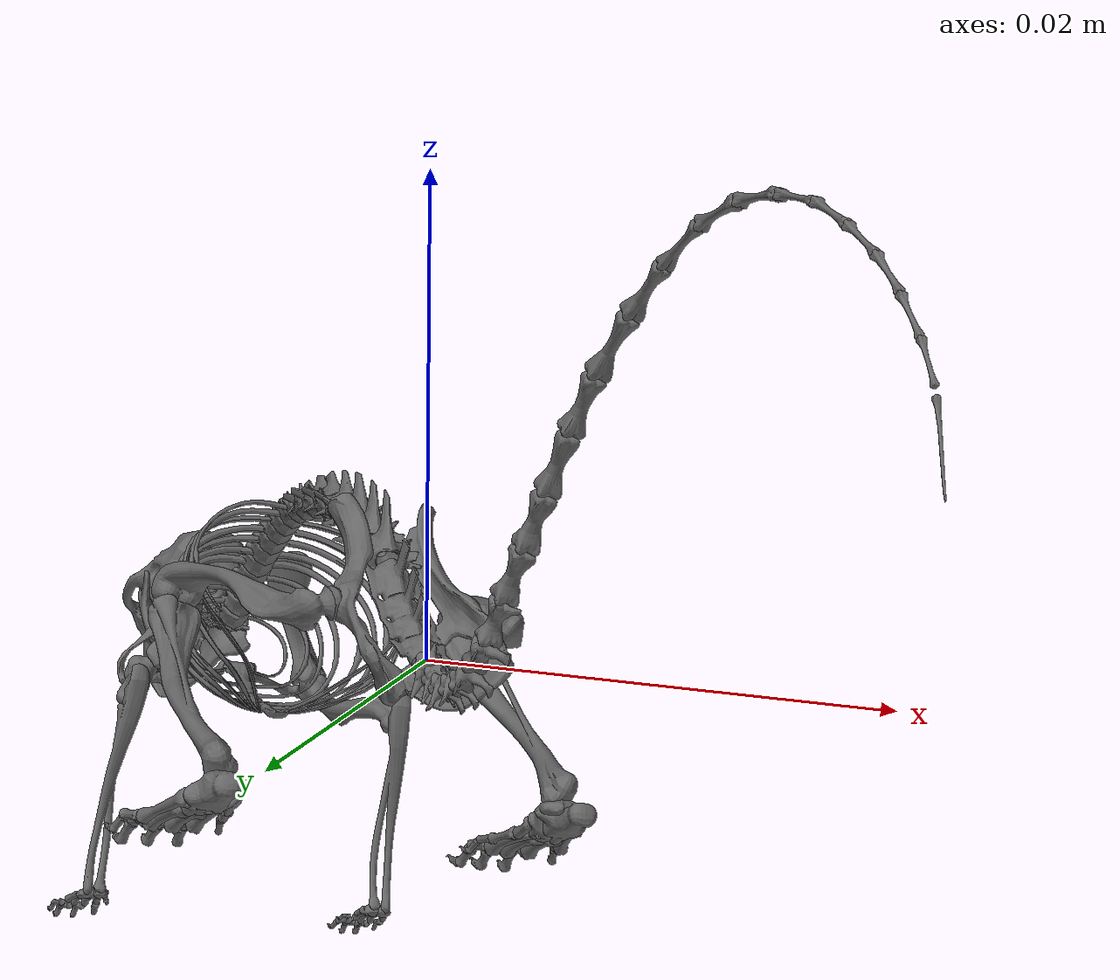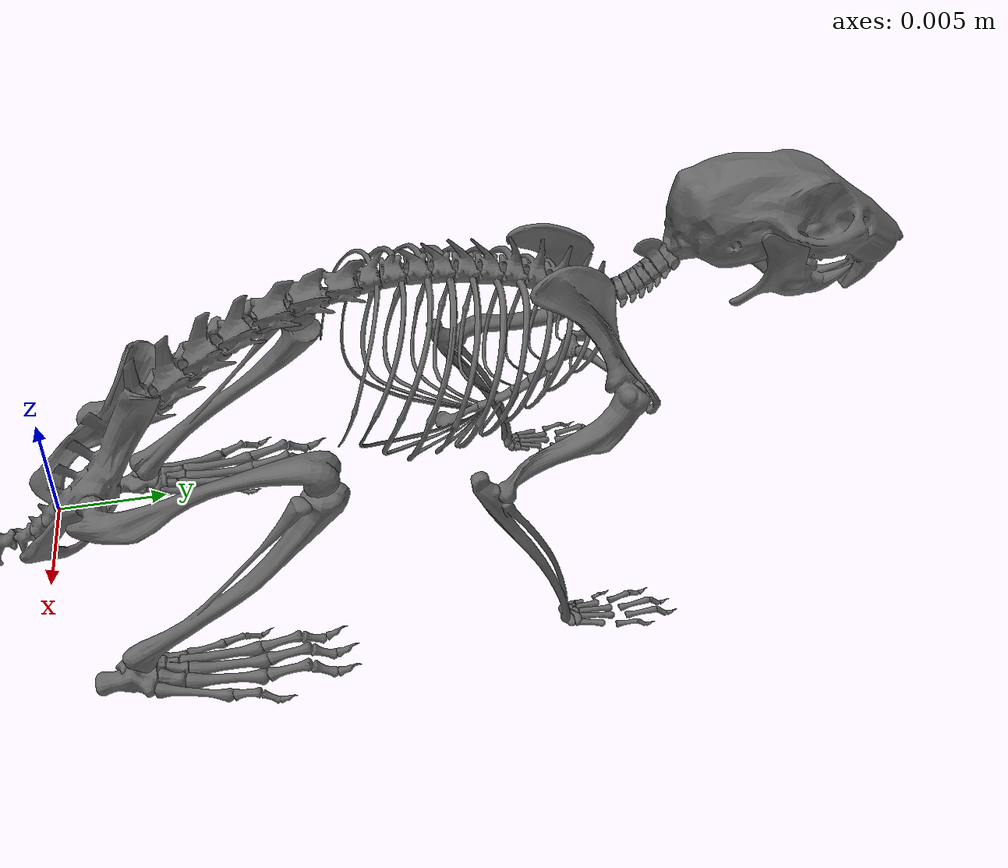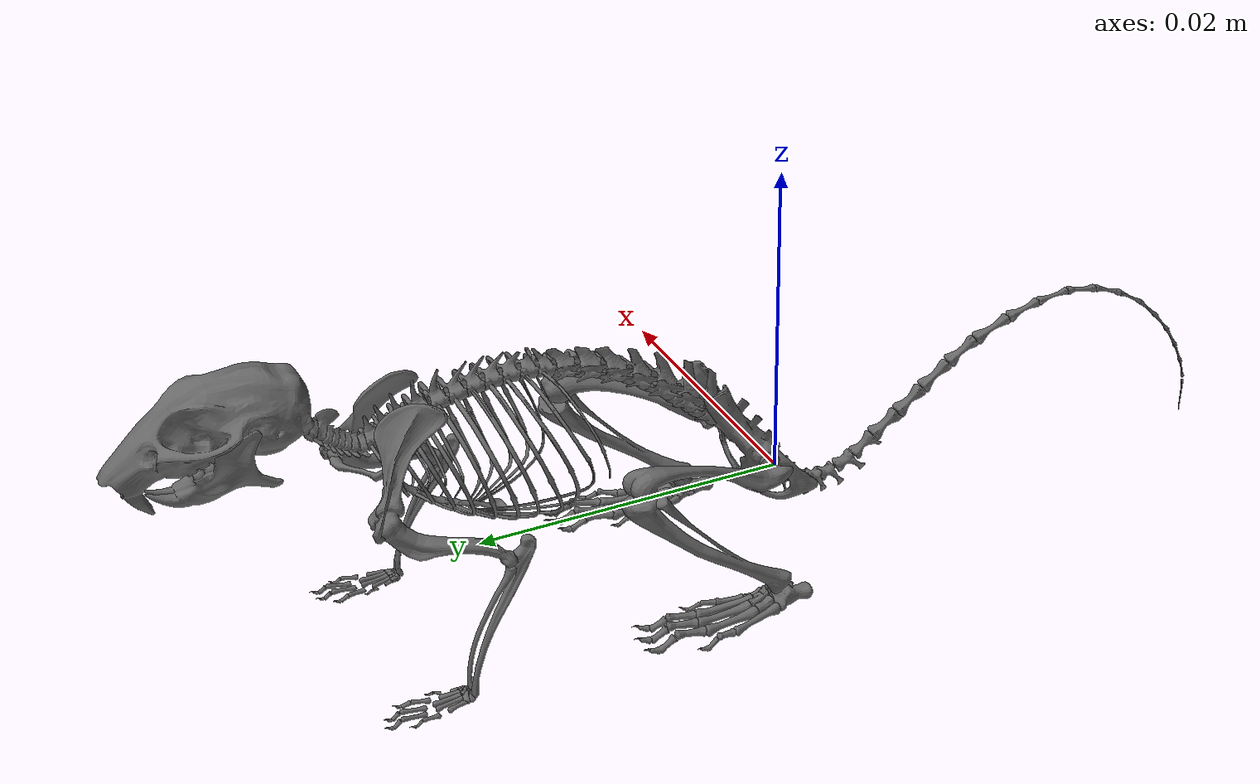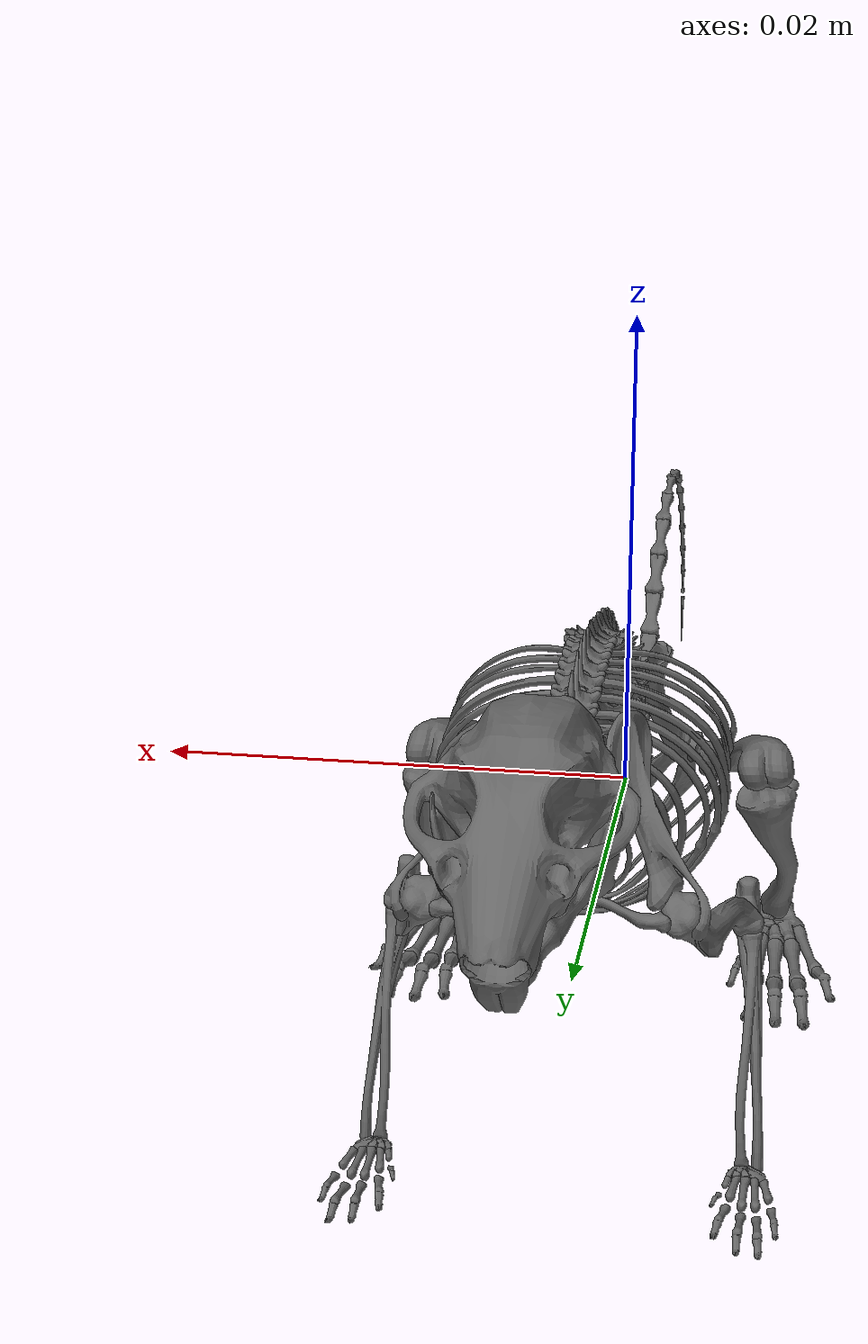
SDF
<?xml version="1.0" ?>
<sdf version="1.5">
	<model name="cheesy_reborn_model">
		<link name="Pelvis">
			<pose>0.0 0.0 0.0 0.8473373055458069 7.7676975962504e-09 -1.7224037307528306e-08</pose>
			<inertial>
				<mass>1.0</mass>
				<pose>-1.5870670366620256e-13 -6.103516034268707e-08 1.2207024792585384e-07 -2.980232594040899e-08 1.9095836023552692e-14 2.220446049250313e-15</pose>
				<inertia>
					<ixx>1.0</ixx>
					<ixy>0.0</ixy>
					<ixz>0.0</ixz>
					<iyy>1.0</iyy>
					<iyz>0.0</iyz>
					<izz>1.0</izz>
				</inertia>
			</inertial>
			<collision name="COL_Pelvis">
				<pose>3.389984285250125e-08 0.003441891889906401 4.333492768182623e-06 -0.8473374247550964 7.767711807105115e-09 1.7224049742026182e-08</pose>
				<geometry>
					<mesh>
						<uri>model://cheesy_reborn_model/meshes/collisions/COL_Pelvis.dae</uri>
						<scale>0.0009999991729855995 0.0009999991729855995 0.0009999991729855995</scale>
					</mesh>
				</geometry>
			</collision>
			<visual name="VIS_Pelvis">
				<pose>3.389984285250125e-08 0.003441891889906401 4.333492768182623e-06 -0.8473374247550964 7.767702037142499e-09 1.7224044412955664e-08</pose>
				<geometry>
					<mesh>
						<uri>model://cheesy_reborn_model/meshes/visual/VIS_Pelvis.dae</uri>
						<scale>0.0009999991729855995 0.0009999991729855995 0.0009999992325901985</scale>
					</mesh>
				</geometry>
			</visual>
		</link>
		<link name="Spine1">
			<pose>1.09556053233e-10 0.00421062883055 0.00476743497471 0.7077112793922425 7.767672755955546e-09 -1.7223961451118872e-08</pose>
			<inertial>
				<mass>1.0</mass>
				<pose>-1.56887715658567e-13 -2.441404958517077e-07 1.2207023337394978e-07 -2.980232594040899e-08 -4.440892098500626e-16 6.661338147750939e-15</pose>
				<inertia>
					<ixx>1.0</ixx>
					<ixy>0.0</ixy>
					<ixz>0.0</ixz>
					<iyy>1.0</iyy>
					<iyz>0.0</iyz>
					<izz>1.0</izz>
				</inertia>
			</inertial>
			<collision name="COL_Spine1">
				<pose>5.118691370596712e-10 0.0011226798025063545 0.00024707012289582053 -0.7101963758468628 2.4366343609472096e-08 6.570996902155457e-08</pose>
				<geometry>
					<mesh>
						<uri>model://cheesy_reborn_model/meshes/collisions/COL_Spine1.dae</uri>
						<scale>0.0009999991729855995 0.0009999991729855995 0.0009999992325901985</scale>
					</mesh>
				</geometry>
			</collision>
			<visual name="VIS_Spine1">
				<pose>5.118691370596712e-10 0.0011226798025063545 0.00024707012289582053 -0.7101963758468628 2.436635782032681e-08 6.570996902155457e-08</pose>
				<geometry>
					<mesh>
						<uri>model://cheesy_reborn_model/meshes/visual/VIS_Spine1.dae</uri>
						<scale>0.0009999991729855995 0.0009999991729855995 0.0009999992325901985</scale>
					</mesh>
				</geometry>
			</visual>
		</link>
		<link name="Spine2">
			<pose>1.45124890031e-10 0.00570075727739 0.006042324602 0.690257439389825 7.767516879846593e-09 -1.7223544267715857e-08</pose>
			<inertial>
				<mass>1.0</mass>
				<pose>-1.887200057921893e-13 -5.5251760731930117e-14 1.2207023337394978e-07 -1.1102231569740545e-16 -2.220446049250313e-15 8.43769498715119e-15</pose>
				<inertia>
					<ixx>1.0</ixx>
					<ixy>0.0</ixy>
					<ixz>0.0</ixz>
					<iyy>1.0</iyy>
					<iyz>0.0</iyz>
					<izz>1.0</izz>
				</inertia>
			</inertial>
			<collision name="COL_Spine2">
				<pose>-1.4500790498069916e-09 0.0010967398810066697 0.00021643049797148706 -0.696855902671814 7.484364346055372e-07 2.0604020392056555e-06</pose>
				<geometry>
					<mesh>
						<uri>model://cheesy_reborn_model/meshes/collisions/COL_Spine2.dae</uri>
						<scale>0.0009999991729855995 0.0009999991133810004 0.0009999992325901985</scale>
					</mesh>
				</geometry>
			</collision>
			<visual name="VIS_Spine2">
				<pose>-1.4500790498069916e-09 0.0010967398810066697 0.00021643049797148706 -0.696855902671814 7.484363777621184e-07 2.06040181183198e-06</pose>
				<geometry>
					<mesh>
						<uri>model://cheesy_reborn_model/meshes/visual/VIS_Spine2.dae</uri>
						<scale>0.0009999991729855995 0.0009999991133810004 0.0009999992325901985</scale>
					</mesh>
				</geometry>
			</visual>
		</link>
		<link name="Spine3">
			<pose>1.809793508e-10 0.00721758869374 0.00729487758092 0.6378971952944995 7.76697701039417e-09 -1.7221902905395366e-08</pose>
			<inertial>
				<mass>1.0</mass>
				<pose>-3.4378873344312073e-13 6.103505484138263e-08 1.8310534278497264e-07 -8.940696716308594e-08 7.105427357601002e-15 7.993605777301127e-15</pose>
				<inertia>
					<ixx>1.0</ixx>
					<ixy>0.0</ixy>
					<ixz>0.0</ixz>
					<iyy>1.0</iyy>
					<iyz>0.0</iyz>
					<izz>1.0</izz>
				</inertia>
			</inertial>
			<collision name="COL_Spine3">
				<pose>9.156616464552696e-09 0.001098723522062528 0.00023168927532424277 -0.65263432264328 -4.132752110308502e-06 -1.2212071851536166e-05</pose>
				<geometry>
					<mesh>
						<uri>model://cheesy_reborn_model/meshes/collisions/COL_Spine3.dae</uri>
						<scale>0.0009999997094269908 0.0009999997094269908 0.0009999992325901985</scale>
					</mesh>
				</geometry>
			</collision>
			<visual name="VIS_Spine3">
				<pose>9.156616464552696e-09 0.001098723522062528 0.00023168927532424277 -0.65263432264328 -4.132751655561151e-06 -1.221207367052557e-05</pose>
				<geometry>
					<mesh>
						<uri>model://cheesy_reborn_model/meshes/visual/VIS_Spine3.dae</uri>
						<scale>0.0009999997094269908 0.0009999997094269908 0.0009999993517993966</scale>
					</mesh>
				</geometry>
			</visual>
		</link>
		<link name="Spine4">
			<pose>2.16659686995e-10 0.00877029858146 0.00844587134898 0.5331792254000903 7.767120427834478e-09 -1.7222176917074486e-08</pose>
			<inertial>
				<mass>1.0</mass>
				<pose>-6.320983326533569e-14 -2.1362294114619625e-07 1.2207021882204572e-07 -1.1920927533992653e-07 -2.7533531010703882e-14 -1.4210854715202004e-14</pose>
				<inertia>
					<ixx>1.0</ixx>
					<ixy>0.0</ixy>
					<ixz>0.0</ixz>
					<iyy>1.0</iyy>
					<iyz>0.0</iyz>
					<izz>1.0</izz>
				</inertia>
			</inertial>
			<collision name="COL_Spine4">
				<pose>1.961402217616171e-08 0.0009717094593781894 0.0001487425616346627 -0.5467171669006348 1.5431164968049416e-07 5.50374011254462e-07</pose>
				<geometry>
					<mesh>
						<uri>model://cheesy_reborn_model/meshes/collisions/COL_Spine4.dae</uri>
						<scale>0.0009999997094269908 0.0009999995902177927 0.0009999992325901985</scale>
					</mesh>
				</geometry>
			</collision>
			<visual name="VIS_Spine4">
				<pose>1.961402217616171e-08 0.0009717094593781894 0.0001487425616346627 -0.5467172265052795 1.543118770541696e-07 5.50374409158394e-07</pose>
				<geometry>
					<mesh>
						<uri>model://cheesy_reborn_model/meshes/visual/VIS_Spine4.dae</uri>
						<scale>0.0009999997094269908 0.0009999995902177927 0.0009999994710085947</scale>
					</mesh>
				</geometry>
			</visual>
		</link>
		<link name="Spine5">
			<pose>2.49200278228e-10 0.010262554844 0.00932659449874 0.39355221576988714 7.76731158084411e-09 -1.7223052115382555e-08</pose>
			<inertial>
				<mass>1.0</mass>
				<pose>-3.5970487850993187e-13 -3.662107146737534e-07 2.4414043764409143e-07 0.0 -1.6653345369377348e-16 -2.4424906541753444e-15</pose>
				<inertia>
					<ixx>1.0</ixx>
					<ixy>0.0</ixy>
					<ixz>0.0</ixz>
					<iyy>1.0</iyy>
					<iyz>0.0</iyz>
					<izz>1.0</izz>
				</inertia>
			</inertial>
			<collision name="COL_Spine5">
				<pose>4.2788255719887307e-07 0.0010359794295879965 0.00018096909940368278 -0.3995368778705597 -2.1953871964797145e-07 -1.0843075415323256e-06</pose>
				<geometry>
					<mesh>
						<uri>model://cheesy_reborn_model/meshes/collisions/COL_Spine5.dae</uri>
						<scale>0.001000000067054585 0.000999999947845387 0.0009999995902177927</scale>
					</mesh>
				</geometry>
			</collision>
			<visual name="VIS_Spine5">
				<pose>4.2788255719887307e-07 0.0010359794295879965 0.00018096909940368278 -0.3995368778705597 -2.1953874806968088e-07 -1.0843075415323256e-06</pose>
				<geometry>
					<mesh>
						<uri>model://cheesy_reborn_model/meshes/visual/VIS_Spine5.dae</uri>
						<scale>0.001000000067054585 0.000999999947845387 0.0009999995902177927</scale>
					</mesh>
				</geometry>
			</visual>
		</link>
		<link name="Spine6">
			<pose>2.82419699225e-10 0.0118871238387 0.0100011373547 0.2888324428349735 7.76759200762066e-09 -1.7225063915183194e-08</pose>
			<inertial>
				<mass>1.0</mass>
				<pose>-2.5283933306134276e-13 -6.10351676186391e-08 2.1362286838667594e-07 2.980232594040899e-08 7.327471962526033e-15 2.6645352591003757e-15</pose>
				<inertia>
					<ixx>1.0</ixx>
					<ixy>0.0</ixy>
					<ixz>0.0</ixz>
					<iyy>1.0</iyy>
					<iyz>0.0</iyz>
					<izz>1.0</izz>
				</inertia>
			</inertial>
			<collision name="COL_Spine6">
				<pose>2.07680336429059e-08 0.0009300835147598718 0.00018466172352304966 -0.30026769638061523 -4.366962969015731e-08 -2.886793879497418e-07</pose>
				<geometry>
					<mesh>
						<uri>model://cheesy_reborn_model/meshes/collisions/COL_Spine6.dae</uri>
						<scale>0.0010000003054729811 0.001000000067054585 0.0009999994710085947</scale>
					</mesh>
				</geometry>
			</collision>
			<visual name="VIS_Spine6">
				<pose>2.07680336429059e-08 0.0009300835147598718 0.00018466172352304966 -0.30026766657829285 -4.366961903201627e-08 -2.886793879497418e-07</pose>
				<geometry>
					<mesh>
						<uri>model://cheesy_reborn_model/meshes/visual/VIS_Spine6.dae</uri>
						<scale>0.0010000003054729811 0.001000000186263783 0.0009999994710085947</scale>
					</mesh>
				</geometry>
			</visual>
		</link>
		<link name="Spine7">
			<pose>3.13347756572e-10 0.0134704851869 0.0104716205357 0.2364719938486816 7.767265157813085e-09 -1.722260906021416e-08</pose>
			<inertial>
				<mass>1.0</mass>
				<pose>-2.291924889620805e-13 -1.3732905438241768e-07 1.5258775897565309e-07 7.450581307466564e-08 1.4654943925052066e-14 3.941291737419306e-14</pose>
				<inertia>
					<ixx>1.0</ixx>
					<ixy>0.0</ixy>
					<ixz>0.0</ixz>
					<iyy>1.0</iyy>
					<iyz>0.0</iyz>
					<izz>1.0</izz>
				</inertia>
			</inertial>
			<collision name="COL_Spine7">
				<pose>2.0909736446676725e-08 0.0008433068479547501 0.00013705433818245183 -0.24715740978717804 1.0315774012781276e-08 8.305536169928018e-08</pose>
				<geometry>
					<mesh>
						<uri>model://cheesy_reborn_model/meshes/collisions/COL_Spine7.dae</uri>
						<scale>0.001000000186263783 0.001000000186263783 0.0009999995902177927</scale>
					</mesh>
				</geometry>
			</collision>
			<visual name="VIS_Spine7">
				<pose>2.0909736446676725e-08 0.0008433068479547501 0.00013705433818245183 -0.24715763330459595 1.0315828191664878e-08 8.305494958449344e-08</pose>
				<geometry>
					<mesh>
						<uri>model://cheesy_reborn_model/meshes/visual/VIS_Spine7.dae</uri>
						<scale>0.001000000186263783 0.001000000067054585 0.0009999995902177927</scale>
					</mesh>
				</geometry>
			</visual>
		</link>
		<link name="Spine8">
			<pose>3.39991441875e-10 0.0148658535228 0.0108078765372 0.14920565299689784 7.767249470560405e-09 -1.7221999926784755e-08</pose>
			<inertial>
				<mass>1.0</mass>
				<pose>-1.4233581159748252e-13 -1.4495844305879553e-07 9.155264956463023e-08 -1.0430814256778831e-07 5.329070518200751e-15 1.4876988529977098e-14</pose>
				<inertia>
					<ixx>1.0</ixx>
					<ixy>0.0</ixy>
					<ixz>0.0</ixz>
					<iyy>1.0</iyy>
					<iyz>0.0</iyz>
					<izz>1.0</izz>
				</inertia>
			</inertial>
			<collision name="COL_Spine8">
				<pose>7.72674033247035e-07 7.83538217064006e-05 -0.0007225031076529831 -0.15411463379859924 4.3589313492020665e-08 5.645588316838257e-07</pose>
				<geometry>
					<mesh>
						<uri>model://cheesy_reborn_model/meshes/collisions/COL_Spine8.dae</uri>
						<scale>0.0010000007823097734 0.0010000007823097734 0.0009999997094269908</scale>
					</mesh>
				</geometry>
			</collision>
			<visual name="VIS_Spine8">
				<pose>7.72674033247035e-07 7.83538217064006e-05 -0.0007225031076529831 -0.1541147530078888 4.35892069106103e-08 5.64558717996988e-07</pose>
				<geometry>
					<mesh>
						<uri>model://cheesy_reborn_model/meshes/visual/VIS_Spine8.dae</uri>
						<scale>0.0010000007823097734 0.0010000006631005753 0.0009999997094269908</scale>
					</mesh>
				</geometry>
			</visual>
		</link>
		<link name="Spine9">
			<pose>3.5919094462e-10 0.0159098951802 0.0109648191043 0.02703078649938119 7.767222321796435e-09 -1.7218515227623026e-08</pose>
			<inertial>
				<mass>1.0</mass>
				<pose>-8.685667736459796e-14 -1.9645681662434607e-07 1.6784652177650474e-07 3.725290742551124e-09 -6.106226635438361e-16 7.854827899222983e-15</pose>
				<inertia>
					<ixx>1.0</ixx>
					<ixy>0.0</ixy>
					<ixz>0.0</ixz>
					<iyy>1.0</iyy>
					<iyz>0.0</iyz>
					<izz>1.0</izz>
				</inertia>
			</inertial>
			<collision name="COL_Spine9">
				<pose>-2.1397829864336793e-07 0.00015945040864195903 -0.0028332383347766665 -0.03449360653758049 3.777957058304082e-09 2.1905796643295616e-07</pose>
				<geometry>
					<mesh>
						<uri>model://cheesy_reborn_model/meshes/collisions/COL_Spine9.dae</uri>
						<scale>0.0010000007823097734 0.0010000006631005753 0.0009999995902177927</scale>
					</mesh>
				</geometry>
			</collision>
			<visual name="VIS_Spine9">
				<pose>-2.1397829864336793e-07 0.00015945040864195903 -0.0028332383347766665 -0.034493595361709595 3.777877122246309e-09 2.1905785274611844e-07</pose>
				<geometry>
					<mesh>
						<uri>model://cheesy_reborn_model/meshes/visual/VIS_Spine9.dae</uri>
						<scale>0.0010000007823097734 0.0010000006631005753 0.0009999997094269908</scale>
					</mesh>
				</geometry>
			</visual>
		</link>
		<link name="Spine10">
			<pose>3.78152909727e-10 0.0169978789616 0.0109942364891 -0.007874550297856206 7.7673226683789e-09 -1.7204653658631227e-08</pose>
			<inertial>
				<mass>1.0</mass>
				<pose>-2.6602699611670056e-13 -4.100796995629261e-07 8.296958002775311e-08 -1.3969836842875338e-08 2.095545958979983e-15 3.164135620181696e-15</pose>
				<inertia>
					<ixx>1.0</ixx>
					<ixy>0.0</ixy>
					<ixz>0.0</ixz>
					<iyy>1.0</iyy>
					<iyz>0.0</iyz>
					<izz>1.0</izz>
				</inertia>
			</inertial>
			<collision name="COL_Spine10">
				<pose>-3.265870557092685e-06 5.6233362912827545e-05 -0.0028833157347012417 -0.004884591791778803 7.063771789717066e-09 2.8924587240908295e-06</pose>
				<geometry>
					<mesh>
						<uri>model://cheesy_reborn_model/meshes/collisions/COL_Spine10.dae</uri>
						<scale>0.0010000011399373676 0.0010000009015189715 0.0009999997094269908</scale>
					</mesh>
				</geometry>
			</collision>
			<visual name="VIS_Spine10">
				<pose>-3.265870557092685e-06 5.6233362912827545e-05 -0.0028833157347012417 -0.0048844777047634125 7.063519547045871e-09 2.8924591788381804e-06</pose>
				<geometry>
					<mesh>
						<uri>model://cheesy_reborn_model/meshes/visual/VIS_Spine10.dae</uri>
						<scale>0.0010000011399373676 0.0010000010207281695 0.0009999997094269908</scale>
					</mesh>
				</geometry>
			</visual>
		</link>
		<link name="Spine11">
			<pose>3.96522635234e-10 0.0180694056578 0.0109857986281 -0.11259591020643699 7.767021948308405e-09 -1.7217227329311455e-08</pose>
			<inertial>
				<mass>1.0</mass>
				<pose>-2.464728750346183e-13 -3.3569315996824197e-07 6.103508030721474e-08 7.450580596923828e-09 5.773159728050814e-15 -3.6637359812630166e-15</pose>
				<inertia>
					<ixx>1.0</ixx>
					<ixy>0.0</ixy>
					<ixz>0.0</ixz>
					<iyy>1.0</iyy>
					<iyz>0.0</iyz>
					<izz>1.0</izz>
				</inertia>
			</inertial>
			<collision name="COL_Spine11">
				<pose>-1.8756615039461615e-06 0.0002793348076082225 -0.002735746191575572 0.10191534459590912 -1.4549625859672233e-07 2.852760189853143e-06</pose>
				<geometry>
					<mesh>
						<uri>model://cheesy_reborn_model/meshes/collisions/COL_Spine11.dae</uri>
						<scale>0.0010000016167741599 0.0010000014975649618 0.0009999998286361889</scale>
					</mesh>
				</geometry>
			</collision>
			<visual name="VIS_Spine11">
				<pose>-1.8756615039461615e-06 0.0002793348076082225 -0.002735746191575572 0.1019153818488121 -1.454965143921072e-07 2.852760189853143e-06</pose>
				<geometry>
					<mesh>
						<uri>model://cheesy_reborn_model/meshes/visual/VIS_Spine11.dae</uri>
						<scale>0.0010000016167741599 0.0010000014975649618 0.0009999997094269908</scale>
					</mesh>
				</geometry>
			</visual>
		</link>
		<link name="Spine12">
			<pose>4.14162069292e-10 0.0191489952899 0.0108637258972 -0.16495280526578415 7.767491445078192e-09 -1.7211122708621077e-08</pose>
			<inertial>
				<mass>1.0</mass>
				<pose>-4.888530270520566e-13 -3.2043438261548625e-07 3.05175237827153e-08 -2.980232594040899e-08 -2.886579864025407e-15 -2.5757174171303632e-14</pose>
				<inertia>
					<ixx>1.0</ixx>
					<ixy>0.0</ixy>
					<ixz>0.0</ixz>
					<iyy>1.0</iyy>
					<iyz>0.0</iyz>
					<izz>1.0</izz>
				</inertia>
			</inertial>
			<collision name="COL_Spine12">
				<pose>1.0658095095048567e-06 0.0004471279527678007 -0.0025220927910822866 0.14826536178588867 -2.452456158152927e-07 3.302134018667857e-06</pose>
				<geometry>
					<mesh>
						<uri>model://cheesy_reborn_model/meshes/collisions/COL_Spine12.dae</uri>
						<scale>0.001000001735983358 0.0010000016167741599 0.0009999997094269908</scale>
					</mesh>
				</geometry>
			</collision>
			<visual name="VIS_Spine12">
				<pose>1.0658095095048567e-06 0.0004471279527678007 -0.0025220927910822866 0.14826525747776031 -2.4524567265871156e-07 3.302134018667857e-06</pose>
				<geometry>
					<mesh>
						<uri>model://cheesy_reborn_model/meshes/visual/VIS_Spine12.dae</uri>
						<scale>0.001000001735983358 0.0010000016167741599 0.0009999998286361889</scale>
					</mesh>
				</geometry>
			</visual>
		</link>
		<link name="Spine13">
			<pose>4.31167620905e-10 0.0202173123111 0.0106858878778 -0.1998588163405656 7.766585581087574e-09 -1.722052786265186e-08</pose>
			<inertial>
				<mass>1.0</mass>
				<pose>-7.048578529587793e-14 -2.441404958517077e-07 3.051752196372729e-08 -2.980232594040899e-08 1.9984014443252818e-15 8.770761894538737e-15</pose>
				<inertia>
					<ixx>1.0</ixx>
					<ixy>0.0</ixy>
					<ixz>0.0</ixz>
					<iyy>1.0</iyy>
					<iyz>0.0</iyz>
					<izz>1.0</izz>
				</inertia>
			</inertial>
			<collision name="COL_Spine13">
				<pose>-1.99286689027345e-08 0.0005021358451244851 -0.00251901051805703 0.18742723762989044 -3.6014353099744767e-07 3.831754838756751e-06</pose>
				<geometry>
					<mesh>
						<uri>model://cheesy_reborn_model/meshes/collisions/COL_Spine13.dae</uri>
						<scale>0.0010000013783557637 0.0010000011399373676 0.000999999947845387</scale>
					</mesh>
				</geometry>
			</collision>
			<visual name="VIS_Spine13">
				<pose>-1.99286689027345e-08 0.0005021358451244851 -0.00251901051805703 0.18742729723453522 -3.6014353099744767e-07 3.831754838756751e-06</pose>
				<geometry>
					<mesh>
						<uri>model://cheesy_reborn_model/meshes/visual/VIS_Spine13.dae</uri>
						<scale>0.0010000013783557637 0.0010000012591465657 0.0009999998286361889</scale>
					</mesh>
				</geometry>
			</visual>
		</link>
		<link name="Spine14">
			<pose>4.47866523184e-10 0.0212845190825 0.0104697112143 -0.252220595255494 7.76716417682485e-09 -1.721505993602165e-08</pose>
			<inertial>
				<mass>1.0</mass>
				<pose>-2.773956711644228e-13 -2.441404958517077e-07 -3.5754483025086464e-14 -1.4901162970204496e-08 -1.3322676295501878e-15 -2.4424906541753444e-15</pose>
				<inertia>
					<ixx>1.0</ixx>
					<ixy>0.0</ixy>
					<ixz>0.0</ixz>
					<iyy>1.0</iyy>
					<iyz>0.0</iyz>
					<izz>1.0</izz>
				</inertia>
			</inertial>
			<collision name="COL_Spine14">
				<pose>1.55847385485336e-07 0.0006267237622097355 -0.0020645736109372592 0.23947551846504211 -5.079299967292172e-07 4.221716153551824e-06</pose>
				<geometry>
					<mesh>
						<uri>model://cheesy_reborn_model/meshes/collisions/COL_Spine14.dae</uri>
						<scale>0.0010000016167741599 0.0010000016167741599 0.0009999998286361889</scale>
					</mesh>
				</geometry>
			</collision>
			<visual name="VIS_Spine14">
				<pose>1.55847385485336e-07 0.0006267237622097355 -0.0020645736109372592 0.23947548866271973 -5.079297693555418e-07 4.221716153551824e-06</pose>
				<geometry>
					<mesh>
						<uri>model://cheesy_reborn_model/meshes/visual/VIS_Spine14.dae</uri>
						<scale>0.0010000016167741599 0.0010000014975649618 0.0009999998286361889</scale>
					</mesh>
				</geometry>
			</visual>
		</link>
		<link name="Spine15">
			<pose>4.63674171398e-10 0.0223235807612 0.010201936038 -0.32203371264040465 7.76421326957913e-09 -1.7233431064830348e-08</pose>
			<inertial>
				<mass>1.0</mass>
				<pose>-3.983583736721875e-13 -2.4414046674789956e-07 -3.05175947232476e-08 2.9802318834981634e-08 6.217248937900877e-15 -5.329070518200751e-15</pose>
				<inertia>
					<ixx>1.0</ixx>
					<ixy>0.0</ixy>
					<ixz>0.0</ixz>
					<iyy>1.0</iyy>
					<iyz>0.0</iyz>
					<izz>1.0</izz>
				</inertia>
			</inertial>
			<collision name="COL_Spine15">
				<pose>2.794106733197612e-07 0.000750182529770882 -0.001763334828439156 0.30057084560394287 -6.959948564144725e-07 4.596226062858477e-06</pose>
				<geometry>
					<mesh>
						<uri>model://cheesy_reborn_model/meshes/collisions/COL_Spine15.dae</uri>
						<scale>0.0010000013783557637 0.0010000012591465657 0.000999999947845387</scale>
					</mesh>
				</geometry>
			</collision>
			<visual name="VIS_Spine15">
				<pose>2.794106733197612e-07 0.000750182529770882 -0.001763334828439156 0.3005707561969757 -6.95994629040797e-07 4.596226062858477e-06</pose>
				<geometry>
					<mesh>
						<uri>model://cheesy_reborn_model/meshes/visual/VIS_Spine15.dae</uri>
						<scale>0.0010000013783557637 0.0010000012591465657 0.000999999947845387</scale>
					</mesh>
				</geometry>
			</visual>
		</link>
		<link name="Spine16">
			<pose>4.78805070802e-10 0.0233569064718 0.00985716950122 -0.40929828025400633 7.764573507834014e-09 -1.7229865002487775e-08</pose>
			<inertial>
				<mass>1.0</mass>
				<pose>-1.8644627078264484e-13 -3.967282402754567e-07 -3.814698703760147e-08 5.960463766996327e-08 -5.329070518200751e-15 1.865174681370263e-14</pose>
				<inertia>
					<ixx>1.0</ixx>
					<ixy>0.0</ixy>
					<ixz>0.0</ixz>
					<iyy>1.0</iyy>
					<iyz>0.0</iyz>
					<izz>1.0</izz>
				</inertia>
			</inertial>
			<collision name="COL_Spine16">
				<pose>-3.2209748335086744e-08 0.0007898553508880468 -0.0013495854511305083 0.3793679177761078 -1.0971369874823722e-06 5.714484814234311e-06</pose>
				<geometry>
					<mesh>
						<uri>model://cheesy_reborn_model/meshes/collisions/COL_Spine16.dae</uri>
						<scale>0.0010000012591465657 0.0010000012591465657 0.001000000067054585</scale>
					</mesh>
				</geometry>
			</collision>
			<visual name="VIS_Spine16">
				<pose>-3.2209748335086744e-08 0.0007898553508880468 -0.0013495854511305083 0.3793679177761078 -1.0971369874823722e-06 5.71448435948696e-06</pose>
				<geometry>
					<mesh>
						<uri>model://cheesy_reborn_model/meshes/visual/VIS_Spine16.dae</uri>
						<scale>0.0010000012591465657 0.0010000012591465657 0.001000000067054585</scale>
					</mesh>
				</geometry>
			</visual>
		</link>
		<link name="Spine17">
			<pose>4.92069076986e-10 0.0243137959627 0.00944207457689 -0.4267537612468003 7.764145460301119e-09 -1.723163957245124e-08</pose>
			<inertial>
				<mass>1.0</mass>
				<pose>1.8189880076355594e-14 -2.74658021453411e-07 -4.297359168039009e-14 -2.9802318834981634e-08 -8.881784197001252e-16 1.2656542480726785e-14</pose>
				<inertia>
					<ixx>1.0</ixx>
					<ixy>0.0</ixy>
					<ixz>0.0</ixz>
					<iyy>1.0</iyy>
					<iyz>0.0</iyz>
					<izz>1.0</izz>
				</inertia>
			</inertial>
			<collision name="COL_Spine17">
				<pose>-3.289572873050228e-07 0.0006984552745450401 -0.0009758903643728445 0.3906850814819336 -8.937283269006002e-07 4.516838089330122e-06</pose>
				<geometry>
					<mesh>
						<uri>model://cheesy_reborn_model/meshes/collisions/COL_Spine17.dae</uri>
						<scale>0.0010000012591465657 0.0010000011399373676 0.001000000067054585</scale>
					</mesh>
				</geometry>
			</collision>
			<visual name="VIS_Spine17">
				<pose>-3.289572873050228e-07 0.0006984552745450401 -0.0009758903643728445 0.3906850516796112 -8.937282132137625e-07 4.516838089330122e-06</pose>
				<geometry>
					<mesh>
						<uri>model://cheesy_reborn_model/meshes/visual/VIS_Spine17.dae</uri>
						<scale>0.0010000012591465657 0.0010000012591465657 0.001000000186263783</scale>
					</mesh>
				</geometry>
			</visual>
		</link>
		<link name="Ribcage">
			<pose>5.04906939753e-10 0.0252507769117 0.00901603033451 -0.1300475616008042 7.764953247833116e-09 -1.7229524001498702e-08</pose>
			<inertial>
				<mass>1.0</mass>
				<pose>-1.3778834157839362e-13 -1.9836414924153647e-07 3.051752560170331e-08 2.980232594040899e-08 3.3306690738754696e-15 4.440892098500626e-16</pose>
				<inertia>
					<ixx>1.0</ixx>
					<ixy>0.0</ixy>
					<ixz>0.0</ixz>
					<iyy>1.0</iyy>
					<iyz>0.0</iyz>
					<izz>1.0</izz>
				</inertia>
			</inertial>
			<collision name="COL_Ribcage">
				<pose>-1.2555699327817014e-08 0.0004669109576056485 -0.0005972895806962697 0.09659107774496078 -8.801306705663592e-08 1.8209437939731288e-06</pose>
				<geometry>
					<mesh>
						<uri>model://cheesy_reborn_model/meshes/collisions/COL_Ribcage.dae</uri>
						<scale>0.001000000067054585 0.0010000005438913773 0.001000000067054585</scale>
					</mesh>
				</geometry>
			</collision>
			<visual name="VIS_Ribcage">
				<pose>-1.2555699327817014e-08 0.0004669109576056485 -0.0005972895806962697 0.0965910255908966 -8.801288231552462e-08 1.8209437939731288e-06</pose>
				<geometry>
					<mesh>
						<uri>model://cheesy_reborn_model/meshes/visual/VIS_Ribcage.dae</uri>
						<scale>0.001000000067054585 0.0010000004246821792 0.001000000067054585</scale>
					</mesh>
				</geometry>
			</visual>
		</link>
		<link name="Neck1">
			<pose>5.2174606152e-10 0.0262893806659 0.00888019606338 0.09684461168944851 7.76621772151432e-09 -1.7252090212279857e-08</pose>
			<inertial>
				<mass>1.0</mass>
				<pose>-3.17868154334314e-13 -1.7547599776430696e-07 7.629386493592248e-08 -1.4901162970204496e-08 -6.661338147750939e-16 -1.970645868709653e-14</pose>
				<inertia>
					<ixx>1.0</ixx>
					<ixy>0.0</ixy>
					<ixz>0.0</ixz>
					<iyy>1.0</iyy>
					<iyz>0.0</iyz>
					<izz>1.0</izz>
				</inertia>
			</inertial>
			<collision name="COL_Neck1">
				<pose>0.00025976587268780604 0.00012683858674478188 -2.8030372134368528e-05 -0.1277122050523758 2.9050625016679987e-07 4.543201612250414e-06</pose>
				<geometry>
					<mesh>
						<uri>model://cheesy_reborn_model/meshes/collisions/COL_Neck1.dae</uri>
						<scale>0.0010000007823097734 0.001000000186263783 0.001000000067054585</scale>
					</mesh>
				</geometry>
			</collision>
			<visual name="VIS_Neck1">
				<pose>0.00025976587268780604 0.00012683858674478188 -2.8030372134368528e-05 -0.1277121603488922 2.90505795419449e-07 4.543202066997765e-06</pose>
				<geometry>
					<mesh>
						<uri>model://cheesy_reborn_model/meshes/visual/VIS_Neck1.dae</uri>
						<scale>0.0010000007823097734 0.0010000003054729811 0.001000000067054585</scale>
					</mesh>
				</geometry>
			</visual>
		</link>
		<link name="Neck2">
			<pose>5.30210760601e-10 0.0267594706013 0.00892586508229 0.2888297718018295 8.013389346143004e-09 -1.894374300675929e-08</pose>
			<inertial>
				<mass>1.0</mass>
				<pose>-2.946760572369606e-13 -3.2043438261548625e-07 2.1362288293858e-07 5.551115784870273e-17 -6.661338147750939e-16 -5.995204332975845e-15</pose>
				<inertia>
					<ixx>1.0</ixx>
					<ixy>0.0</ixy>
					<ixz>0.0</ixz>
					<iyy>1.0</iyy>
					<iyz>0.0</iyz>
					<izz>1.0</izz>
				</inertia>
			</inertial>
			<collision name="COL_Neck2">
				<pose>-2.0977543226434958e-07 0.0002259214574849011 -8.477776697191075e-05 -0.32084113359451294 1.190352031699149e-05 7.35644280212e-05</pose>
				<geometry>
					<mesh>
						<uri>model://cheesy_reborn_model/meshes/collisions/COL_Neck2.dae</uri>
						<scale>0.0010000016167741599 0.0009999997094269908 0.0010000004246821792</scale>
					</mesh>
				</geometry>
			</collision>
			<visual name="VIS_Neck2">
				<pose>-2.097751994338846e-07 0.0002259214574849011 -8.477776697191075e-05 -0.32084113359451294 1.1903523954970296e-05 7.35644280212e-05</pose>
				<geometry>
					<mesh>
						<uri>model://cheesy_reborn_model/meshes/visual/VIS_Neck2.dae</uri>
						<scale>0.0010000016167741599 0.0009999997094269908 0.0010000004246821792</scale>
					</mesh>
				</geometry>
			</visual>
		</link>
		<link name="Neck3">
			<pose>5.39552052088e-10 0.0271975159892 0.00905602504952 0.46336287073791044 7.8865782761503e-09 -1.8079469095585736e-08</pose>
			<inertial>
				<mass>1.0</mass>
				<pose>-3.3924126342403183e-13 -2.441404958517077e-07 1.8310532823306858e-07 -2.980232594040899e-08 4.440892098500626e-16 -1.7763568394002505e-15</pose>
				<inertia>
					<ixx>1.0</ixx>
					<ixy>0.0</ixy>
					<ixz>0.0</ixz>
					<iyy>1.0</iyy>
					<iyz>0.0</iyz>
					<izz>1.0</izz>
				</inertia>
			</inertial>
			<collision name="COL_Neck3">
				<pose>1.3804149013941627e-08 0.000222930737123761 -5.352779095346705e-05 -0.4926894009113312 8.222127689805347e-07 3.2698615086701466e-06</pose>
				<geometry>
					<mesh>
						<uri>model://cheesy_reborn_model/meshes/collisions/COL_Neck3.dae</uri>
						<scale>0.0009999954178958603 0.0010000082924892517 0.001000001855192556</scale>
					</mesh>
				</geometry>
			</collision>
			<visual name="VIS_Neck3">
				<pose>1.3804149013941627e-08 0.000222930737123761 -5.352779095346705e-05 -0.4926894009113312 8.22212655293697e-07 3.2698615086701466e-06</pose>
				<geometry>
					<mesh>
						<uri>model://cheesy_reborn_model/meshes/visual/VIS_Neck3.dae</uri>
						<scale>0.0009999954178958603 0.0010000082924892517 0.001000001855192556</scale>
					</mesh>
				</geometry>
			</visual>
		</link>
		<link name="Neck4">
			<pose>5.48169584727e-10 0.0275888717625 0.00925156259744 0.4982648398727181 7.875022518264872e-09 -1.803468257540244e-08</pose>
			<inertial>
				<mass>1.0</mass>
				<pose>-1.1732472649249358e-13 -3.3569315996824197e-07 2.4414043764409143e-07 2.9802318834981634e-08 -2.55351295663786e-15 -8.881784197001252e-16</pose>
				<inertia>
					<ixx>1.0</ixx>
					<ixy>0.0</ixy>
					<ixz>0.0</ixz>
					<iyy>1.0</iyy>
					<iyz>0.0</iyz>
					<izz>1.0</izz>
				</inertia>
			</inertial>
			<collision name="COL_Neck4">
				<pose>1.2463094648348287e-08 0.00022048933274732008 -3.796383805365622e-05 -0.5225954651832581 1.6391848021157784e-06 6.129807843535673e-06</pose>
				<geometry>
					<mesh>
						<uri>model://cheesy_reborn_model/meshes/collisions/COL_Neck4.dae</uri>
						<scale>0.0009999957159188555 0.0010000085309076479 0.001000001974401754</scale>
					</mesh>
				</geometry>
			</collision>
			<visual name="VIS_Neck4">
				<pose>1.2463094648348287e-08 0.00022048933274732008 -3.796383805365622e-05 -0.5225954651832581 1.6391846884289407e-06 6.129807843535673e-06</pose>
				<geometry>
					<mesh>
						<uri>model://cheesy_reborn_model/meshes/visual/VIS_Neck4.dae</uri>
						<scale>0.0009999957159188555 0.0010000085309076479 0.001000001974401754</scale>
					</mesh>
				</geometry>
			</visual>
		</link>
		<link name="Neck5">
			<pose>5.56557686002e-10 0.0279646982679 0.00945603052665 0.6728007253259423 7.847846598387263e-09 -1.796382607030399e-08</pose>
			<inertial>
				<mass>1.0</mass>
				<pose>-6.366458026724458e-14 -2.441404958517077e-07 2.4414046674789956e-07 -8.940695295223122e-08 -4.884981308350689e-15 4.440892098500626e-15</pose>
				<inertia>
					<ixx>1.0</ixx>
					<ixy>0.0</ixy>
					<ixz>0.0</ixz>
					<iyy>1.0</iyy>
					<iyz>0.0</iyz>
					<izz>1.0</izz>
				</inertia>
			</inertial>
			<collision name="COL_Neck5">
				<pose>7.064370528723083e-09 0.00022088606095849173 -2.178953405973516e-05 -0.68881756067276 3.1116419449972454e-06 8.67463768372545e-06</pose>
				<geometry>
					<mesh>
						<uri>model://cheesy_reborn_model/meshes/collisions/COL_Neck5.dae</uri>
						<scale>0.000999996490778643 0.0010000082924892517 0.0010000020936109522</scale>
					</mesh>
				</geometry>
			</collision>
			<visual name="VIS_Neck5">
				<pose>7.064370528723083e-09 0.00022088606095849173 -2.178953405973516e-05 -0.6888175010681152 3.1116414902498946e-06 8.67463768372545e-06</pose>
				<geometry>
					<mesh>
						<uri>model://cheesy_reborn_model/meshes/visual/VIS_Neck5.dae</uri>
						<scale>0.000999996490778643 0.0010000084116984498 0.0010000020936109522</scale>
					</mesh>
				</geometry>
			</visual>
		</link>
		<link name="Neck6">
			<pose>5.6514673934e-10 0.028319365171 0.00973863970113 0.6553465574979784 7.870397174226248e-09 -1.802880946743083e-08</pose>
			<inertial>
				<mass>1.0</mass>
				<pose>-5.184115821761344e-14 -1.2207027702966196e-07 1.2207023337394978e-07 -1.1102230246251565e-16 1.3322676295501878e-15 2.6645352591003757e-15</pose>
				<inertia>
					<ixx>1.0</ixx>
					<ixy>0.0</ixy>
					<ixz>0.0</ixz>
					<iyy>1.0</iyy>
					<iyz>0.0</iyz>
					<izz>1.0</izz>
				</inertia>
			</inertial>
			<collision name="COL_Neck6">
				<pose>4.64913325883565e-09 0.000189575049830637 -1.6113268884510035e-05 -0.6789202094078064 3.4285601486772066e-06 9.709059668239206e-06</pose>
				<geometry>
					<mesh>
						<uri>model://cheesy_reborn_model/meshes/collisions/COL_Neck6.dae</uri>
						<scale>0.000999996609987841 0.0010000082924892517 0.0010000020936109522</scale>
					</mesh>
				</geometry>
			</collision>
			<visual name="VIS_Neck6">
				<pose>4.64913325883565e-09 0.000189575049830637 -1.6113268884510035e-05 -0.6789201498031616 3.4285601486772066e-06 9.709058758744504e-06</pose>
				<geometry>
					<mesh>
						<uri>model://cheesy_reborn_model/meshes/visual/VIS_Neck6.dae</uri>
						<scale>0.000999996609987841 0.0010000084116984498 0.0010000022128201502</scale>
					</mesh>
				</geometry>
			</visual>
		</link>
		<link name="Neck7">
			<pose>5.73350540833e-10 0.0286600729625 0.0100005339664 0.5680804103612902 7.856820119438443e-09 -1.7983690186810146e-08</pose>
			<inertial>
				<mass>1.0</mass>
				<pose>-3.624333605213852e-13 -1.525878317351734e-07 1.2207023337394978e-07 -5.551115784870273e-17 -1.9984014443252818e-15 -8.881784197001252e-16</pose>
				<inertia>
					<ixx>1.0</ixx>
					<ixy>0.0</ixy>
					<ixz>0.0</ixz>
					<iyy>1.0</iyy>
					<iyz>0.0</iyz>
					<izz>1.0</izz>
				</inertia>
			</inertial>
			<collision name="COL_Neck7">
				<pose>2.307772640738529e-08 0.0002712705437772911 0.00032958959081952344 -0.5998834371566772 3.4648603559617186e-06 1.1203256690350827e-05</pose>
				<geometry>
					<mesh>
						<uri>model://cheesy_reborn_model/meshes/collisions/COL_Neck7.dae</uri>
						<scale>0.0009999972060338314 0.001000008769326044 0.0010000022128201502</scale>
					</mesh>
				</geometry>
			</collision>
			<visual name="VIS_Neck7">
				<pose>2.307772640738529e-08 0.0002712705437772911 0.00032958959081952344 -0.5998835563659668 3.464861038082745e-06 1.1203257599845529e-05</pose>
				<geometry>
					<mesh>
						<uri>model://cheesy_reborn_model/meshes/visual/VIS_Neck7.dae</uri>
						<scale>0.0009999972060338314 0.001000008769326044 0.0010000023320293483</scale>
					</mesh>
				</geometry>
			</visual>
		</link>
		<link name="Neck8">
			<pose>5.84902240337e-10 0.0291623550038 0.0103211228967 0.5506240949034694 7.858742518870404e-09 -1.7989988523901396e-08</pose>
			<inertial>
				<mass>1.0</mass>
				<pose>-2.605700320937939e-13 -1.8310538644068482e-07 2.4414043764409143e-07 -2.980232594040899e-08 -4.6629367034256575e-15 -6.661338147750939e-15</pose>
				<inertia>
					<ixx>1.0</ixx>
					<ixy>0.0</ixy>
					<ixz>0.0</ixz>
					<iyy>1.0</iyy>
					<iyz>0.0</iyz>
					<izz>1.0</izz>
				</inertia>
			</inertial>
			<collision name="COL_Neck8">
				<pose>-1.337631030162969e-09 0.0001957090783264448 0.00011871328780443946 -0.5897371768951416 2.761939413176151e-06 9.093609151022974e-06</pose>
				<geometry>
					<mesh>
						<uri>model://cheesy_reborn_model/meshes/collisions/COL_Neck8.dae</uri>
						<scale>0.0009999977424752227 0.0010000092461628363 0.0010000024512385464</scale>
					</mesh>
				</geometry>
			</collision>
			<visual name="VIS_Neck8">
				<pose>-1.337631030162969e-09 0.0001957090783264448 0.00011871328780443946 -0.5897371768951416 2.761939413176151e-06 9.093610060517676e-06</pose>
				<geometry>
					<mesh>
						<uri>model://cheesy_reborn_model/meshes/visual/VIS_Neck8.dae</uri>
						<scale>0.0009999977424752227 0.0010000092461628363 0.0010000024512385464</scale>
					</mesh>
				</geometry>
			</visual>
		</link>
		<link name="Head">
			<pose>5.93695563041e-10 0.0295477768587 0.0105577570112 -0.007877506315707826 7.862181036465256e-09 -1.8002026062088315e-08</pose>
			<inertial>
				<mass>1.0</mass>
				<pose>-3.042257442770473e-13 -2.8705580715633313e-07 9.822835738050882e-08 1.30385160446167e-08 -2.220446049250313e-16 6.522560269672795e-16</pose>
				<inertia>
					<ixx>1.0</ixx>
					<ixy>0.0</ixy>
					<ixz>0.0</ixz>
					<iyy>1.0</iyy>
					<iyz>0.0</iyz>
					<izz>1.0</izz>
				</inertia>
			</inertial>
			<collision name="COL_Head">
				<pose>-3.1225694012835983e-09 0.00522516183412014 0.0014374636109257821 -0.03844691440463066 9.804204381680393e-08 5.099468125990825e-06</pose>
				<geometry>
					<mesh>
						<uri>model://cheesy_reborn_model/meshes/collisions/COL_Head.dae</uri>
						<scale>0.0010000040009581213 0.0010000013783557637 0.0010000024512385464</scale>
					</mesh>
				</geometry>
			</collision>
			<collision name="COL_Head_1">
				<pose>1.1522617821796451e-08 0.0050839900102364055 -0.0006793789418333418 -0.038446906954050064 9.804204381680393e-08 5.099467216496123e-06</pose>
				<geometry>
					<mesh>
						<uri>model://cheesy_reborn_model/meshes/collisions/COL_Head_1.dae</uri>
						<scale>0.0010000025704477444 0.0010000025704477444 0.0010000025704477444</scale>
					</mesh>
				</geometry>
			</collision>
			<visual name="VIS_Head">
				<pose>-3.1225694012835983e-09 0.00522516183412014 0.0014374636109257821 -0.03844689577817917 9.80419301299662e-08 5.099468125990825e-06</pose>
				<geometry>
					<mesh>
						<uri>model://cheesy_reborn_model/meshes/visual/VIS_Head.dae</uri>
						<scale>0.0010000040009581213 0.0010000014975649618 0.0010000025704477444</scale>
					</mesh>
				</geometry>
			</visual>
			<visual name="VIS_Head_1">
				<pose>1.1522617821796451e-08 0.0050839900102364055 -0.0006793789418333418 -0.03844689205288887 9.80419301299662e-08 5.099467216496123e-06</pose>
				<geometry>
					<mesh>
						<uri>model://cheesy_reborn_model/meshes/visual/VIS_Head_1.dae</uri>
						<scale>0.0010000025704477444 0.0010000026896569425 0.0010000026896569425</scale>
					</mesh>
				</geometry>
			</visual>
		</link>
		<link name="Ribcage_001">
			<pose>5.21746857327e-10 0.0262893806659 0.00888019606338 -2.049908282235265 7.764991336985666e-09 -1.722880813438906e-08</pose>
			<inertial>
				<mass>1.0</mass>
				<pose>-2.919475752255073e-13 1.2588495681594683e-07 -2.1362291204238813e-07 2.9802322387695312e-08 1.5543122344752192e-15 0.0</pose>
				<inertia>
					<ixx>1.0</ixx>
					<ixy>0.0</ixy>
					<ixz>0.0</ixz>
					<iyy>1.0</iyy>
					<iyz>0.0</iyz>
					<izz>1.0</izz>
				</inertia>
			</inertial>
		</link>
		<link name="RCollarbone">
			<pose>4.73176048957e-10 0.0247798571843 0.00597438292031 -0.053334061125002906 -0.05845849653936878 -1.1860201322552275</pose>
			<inertial>
				<mass>1.0</mass>
				<pose>3.577216577130629e-07 -1.109986645514427e-07 6.171007037708814e-08 -5.401671643312511e-08 -1.4621765842548484e-07 2.7241188860216425e-08</pose>
				<inertia>
					<ixx>1.0</ixx>
					<ixy>0.0</ixy>
					<ixz>0.0</ixz>
					<iyy>1.0</iyy>
					<iyz>0.0</iyz>
					<izz>1.0</izz>
				</inertia>
			</inertial>
			<collision name="COL_RCollarbone">
				<pose>-0.0006149506618084999 0.0025444864773578324 4.35391702909918e-05 0.03310926631093025 -0.02227424830198288 1.1843641996383667</pose>
				<geometry>
					<mesh>
						<uri>model://cheesy_reborn_model/meshes/collisions/COL_RCollarbone.dae</uri>
						<scale>0.001000000186263783 0.0009999995902177927 0.0009999995902177927</scale>
					</mesh>
				</geometry>
			</collision>
			<visual name="VIS_RCollarbone">
				<pose>-0.0006149506618084999 0.0025444864773578324 4.35391702909918e-05 0.03310930356383324 -0.02227434143424034 1.1843641996383667</pose>
				<geometry>
					<mesh>
						<uri>model://cheesy_reborn_model/meshes/visual/VIS_RCollarbone.dae</uri>
						<scale>0.001000000186263783 0.0009999995902177927 0.0009999995902177927</scale>
					</mesh>
				</geometry>
			</visual>
		</link>
		<link name="RHumerus">
			<pose>0.00431177155982 0.0265103227666 0.00572677913438 -2.2105843730245747 -1.0501873307281895 -0.5510616229592932</pose>
			<inertial>
				<mass>1.0</mass>
				<pose>1.4138210890912717e-07 2.572534494316159e-07 -1.3089169947910761e-07 -2.2351741790771484e-08 2.2351741790771484e-08 7.450580596923828e-09</pose>
				<inertia>
					<ixx>1.0</ixx>
					<ixy>0.0</ixy>
					<ixz>0.0</ixz>
					<iyy>1.0</iyy>
					<iyz>0.0</iyz>
					<izz>1.0</izz>
				</inertia>
			</inertial>
			<collision name="COL_RHumerus">
				<pose>0.0013501655230883092 0.0010215135126115937 -0.0014830821100058067 2.1316184997558594 -1.0302026271820068 0.6065424680709839</pose>
				<geometry>
					<mesh>
						<uri>model://cheesy_reborn_model/meshes/collisions/COL_RHumerus.dae</uri>
						<scale>0.0010000003054729811 0.000999999947845387 0.001000000186263783</scale>
					</mesh>
				</geometry>
			</collision>
			<visual name="VIS_RHumerus">
				<pose>0.0013501648078331208 0.0010215129165656034 -0.0014830837789345797 2.1316184997558594 -1.0302027463912964 0.6065422892570496</pose>
				<geometry>
					<mesh>
						<uri>model://cheesy_reborn_model/meshes/visual/VIS_RHumerus.dae</uri>
						<scale>0.0010000003054729811 0.000999999947845387 0.001000000186263783</scale>
					</mesh>
				</geometry>
			</visual>
		</link>
		<link name="RRadius">
			<pose>0.00628555788718 0.0203631636541 0.00291714351356 -1.2294832996436444 -0.023199551140194053 -0.05756299527976957</pose>
			<inertial>
				<mass>1.0</mass>
				<pose>1.6212450937302947e-08 -1.5199172753721513e-07 -1.9112214680316875e-07 -2.3283064365386963e-10 -3.213062527152033e-08 1.1175869119028903e-08</pose>
				<inertia>
					<ixx>1.0</ixx>
					<ixy>0.0</ixy>
					<ixz>0.0</ixz>
					<iyy>1.0</iyy>
					<iyz>0.0</iyz>
					<izz>1.0</izz>
				</inertia>
			</inertial>
			<collision name="COL_RRadius">
				<pose>1.1034003373211476e-05 0.0030769009819549 -0.00016038179010646747 1.1963417530059814 -0.027308929711580276 0.04007166624069214</pose>
				<geometry>
					<mesh>
						<uri>model://cheesy_reborn_model/meshes/collisions/COL_RRadius.dae</uri>
						<scale>0.001000001855192556 0.0010000023320293483 0.0009999955371050584</scale>
					</mesh>
				</geometry>
			</collision>
			<visual name="VIS_RRadius">
				<pose>1.1034003373211476e-05 0.0030769009819549 -0.00016038179010646747 1.196341872215271 -0.027309022843837738 0.04007168859243393</pose>
				<geometry>
					<mesh>
						<uri>model://cheesy_reborn_model/meshes/visual/VIS_RRadius.dae</uri>
						<scale>0.001000001974401754 0.0010000023320293483 0.0009999955967096574</scale>
					</mesh>
				</geometry>
			</visual>
		</link>
		<link name="RCarpus">
			<pose>0.00662721460609 0.0231319340201 -0.0049178107971 -0.44320361532903835 0.008589350855374373 0.009301273098424292</pose>
			<inertial>
				<mass>1.0</mass>
				<pose>-1.9073471690944643e-09 -3.7551642449035194e-07 -8.906417210685635e-08 -3.2508982172885226e-08 -1.1175869119028903e-08 5.4715194153232005e-08</pose>
				<inertia>
					<ixx>1.0</ixx>
					<ixy>0.0</ixy>
					<ixz>0.0</ixz>
					<iyy>1.0</iyy>
					<iyz>0.0</iyz>
					<izz>1.0</izz>
				</inertia>
			</inertial>
			<collision name="COL_RCarpus">
				<pose>-4.795929089329576e-05 0.0005909922355991082 -8.886003380573909e-05 0.402839720249176 0.005537049844861031 -0.02711659111082554</pose>
				<geometry>
					<mesh>
						<uri>model://cheesy_reborn_model/meshes/collisions/COL_RCarpus.dae</uri>
						<scale>0.0009999820664656767 0.00100001210718359 0.001000005431468498</scale>
					</mesh>
				</geometry>
			</collision>
			<visual name="VIS_RCarpus">
				<pose>-4.7958814056503485e-05 0.0005909922355991082 -8.886002635516421e-05 0.402839720249176 0.005537084303796291 -0.027116678655147552</pose>
				<geometry>
					<mesh>
						<uri>model://cheesy_reborn_model/meshes/visual/VIS_RCarpus.dae</uri>
						<scale>0.0009999820664656767 0.001000012226392788 0.001000005431468498</scale>
					</mesh>
				</geometry>
			</visual>
		</link>
		<link name="RMetaCarpus1">
			<pose>0.00714004845037 0.0238458793531 -0.00528765275842 -0.06495961330321784 -0.016312447502440347 -0.2486784239962948</pose>
			<inertial>
				<mass>1.0</mass>
				<pose>3.9577453758710135e-08 -2.814529166395019e-07 1.3326272851920447e-07 5.0749804358929396e-09 4.743924364447594e-09 -3.7136487662792206e-08</pose>
				<inertia>
					<ixx>1.0</ixx>
					<ixy>0.0</ixy>
					<ixz>0.0</ixz>
					<iyy>1.0</iyy>
					<iyz>0.0</iyz>
					<izz>1.0</izz>
				</inertia>
			</inertial>
			<collision name="COL_RMetaCarpus1">
				<pose>2.7320840850109107e-05 0.000671580633723301 1.5682316457630435e-05 0.029042687267065048 -0.003280298551544547 0.2249137908220291</pose>
				<geometry>
					<mesh>
						<uri>model://cheesy_reborn_model/meshes/collisions/COL_RMetaCarpus1.dae</uri>
						<scale>0.0009999830797438602 0.0010000127032295802 0.0010000043585857155</scale>
					</mesh>
				</geometry>
			</collision>
			<visual name="VIS_RMetaCarpus1">
				<pose>2.732131768690138e-05 0.000671580633723301 1.5682316457630435e-05 0.029042687267065048 -0.0032802987843751907 0.2249138057231903</pose>
				<geometry>
					<mesh>
						<uri>model://cheesy_reborn_model/meshes/visual/VIS_RMetaCarpus1.dae</uri>
						<scale>0.0009999830797438602 0.0010000128224387783 0.0010000044777949135</scale>
					</mesh>
				</geometry>
			</visual>
		</link>
		<link name="RFPhalange1">
			<pose>0.00741703178521 0.0249318138262 -0.00536054667176 -0.066132376768491 -0.010593032524824355 -0.16159131714253028</pose>
			<inertial>
				<mass>1.0</mass>
				<pose>1.7642961314123795e-08 -1.00612563169733e-07 5.1552273818192794e-08 -8.065400791679167e-09 -2.3719624042684018e-09 3.457535413531332e-08</pose>
				<inertia>
					<ixx>1.0</ixx>
					<ixy>0.0</ixy>
					<ixz>0.0</ixz>
					<iyy>1.0</iyy>
					<iyz>0.0</iyz>
					<izz>1.0</izz>
				</inertia>
			</inertial>
			<collision name="COL_RFPhalange1">
				<pose>1.0904303765713053e-05 0.0014885136386973974 8.460492108528644e-05 0.0357922725379467 -0.00253272894769907 0.14126473665237427</pose>
				<geometry>
					<mesh>
						<uri>model://cheesy_reborn_model/meshes/collisions/COL_RFPhalange1.dae</uri>
						<scale>0.0009999840930220438 0.0010000116303467976 0.001000003643330527</scale>
					</mesh>
				</geometry>
			</collision>
			<visual name="VIS_RFPhalange1">
				<pose>1.0904780602505326e-05 0.0014885137579065955 8.460492108528644e-05 0.035792265087366104 -0.0025327305775135756 0.14126479625701904</pose>
				<geometry>
					<mesh>
						<uri>model://cheesy_reborn_model/meshes/visual/VIS_RFPhalange1.dae</uri>
						<scale>0.0009999840930220438 0.0010000115111375996 0.001000003643330527</scale>
					</mesh>
				</geometry>
			</visual>
		</link>
		<link name="RMetaCarpus2">
			<pose>0.00693095785343 0.0238455628494 -0.00525174146855 -0.07618072491606331 -0.005576011274438902 -0.061250793748402664</pose>
			<inertial>
				<mass>1.0</mass>
				<pose>1.6212450937302947e-08 -2.5063733893881945e-07 4.855213686172713e-08 -5.242327905108368e-09 -1.1641532182693481e-10 2.1012965589761734e-08</pose>
				<inertia>
					<ixx>1.0</ixx>
					<ixy>0.0</ixy>
					<ixz>0.0</ixz>
					<iyy>1.0</iyy>
					<iyz>0.0</iyz>
					<izz>1.0</izz>
				</inertia>
			</inertial>
			<collision name="COL_RMetaCarpus2">
				<pose>-2.9260136084285904e-05 0.0009524314247033594 3.493454234107865e-05 0.03871900588274002 -0.0008764611557126045 0.045252345502376556</pose>
				<geometry>
					<mesh>
						<uri>model://cheesy_reborn_model/meshes/collisions/COL_RMetaCarpus2.dae</uri>
						<scale>0.000999982543302469 0.0010000125840203822 0.0010000059083052903</scale>
					</mesh>
				</geometry>
			</collision>
			<visual name="VIS_RMetaCarpus2">
				<pose>-2.926108975787045e-05 0.0009524313650987604 3.493454234107865e-05 0.03871900215744972 -0.0008764549857005477 0.045252226293087006</pose>
				<geometry>
					<mesh>
						<uri>model://cheesy_reborn_model/meshes/visual/VIS_RMetaCarpus2.dae</uri>
						<scale>0.000999982543302469 0.0010000125840203822 0.0010000059083052903</scale>
					</mesh>
				</geometry>
			</visual>
		</link>
		<link name="RFPhalange2">
			<pose>0.00703501587033 0.0255305820879 -0.0053805998762 -0.05861886014984826 -0.006903415373181046 -0.07865395382865577</pose>
			<inertial>
				<mass>1.0</mass>
				<pose>3.147122829005866e-08 -3.5965415057237493e-07 7.385941142197539e-08 -5.7771094574832205e-09 -2.3283067140944524e-10 -4.030880873528986e-08</pose>
				<inertia>
					<ixx>1.0</ixx>
					<ixy>0.0</ixy>
					<ixz>0.0</ixz>
					<iyy>1.0</iyy>
					<iyz>0.0</iyz>
					<izz>1.0</izz>
				</inertia>
			</inertial>
			<collision name="COL_RFPhalange2">
				<pose>-9.71984117370539e-06 0.0018607624794640953 0.00013441506143836712 0.01669391058385372 -0.0004857248277403414 0.05815879628062248</pose>
				<geometry>
					<mesh>
						<uri>model://cheesy_reborn_model/meshes/collisions/COL_RFPhalange2.dae</uri>
						<scale>0.0009999840930220438 0.001000010676673213 0.0010000060275144884</scale>
					</mesh>
				</geometry>
			</collision>
			<visual name="VIS_RFPhalange2">
				<pose>-9.719364336913117e-06 0.0018607624794640953 0.00013441506143836712 0.01669391244649887 -0.0004857263411395252 0.05815882235765457</pose>
				<geometry>
					<mesh>
						<uri>model://cheesy_reborn_model/meshes/visual/VIS_RFPhalange2.dae</uri>
						<scale>0.0009999840930220438 0.0010000107958824112 0.0010000060275144884</scale>
					</mesh>
				</geometry>
			</visual>
		</link>
		<link name="RMetaCarpus3">
			<pose>0.00661750791175 0.0238574167539 -0.0052622131042 -0.05897474703045963 0.00030363333114831253 0.03255033879612241</pose>
			<inertial>
				<mass>1.0</mass>
				<pose>-1.0251991033882746e-08 -3.4372482148048444e-07 5.920878724374051e-08 6.748451575333547e-09 -2.066372184472698e-09 6.550545350592074e-08</pose>
				<inertia>
					<ixx>1.0</ixx>
					<ixy>0.0</ixy>
					<ixz>0.0</ixz>
					<iyy>1.0</iyy>
					<iyz>0.0</iyz>
					<izz>1.0</izz>
				</inertia>
			</inertial>
			<collision name="COL_RMetaCarpus3">
				<pose>-2.823946693042423e-05 0.0009298290627265948 2.501785325377537e-05 0.01415429636836052 0.0003605117090046406 -0.050943732261657715</pose>
				<geometry>
					<mesh>
						<uri>model://cheesy_reborn_model/meshes/collisions/COL_RMetaCarpus3.dae</uri>
						<scale>0.0009999818876518796 0.0010000124648111841 0.0010000060275144884</scale>
					</mesh>
				</geometry>
			</collision>
			<visual name="VIS_RMetaCarpus3">
				<pose>-2.8239943767216502e-05 0.0009298290627265948 2.501785325377537e-05 0.01415429450571537 0.00036051240749657154 -0.05094373971223831</pose>
				<geometry>
					<mesh>
						<uri>model://cheesy_reborn_model/meshes/visual/VIS_RMetaCarpus3.dae</uri>
						<scale>0.0009999818876518796 0.001000012345601986 0.0010000061467236865</scale>
					</mesh>
				</geometry>
			</visual>
		</link>
		<link name="RFPhalange3">
			<pose>0.00656289514797 0.0255337084928 -0.00536123949014 -0.0764243961884533 -0.000725058525651418 0.015127721020301051</pose>
			<inertial>
				<mass>1.0</mass>
				<pose>-1.8477425700602623e-09 -1.7390386825716364e-07 8.062546473421722e-08 8.45102388069563e-09 2.0372681319713593e-09 -3.28800524584949e-08</pose>
				<inertia>
					<ixx>1.0</ixx>
					<ixy>0.0</ixy>
					<ixz>0.0</ixz>
					<iyy>1.0</iyy>
					<iyz>0.0</iyz>
					<izz>1.0</izz>
				</inertia>
			</inertial>
			<collision name="COL_RFPhalange3">
				<pose>-1.3849903445384282e-05 0.0016698355973273626 0.00012170558768745399 0.03034825623035431 0.00044660954154096544 -0.029435597360134125</pose>
				<geometry>
					<mesh>
						<uri>model://cheesy_reborn_model/meshes/collisions/COL_RFPhalange3.dae</uri>
						<scale>0.0009999824240932709 0.0010000115111375996 0.0010000057890960923</scale>
					</mesh>
				</geometry>
			</collision>
			<visual name="VIS_RFPhalange3">
				<pose>-1.3847996098215187e-05 0.0016698354781181646 0.00012170558768745399 0.030348263680934906 0.00044661256833933294 -0.029435690492391586</pose>
				<geometry>
					<mesh>
						<uri>model://cheesy_reborn_model/meshes/visual/VIS_RFPhalange3.dae</uri>
						<scale>0.0009999824240932709 0.0010000117495559957 0.0010000057890960923</scale>
					</mesh>
				</geometry>
			</visual>
		</link>
		<link name="RMetaCarpus4">
			<pose>0.00623550384057 0.02378835115 -0.00523258482383 -0.09231385425991423 0.006931518877744168 0.08732768924169672</pose>
			<inertial>
				<mass>1.0</mass>
				<pose>-2.7656533951869733e-08 -9.989730798132257e-08 2.3413431558122477e-08 -2.206798122017517e-08 -6.752088665962219e-09 9.342329576611519e-08</pose>
				<inertia>
					<ixx>1.0</ixx>
					<ixy>0.0</ixy>
					<ixz>0.0</ixz>
					<iyy>1.0</iyy>
					<iyz>0.0</iyz>
					<izz>1.0</izz>
				</inertia>
			</inertial>
			<collision name="COL_RMetaCarpus4">
				<pose>1.9425377243642572e-05 0.000741798368056934 1.159680117315473e-05 0.05697397515177727 0.0029236956033855677 -0.10251873731613159</pose>
				<geometry>
					<mesh>
						<uri>model://cheesy_reborn_model/meshes/collisions/COL_RMetaCarpus4.dae</uri>
						<scale>0.0009999823644886718 0.0010000127032295802 0.0010000055506776961</scale>
					</mesh>
				</geometry>
			</collision>
			<visual name="VIS_RMetaCarpus4">
				<pose>1.9424423570058025e-05 0.000741798427661533 1.159680210447659e-05 0.05697396770119667 0.002923701424151659 -0.10251881927251816</pose>
				<geometry>
					<mesh>
						<uri>model://cheesy_reborn_model/meshes/visual/VIS_RMetaCarpus4.dae</uri>
						<scale>0.0009999824240932709 0.0010000125840203822 0.0010000056698868942</scale>
					</mesh>
				</geometry>
			</visual>
		</link>
		<link name="RFPhalange4">
			<pose>0.00612993505133 0.0249853115643 -0.0053438235416 -0.0739092981948326 0.014939631977053384 0.17423085832903243</pose>
			<inertial>
				<mass>1.0</mass>
				<pose>-8.773796977834536e-08 -2.7716138550903935e-07 8.857895341784355e-08 2.089654493886428e-08 3.026798811589515e-09 -1.0291115870586509e-07</pose>
				<inertia>
					<ixx>1.0</ixx>
					<ixy>0.0</ixy>
					<ixz>0.0</ixz>
					<iyy>1.0</iyy>
					<iyz>0.0</iyz>
					<izz>1.0</izz>
				</inertia>
			</inertial>
			<collision name="COL_RFPhalange4">
				<pose>2.604482559398491e-06 0.0016180815200319554 7.78518466744843e-05 0.03428693115711212 0.003376584965735674 -0.19631239771842957</pose>
				<geometry>
					<mesh>
						<uri>model://cheesy_reborn_model/meshes/collisions/COL_RFPhalange4.dae</uri>
						<scale>0.0009999837353944496 0.00100001210718359 0.0010000059083052903</scale>
					</mesh>
				</geometry>
			</collision>
			<visual name="VIS_RFPhalange4">
				<pose>2.6049593961907647e-06 0.0016180815200319554 7.78518466744843e-05 0.03428692743182182 0.003376586362719536 -0.19631241261959076</pose>
				<geometry>
					<mesh>
						<uri>model://cheesy_reborn_model/meshes/visual/VIS_RFPhalange4.dae</uri>
						<scale>0.0009999837353944496 0.00100001210718359 0.0010000059083052903</scale>
					</mesh>
				</geometry>
			</visual>
		</link>
		<link name="RMetaCarpus5">
			<pose>0.00607336875576 0.0238035437171 -0.00523662185036 -0.16296602854258319 0.02420696207568665 0.2904315583934007</pose>
			<inertial>
				<mass>1.0</mass>
				<pose>-1.096724622229317e-07 -2.456901572189807e-07 3.287193636736241e-08 -6.984919309616089e-09 1.862645149230957e-08 1.1175870895385742e-08</pose>
				<inertia>
					<ixx>1.0</ixx>
					<ixy>0.0</ixy>
					<ixz>0.0</ixz>
					<iyy>1.0</iyy>
					<iyz>0.0</iyz>
					<izz>1.0</izz>
				</inertia>
			</inertial>
			<collision name="COL_RMetaCarpus5">
				<pose>-2.4047356271150733e-05 0.0003621258340851252 2.402989212363371e-05 0.12726731598377228 0.020038986578583717 -0.31194278597831726</pose>
				<geometry>
					<mesh>
						<uri>model://cheesy_reborn_model/meshes/collisions/COL_RMetaCarpus5.dae</uri>
						<scale>0.0009999851063002274 0.001000012345601986 0.0010000038817489232</scale>
					</mesh>
				</geometry>
			</collision>
			<visual name="VIS_RMetaCarpus5">
				<pose>-2.4045925760773912e-05 0.000362125476457531 2.4029862321334194e-05 0.12726731598377228 0.020038984715938568 -0.31194278597831726</pose>
				<geometry>
					<mesh>
						<uri>model://cheesy_reborn_model/meshes/visual/VIS_RMetaCarpus5.dae</uri>
						<scale>0.0009999851659048264 0.0010000124648111841 0.0010000038817489232</scale>
					</mesh>
				</geometry>
			</visual>
		</link>
		<link name="RFPhalange5">
			<pose>0.00592611105975 0.0242891839756 -0.00532003799158 -0.040747973204469254 0.006984547858303496 0.2932612063795632</pose>
			<inertial>
				<mass>1.0</mass>
				<pose>-1.0728827826156362e-07 -1.4626968602993173e-07 7.184961884829089e-08 -1.8626449271863521e-09 -2.7939672797572257e-09 9.805079059788113e-08</pose>
				<inertia>
					<ixx>1.0</ixx>
					<ixy>0.0</ixy>
					<ixz>0.0</ixz>
					<iyy>1.0</iyy>
					<iyz>0.0</iyz>
					<izz>1.0</izz>
				</inertia>
			</inertial>
			<collision name="COL_RFPhalange5">
				<pose>-6.403918120234664e-07 0.0010410887358172083 3.9153497421642175e-05 0.010202477686107159 0.0016229748725891113 -0.31551429629325867</pose>
				<geometry>
					<mesh>
						<uri>model://cheesy_reborn_model/meshes/collisions/COL_RFPhalange5.dae</uri>
						<scale>0.0009999870732519955 0.001000010557464015 0.001000003404912131</scale>
					</mesh>
				</geometry>
			</collision>
			<visual name="VIS_RFPhalange5">
				<pose>-6.399149752311928e-07 0.0010410886166080102 3.9153493696354735e-05 0.010202476754784584 0.001622973126359284 -0.3155142664909363</pose>
				<geometry>
					<mesh>
						<uri>model://cheesy_reborn_model/meshes/visual/VIS_RFPhalange5.dae</uri>
						<scale>0.0009999871328565946 0.001000010676673213 0.001000003524121329</scale>
					</mesh>
				</geometry>
			</visual>
		</link>
		<link name="LCollarbone">
			<pose>4.73176031417e-10 0.0247798593083 0.00597438235428 -0.0533341740217301 0.05845831097645647 1.1860218556864852</pose>
			<inertial>
				<mass>1.0</mass>
				<pose>-1.6523628853745177e-07 -8.650070868745571e-08 5.275677129708891e-08 1.2107190627830278e-07 5.587936158235607e-08 -7.776544208581981e-08</pose>
				<inertia>
					<ixx>1.0</ixx>
					<ixy>0.0</ixy>
					<ixz>0.0</ixz>
					<iyy>1.0</iyy>
					<iyz>0.0</iyz>
					<izz>1.0</izz>
				</inertia>
			</inertial>
			<collision name="COL_LCollarbone">
				<pose>0.0006151406812702209 0.002544529392669137 4.3469853867602465e-05 0.033108968287706375 0.022274581715464592 -1.184361219406128</pose>
				<geometry>
					<mesh>
						<uri>model://cheesy_reborn_model/meshes/collisions/COL_LCollarbone.dae</uri>
						<scale>0.0010000004246821792 0.0009999994710085947 0.0009999993517993966</scale>
					</mesh>
				</geometry>
			</collision>
			<visual name="VIS_LCollarbone">
				<pose>0.0006151405024564238 0.0025445298695059293 4.3469865043464784e-05 0.033108942210674286 0.022274425253272057 -1.1843609809875488</pose>
				<geometry>
					<mesh>
						<uri>model://cheesy_reborn_model/meshes/visual/VIS_LCollarbone.dae</uri>
						<scale>0.0010000003054729811 0.0009999995902177927 0.0009999994710085947</scale>
					</mesh>
				</geometry>
			</visual>
		</link>
		<link name="LHumerus">
			<pose>-0.00431177226176 0.0265103168788 0.00572677815878 -2.2105834412426644 1.0501873548055587 0.5510633755622649</pose>
			<inertial>
				<mass>1.0</mass>
				<pose>-2.0074828954719237e-07 4.571672745923294e-07 -1.7976747068715326e-07 4.4703490686970326e-08 -6.705522537231445e-08 -1.4901161193847656e-08</pose>
				<inertia>
					<ixx>1.0</ixx>
					<ixy>0.0</ixy>
					<ixz>0.0</ixz>
					<iyy>1.0</iyy>
					<iyz>0.0</iyz>
					<izz>1.0</izz>
				</inertia>
			</inertial>
			<collision name="COL_LHumerus">
				<pose>-0.0013502415785566768 0.0010217243936829767 -0.0014830978456199517 2.1316049098968506 1.0302046537399292 -0.6065524816513062</pose>
				<geometry>
					<mesh>
						<uri>model://cheesy_reborn_model/meshes/collisions/COL_LHumerus.dae</uri>
						<scale>0.0009999998286361889 0.001000000186263783 0.001000000186263783</scale>
					</mesh>
				</geometry>
			</collision>
			<visual name="VIS_LHumerus">
				<pose>-0.0013503021368292956 0.0010217241552645806 -0.001483114058070889 2.1316051483154297 1.0302046537399292 -0.6065523624420166</pose>
				<geometry>
					<mesh>
						<uri>model://cheesy_reborn_model/meshes/visual/VIS_LHumerus.dae</uri>
						<scale>0.0009999998286361889 0.001000000186263783 0.0010000003054729811</scale>
					</mesh>
				</geometry>
			</visual>
		</link>
		<link name="LRadius">
			<pose>-0.0062855549814 0.0203631524078 0.00291713738739 -1.2294833159505922 0.023199650821863024 0.05756368405723573</pose>
			<inertial>
				<mass>1.0</mass>
				<pose>-2.0027145275491876e-08 -2.045927861848984e-07 -3.353652764659376e-07 2.4097968065461828e-08 2.2351741790771484e-08 -7.450580596923828e-09</pose>
				<inertia>
					<ixx>1.0</ixx>
					<ixy>0.0</ixy>
					<ixz>0.0</ixz>
					<iyy>1.0</iyy>
					<iyz>0.0</iyz>
					<izz>1.0</izz>
				</inertia>
			</inertial>
			<collision name="COL_LRadius">
				<pose>-1.1408797091938538e-05 0.0030769253006313058 -0.0001602335534686694 1.1962382793426514 0.027305301278829575 -0.040070947259664536</pose>
				<geometry>
					<mesh>
						<uri>model://cheesy_reborn_model/meshes/collisions/COL_LRadius.dae</uri>
						<scale>0.0010000005438913773 0.0010000009015189715 0.0009999992325901985</scale>
					</mesh>
				</geometry>
			</collision>
			<visual name="VIS_LRadius">
				<pose>-1.1408797091938538e-05 0.0030769253006313058 -0.0001602335534686694 1.1962382793426514 0.027305319905281067 -0.04007096216082573</pose>
				<geometry>
					<mesh>
						<uri>model://cheesy_reborn_model/meshes/visual/VIS_LRadius.dae</uri>
						<scale>0.0010000006631005753 0.0010000009015189715 0.0009999992325901985</scale>
					</mesh>
				</geometry>
			</visual>
		</link>
		<link name="LCarpus">
			<pose>-0.00662721222186 0.0231319069118 -0.00491776784042 -0.44320344244513377 -0.008588937469506097 -0.009299550079711436</pose>
			<inertial>
				<mass>1.0</mass>
				<pose>3.3378575459153126e-09 -2.846417626878317e-07 -1.2015355843435216e-07 3.437889617430301e-08 3.934837877750397e-08 -5.145557224750519e-08</pose>
				<inertia>
					<ixx>1.0</ixx>
					<ixy>0.0</ixy>
					<ixz>0.0</ixz>
					<iyy>1.0</iyy>
					<iyz>0.0</iyz>
					<izz>1.0</izz>
				</inertia>
			</inertial>
			<collision name="COL_LCarpus">
				<pose>4.735799969823873e-05 0.0005909536714235331 -8.919402072585236e-05 0.40312957763671875 -0.005541939754039049 0.02711973898112774</pose>
				<geometry>
					<mesh>
						<uri>model://cheesy_reborn_model/meshes/collisions/COL_LCarpus.dae</uri>
						<scale>0.0009999956563142565 0.0010000040009581213 0.0010000012591465657</scale>
					</mesh>
				</geometry>
			</collision>
			<visual name="VIS_LCarpus">
				<pose>4.735656918786191e-05 0.000590953611818934 -8.919401327527748e-05 0.40312957763671875 -0.00554191367700696 0.027119679376482964</pose>
				<geometry>
					<mesh>
						<uri>model://cheesy_reborn_model/meshes/visual/VIS_LCarpus.dae</uri>
						<scale>0.0009999958351280536 0.0010000038817489232 0.0010000012591465657</scale>
					</mesh>
				</geometry>
			</visual>
		</link>
		<link name="LMetaCarpus5">
			<pose>-0.00607337126394 0.0238035195169 -0.00523658775803 -0.1629652742698298 -0.024206222762215436 -0.29042710477625194</pose>
			<inertial>
				<mass>1.0</mass>
				<pose>1.1634817731476232e-07 -3.0636763903579833e-07 4.1604010125873e-08 4.1909511416804435e-09 9.313224857976365e-09 -6.053596024457875e-08</pose>
				<inertia>
					<ixx>1.0</ixx>
					<ixy>0.0</ixy>
					<ixz>0.0</ixz>
					<iyy>1.0</iyy>
					<iyz>0.0</iyz>
					<izz>1.0</izz>
				</inertia>
			</inertial>
			<collision name="COL_LMetaCarpus5">
				<pose>2.442262682667007e-05 0.00036268373313208535 2.4111699435808154e-05 0.12725934386253357 -0.020036891102790833 0.3119291663169861</pose>
				<geometry>
					<mesh>
						<uri>model://cheesy_reborn_model/meshes/collisions/COL_LMetaCarpus5.dae</uri>
						<scale>0.000999996609987841 0.0010000040009581213 0.0010000009015189715</scale>
					</mesh>
				</geometry>
			</collision>
			<visual name="VIS_LMetaCarpus5">
				<pose>2.4422149989877795e-05 0.0003626836139228873 2.4111684534658395e-05 0.12725934386253357 -0.020036885514855385 0.3119291067123413</pose>
				<geometry>
					<mesh>
						<uri>model://cheesy_reborn_model/meshes/visual/VIS_LMetaCarpus5.dae</uri>
						<scale>0.0009999967888016381 0.0010000040009581213 0.0010000010207281695</scale>
					</mesh>
				</geometry>
			</visual>
		</link>
		<link name="LFPhalange5">
			<pose>-0.00592611292998 0.0242891722035 -0.00532000575138 -0.04074714228904647 -0.006983947092182042 -0.2932584454010892</pose>
			<inertial>
				<mass>1.0</mass>
				<pose>1.2254705561431933e-07 -3.639456817028375e-07 5.267556439647603e-08 -4.307366463507378e-09 4.6566123179658803e-10 -1.6909323719005442e-08</pose>
				<inertia>
					<ixx>1.0</ixx>
					<ixy>0.0</ixy>
					<ixz>0.0</ixz>
					<iyy>1.0</iyy>
					<iyz>0.0</iyz>
					<izz>1.0</izz>
				</inertia>
			</inertial>
			<collision name="COL_LFPhalange5">
				<pose>1.0585776788474277e-07 0.0010417611949035122 3.93010448812639e-05 0.01019936054944992 -0.0016225274885073304 0.3155083656311035</pose>
				<geometry>
					<mesh>
						<uri>model://cheesy_reborn_model/meshes/collisions/COL_LFPhalange5.dae</uri>
						<scale>0.0009999968484062371 0.001000003643330527 0.0010000006631005753</scale>
					</mesh>
				</geometry>
			</collision>
			<visual name="VIS_LFPhalange5">
				<pose>1.039504207156483e-07 0.0010417607180667199 3.9301033705401583e-05 0.010199359618127346 -0.0016225267900153995 0.3155083954334259</pose>
				<geometry>
					<mesh>
						<uri>model://cheesy_reborn_model/meshes/visual/VIS_LFPhalange5.dae</uri>
						<scale>0.0009999970272200343 0.0010000037625397251 0.0010000006631005753</scale>
					</mesh>
				</geometry>
			</visual>
		</link>
		<link name="LMetaCarpus4">
			<pose>-0.00623550490914 0.0237883272838 -0.00523254780462 -0.09231243768886552 -0.006931089536533398 -0.08732583570770422</pose>
			<inertial>
				<mass>1.0</mass>
				<pose>3.7193269797342055e-08 -3.2144760259145144e-07 -3.280441553251898e-08 9.022187441587448e-10 -3.3760443329811096e-09 4.1618477553129196e-08</pose>
				<inertia>
					<ixx>1.0</ixx>
					<ixy>0.0</ixy>
					<ixz>0.0</ixz>
					<iyy>1.0</iyy>
					<iyz>0.0</iyz>
					<izz>1.0</izz>
				</inertia>
			</inertial>
			<collision name="COL_LMetaCarpus4">
				<pose>-2.046535828759133e-05 0.0007435279743117085 1.0913955985469154e-05 0.05696424841880798 -0.0029231642838567495 0.10251468420028687</pose>
				<geometry>
					<mesh>
						<uri>model://cheesy_reborn_model/meshes/collisions/COL_LMetaCarpus4.dae</uri>
						<scale>0.0009999961927556478 0.001000003643330527 0.0010000011399373676</scale>
					</mesh>
				</geometry>
			</collision>
			<visual name="VIS_LMetaCarpus4">
				<pose>-2.0466311961175876e-05 0.0007435278551025104 1.0913955985469154e-05 0.05696425214409828 -0.002923164051026106 0.10251467674970627</pose>
				<geometry>
					<mesh>
						<uri>model://cheesy_reborn_model/meshes/visual/VIS_LMetaCarpus4.dae</uri>
						<scale>0.0009999961927556478 0.001000003643330527 0.0010000012591465657</scale>
					</mesh>
				</geometry>
			</visual>
		</link>
		<link name="LFPhalange4">
			<pose>-0.00612993691934 0.0249853120141 -0.00534378686255 -0.07390787184451468 -0.01493910594936476 -0.17422914793300473</pose>
			<inertial>
				<mass>1.0</mass>
				<pose>8.01085811019675e-08 -2.91228070881111e-07 9.650263980195278e-08 8.934877726574086e-09 3.725290742551124e-09 -2.3050237274446772e-08</pose>
				<inertia>
					<ixx>1.0</ixx>
					<ixy>0.0</ixy>
					<ixz>0.0</ixz>
					<iyy>1.0</iyy>
					<iyz>0.0</iyz>
					<izz>1.0</izz>
				</inertia>
			</inertial>
			<collision name="COL_LFPhalange4">
				<pose>-2.99596556585513e-06 0.0016167879810237151 7.721255009696809e-05 0.034266404807567596 -0.003374749096110463 0.1963185966014862</pose>
				<geometry>
					<mesh>
						<uri>model://cheesy_reborn_model/meshes/collisions/COL_LFPhalange4.dae</uri>
						<scale>0.0009999969080108362 0.0010000037625397251 0.0010000007823097734</scale>
					</mesh>
				</geometry>
			</collision>
			<visual name="VIS_LFPhalange4">
				<pose>-2.9954887290628562e-06 0.0016167882194421113 7.721255009696809e-05 0.0342664010822773 -0.0033747488632798195 0.19631855189800262</pose>
				<geometry>
					<mesh>
						<uri>model://cheesy_reborn_model/meshes/visual/VIS_LFPhalange4.dae</uri>
						<scale>0.00099999666959244 0.001000003643330527 0.0010000007823097734</scale>
					</mesh>
				</geometry>
			</visual>
		</link>
		<link name="LMetaCarpus3">
			<pose>-0.00661750753413 0.0238573968348 -0.00526217285173 -0.05897497774404465 -0.0003034060650081683 -0.03254997534566331</pose>
			<inertial>
				<mass>1.0</mass>
				<pose>1.2412657748872569e-08 -2.9884255840773033e-07 -4.470344927565151e-10 -1.4781111445927309e-08 -2.3574109331292448e-09 4.990398494442161e-08</pose>
				<inertia>
					<ixx>1.0</ixx>
					<ixy>0.0</ixy>
					<ixz>0.0</ixz>
					<iyy>1.0</iyy>
					<iyz>0.0</iyz>
					<izz>1.0</izz>
				</inertia>
			</inertial>
			<collision name="COL_LMetaCarpus3">
				<pose>2.601873368075769e-05 0.0009332613935619793 2.2406603709742776e-05 0.014144948683679104 -0.00036032506613992155 0.05094034969806671</pose>
				<geometry>
					<mesh>
						<uri>model://cheesy_reborn_model/meshes/collisions/COL_LMetaCarpus3.dae</uri>
						<scale>0.0009999955371050584 0.0010000037625397251 0.0010000011399373676</scale>
					</mesh>
				</geometry>
			</collision>
			<visual name="VIS_LMetaCarpus3">
				<pose>2.601873368075769e-05 0.0009332613935619793 2.2406603709742776e-05 0.014144948683679104 -0.00036032404750585556 0.05094026401638985</pose>
				<geometry>
					<mesh>
						<uri>model://cheesy_reborn_model/meshes/visual/VIS_LMetaCarpus3.dae</uri>
						<scale>0.0009999955371050584 0.0010000037625397251 0.0010000011399373676</scale>
					</mesh>
				</geometry>
			</visual>
		</link>
		<link name="LFPhalange3">
			<pose>-0.00656289422471 0.0255337135694 -0.00536120054686 -0.07642454801278871 0.0007253049489347181 -0.015126821323975775</pose>
			<inertial>
				<mass>1.0</mass>
				<pose>2.5033931594364844e-09 -1.0350338622289179e-07 8.064967910257487e-08 8.305504728411961e-09 1.1059456683781832e-09 -4.671165232394969e-09</pose>
				<inertia>
					<ixx>1.0</ixx>
					<ixy>0.0</ixy>
					<ixz>0.0</ixz>
					<iyy>1.0</iyy>
					<iyz>0.0</iyz>
					<izz>1.0</izz>
				</inertia>
			</inertial>
			<collision name="COL_LFPhalange3">
				<pose>1.3720859488475234e-05 0.0016676374989241793 0.00012085846477425527 0.030338633805513382 -0.00044649545452557504 0.02943257987499237</pose>
				<geometry>
					<mesh>
						<uri>model://cheesy_reborn_model/meshes/collisions/COL_LFPhalange3.dae</uri>
						<scale>0.0009999956563142565 0.0010000038817489232 0.0010000010207281695</scale>
					</mesh>
				</geometry>
			</collision>
			<visual name="VIS_LFPhalange3">
				<pose>1.372038265168296e-05 0.0016676374989241793 0.00012085846477425527 0.030338633805513382 -0.0004464966186787933 0.029432618990540504</pose>
				<geometry>
					<mesh>
						<uri>model://cheesy_reborn_model/meshes/visual/VIS_LFPhalange3.dae</uri>
						<scale>0.0009999956563142565 0.0010000038817489232 0.0010000009015189715</scale>
					</mesh>
				</geometry>
			</visual>
		</link>
		<link name="LMetaCarpus2">
			<pose>-0.00693095463039 0.0238455451156 -0.00525169818257 -0.0761815823188509 0.005576239211606433 0.06125183430781699</pose>
			<inertial>
				<mass>1.0</mass>
				<pose>-1.6689287729576563e-08 -1.8528089609781695e-07 4.730882217874807e-08 7.748893970926929e-09 -2.561137302237171e-09 7.389463263507423e-08</pose>
				<inertia>
					<ixx>1.0</ixx>
					<ixy>0.0</ixy>
					<ixz>0.0</ixz>
					<iyy>1.0</iyy>
					<iyz>0.0</iyz>
					<izz>1.0</izz>
				</inertia>
			</inertial>
			<collision name="COL_LMetaCarpus2">
				<pose>2.6964166929488442e-05 0.0009583512938748373 3.272602803421412e-05 0.03870737925171852 0.0008761717472225428 -0.045254357159137726</pose>
				<geometry>
					<mesh>
						<uri>model://cheesy_reborn_model/meshes/collisions/COL_LMetaCarpus2.dae</uri>
						<scale>0.0009999958351280536 0.0010000043585857155 0.0010000011399373676</scale>
					</mesh>
				</geometry>
			</collision>
			<visual name="VIS_LMetaCarpus2">
				<pose>2.696512060307299e-05 0.0009583512342702383 3.272602803421412e-05 0.03870737552642822 0.0008761694189161062 -0.045254338532686234</pose>
				<geometry>
					<mesh>
						<uri>model://cheesy_reborn_model/meshes/visual/VIS_LMetaCarpus2.dae</uri>
						<scale>0.0009999958351280536 0.0010000043585857155 0.0010000011399373676</scale>
					</mesh>
				</geometry>
			</visual>
		</link>
		<link name="LFPhalange2">
			<pose>-0.00703501600852 0.0255305889659 -0.00538055940693 -0.05861936744420519 0.006903633843729866 0.07865466074587085</pose>
			<inertial>
				<mass>1.0</mass>
				<pose>-2.193449244458634e-08 -2.940294870357185e-07 1.8173814774272157e-08 6.504705218901563e-09 -0.0 -1.9615979951481677e-08</pose>
				<inertia>
					<ixx>1.0</ixx>
					<ixy>0.0</ixy>
					<ixz>0.0</ixz>
					<iyy>1.0</iyy>
					<iyz>0.0</iyz>
					<izz>1.0</izz>
				</inertia>
			</inertial>
			<collision name="COL_LFPhalange2">
				<pose>9.866706905725664e-06 0.0018611023448877884 0.0001337033974270485 0.01668507605791092 0.0004854342550970614 -0.05816222354769707</pose>
				<geometry>
					<mesh>
						<uri>model://cheesy_reborn_model/meshes/collisions/COL_LFPhalange2.dae</uri>
						<scale>0.000999996490778643 0.0010000047162133097 0.0010000014975649618</scale>
					</mesh>
				</geometry>
			</collision>
			<visual name="VIS_LFPhalange2">
				<pose>9.86623006893339e-06 0.0018611023448877884 0.0001337033974270485 0.01668507605791092 0.0004854355938732624 -0.058162249624729156</pose>
				<geometry>
					<mesh>
						<uri>model://cheesy_reborn_model/meshes/visual/VIS_LFPhalange2.dae</uri>
						<scale>0.000999996550383242 0.0010000047162133097 0.0010000014975649618</scale>
					</mesh>
				</geometry>
			</visual>
		</link>
		<link name="LMetaCarpus1">
			<pose>-0.00714004570291 0.0238458639978 -0.00528760489368 -0.06496158575615629 0.016312924388847433 0.2486781357660509</pose>
			<inertial>
				<mass>1.0</mass>
				<pose>-7.152551884104241e-08 -2.0635112185640736e-07 3.220906803357189e-08 2.8085196390748024e-09 3.3469409466135858e-09 -3.259629366425543e-08</pose>
				<inertia>
					<ixx>1.0</ixx>
					<ixy>0.0</ixy>
					<ixz>0.0</ixz>
					<iyy>1.0</iyy>
					<iyz>0.0</iyz>
					<izz>1.0</izz>
				</inertia>
			</inertial>
			<collision name="COL_LMetaCarpus1">
				<pose>-2.7631738438671505e-05 0.0006725294197307274 1.545158146683788e-05 0.02902906946837902 0.0032786622177809477 -0.2249128818511963</pose>
				<geometry>
					<mesh>
						<uri>model://cheesy_reborn_model/meshes/collisions/COL_LMetaCarpus1.dae</uri>
						<scale>0.0009999957159188555 0.0010000045970041116 0.0010000007823097734</scale>
					</mesh>
				</geometry>
			</collision>
			<visual name="VIS_LMetaCarpus1">
				<pose>-2.7632692112256052e-05 0.0006725296581491236 1.545158146683788e-05 0.02902906760573387 0.003278665244579315 -0.22491295635700226</pose>
				<geometry>
					<mesh>
						<uri>model://cheesy_reborn_model/meshes/visual/VIS_LMetaCarpus1.dae</uri>
						<scale>0.0009999958351280536 0.0010000043585857155 0.0010000006631005753</scale>
					</mesh>
				</geometry>
			</visual>
		</link>
		<link name="LFPhalange1">
			<pose>-0.00741703248217 0.0249318124591 -0.00536050140163 -0.06613329473560557 0.010593262402197231 0.16159141061212368</pose>
			<inertial>
				<mass>1.0</mass>
				<pose>-5.102153677327692e-08 -3.149507012967234e-07 2.6085393974202564e-08 -8.4728526417166e-09 -1.8189891815012516e-09 5.622859333698216e-08</pose>
				<inertia>
					<ixx>1.0</ixx>
					<ixy>0.0</ixy>
					<ixz>0.0</ixz>
					<iyy>1.0</iyy>
					<iyz>0.0</iyz>
					<izz>1.0</izz>
				</inertia>
			</inertial>
			<collision name="COL_LFPhalange1">
				<pose>-1.1291495241039229e-05 0.0014887373943621718 8.449548704145965e-05 0.0357808917760849 0.0025318549014627934 -0.1412648856639862</pose>
				<geometry>
					<mesh>
						<uri>model://cheesy_reborn_model/meshes/collisions/COL_LFPhalange1.dae</uri>
						<scale>0.0009999963119648458 0.0010000040009581213 0.0010000004246821792</scale>
					</mesh>
				</geometry>
			</collision>
			<visual name="VIS_LFPhalange1">
				<pose>-1.1290541567454682e-05 0.0014887372751529737 8.449548704145965e-05 0.0357808880507946 0.0025318588595837355 -0.14126500487327576</pose>
				<geometry>
					<mesh>
						<uri>model://cheesy_reborn_model/meshes/visual/VIS_LFPhalange1.dae</uri>
						<scale>0.0009999963715694449 0.0010000038817489232 0.0010000004246821792</scale>
					</mesh>
				</geometry>
			</visual>
		</link>
		<link name="Sternum">
			<pose>4.73176038018e-10 0.024779861424 0.00597438125519 -2.556054713204503 7.765022843543275e-09 -1.7228774457901295e-08</pose>
			<inertial>
				<mass>1.0</mass>
				<pose>-2.1191210288954267e-13 2.746580505572191e-07 -3.051755470551143e-07 2.9802322387695312e-08 -0.0 2.6645352591003757e-15</pose>
				<inertia>
					<ixx>1.0</ixx>
					<ixy>0.0</ixy>
					<ixz>0.0</ixz>
					<iyy>1.0</iyy>
					<iyz>0.0</iyz>
					<izz>1.0</izz>
				</inertia>
			</inertial>
			<collision name="COL_Sternum">
				<pose>-2.1793995629864577e-09 0.0031965917851835 0.00012005606021148196 2.5134434700012207 4.487662408791948e-06 -1.4577115052816225e-06</pose>
				<geometry>
					<mesh>
						<uri>model://cheesy_reborn_model/meshes/collisions/COL_Sternum.dae</uri>
						<scale>0.0009999998286361889 0.0009999997094269908 0.001000000067054585</scale>
					</mesh>
				</geometry>
			</collision>
			<visual name="VIS_Sternum">
				<pose>-2.1793995629864577e-09 0.0031965917851835 0.00012005606021148196 2.5134434700012207 4.487661954044597e-06 -1.457711277907947e-06</pose>
				<geometry>
					<mesh>
						<uri>model://cheesy_reborn_model/meshes/visual/VIS_Sternum.dae</uri>
						<scale>0.0009999998286361889 0.0009999997094269908 0.001000000067054585</scale>
					</mesh>
				</geometry>
			</visual>
		</link>
		<link name="Pelvis_001">
			<pose>1.09556039022e-10 0.00421062883055 0.00476743497471 -0.8884454025356677 -0.8001829795945508 -1.472188406786767</pose>
			<inertial>
				<mass>1.0</mass>
				<pose>2.8077689338444015e-07 7.145543687108423e-08 -1.574876906630055e-07 5.960464477539063e-08 -7.078051567077637e-08 -2.60770320892334e-08</pose>
				<inertia>
					<ixx>1.0</ixx>
					<ixy>0.0</ixy>
					<ixz>0.0</ixz>
					<iyy>1.0</iyy>
					<iyz>0.0</iyz>
					<izz>1.0</izz>
				</inertia>
			</inertial>
		</link>
		<link name="RFemur">
			<pose>0.0029691828227 0.00206961846811 0.00241512083951 0.27729013710781514 0.04969904034204151 -0.30293253821758065</pose>
			<inertial>
				<mass>0.5537062883377075</mass>
				<pose>0.0002810838449622821 0.005576940548231324 5.461485963065282e-05 -0.2787611484527588 0.04148968309164047 0.2936495542526245</pose>
				<inertia>
					<ixx>8.015992164611816</ixx>
					<ixy>0.0</ixy>
					<ixz>0.0</ixz>
					<iyy>2.2054617404937744</iyy>
					<iyz>0.0</iyz>
					<izz>7.93202018737793</izz>
				</inertia>
			</inertial>
			<collision name="COL_RFemur">
				<pose>0.0005559916997910364 0.005643483599429899 0.00012055092739496343 -0.27876409888267517 0.04148891195654869 0.2936488389968872</pose>
				<geometry>
					<mesh>
						<uri>model://cheesy_reborn_model/meshes/collisions/COL_RFemur.dae</uri>
						<scale>0.0009999998286361889 0.0009999988153580053 0.0009999997094269908</scale>
					</mesh>
				</geometry>
			</collision>
			<visual name="VIS_RFemur">
				<pose>0.0005559912229542441 0.005643483599429899 0.00012055094229611318 -0.2787640392780304 0.04148896411061287 0.29364877939224243</pose>
				<geometry>
					<mesh>
						<uri>model://cheesy_reborn_model/meshes/visual/VIS_RFemur.dae</uri>
						<scale>0.0009999997094269908 0.0009999988749626043 0.0009999998286361889</scale>
					</mesh>
				</geometry>
			</visual>
		</link>
		<link name="RTibia">
			<pose>0.00629299149046 0.012198790624 0.00544531232239 -2.319081003202691 -0.09469162688277934 -0.053895552105984124</pose>
			<inertial>
				<mass>1.0</mass>
				<pose>3.147122829005866e-08 1.9484743424280637e-07 -2.196429474410344e-07 -1.0943039363553453e-08 1.4901161193847656e-08 7.450580596923828e-09</pose>
				<inertia>
					<ixx>1.0</ixx>
					<ixy>0.0</ixy>
					<ixz>0.0</ixz>
					<iyy>1.0</iyy>
					<iyz>0.0</iyz>
					<izz>1.0</izz>
				</inertia>
			</inertial>
			<collision name="COL_RTibia">
				<pose>0.00026948049845909594 0.0056973566202209724 0.0005558210518240014 2.3268887996673584 -0.104088693857193 0.04494578018784523</pose>
				<geometry>
					<mesh>
						<uri>model://cheesy_reborn_model/meshes/collisions/COL_RTibia.dae</uri>
						<scale>0.0009999995902177927 0.000999999947845387 0.0009999998286361889</scale>
					</mesh>
				</geometry>
			</collision>
			<visual name="VIS_RTibia">
				<pose>0.0002694809752958882 0.0056973566202209724 0.0005558210518240014 2.3268885612487793 -0.10408873856067657 0.04494578391313553</pose>
				<geometry>
					<mesh>
						<uri>model://cheesy_reborn_model/meshes/visual/VIS_RTibia.dae</uri>
						<scale>0.0009999997094269908 0.000999999947845387 0.0009999998286361889</scale>
					</mesh>
				</geometry>
			</visual>
		</link>
		<link name="RTarsus">
			<pose>0.00671023251619 0.00343927487766 -0.00390977068907 -0.536578078977427 0.00392725355734054 -0.05011891938072858</pose>
			<inertial>
				<mass>1.0</mass>
				<pose>1.3589848579798058e-08 -2.2625905793383083e-07 -5.161758276361894e-08 6.565823440496388e-08 -4.0512535548486994e-08 4.284084198502569e-08</pose>
				<inertia>
					<ixx>1.0</ixx>
					<ixy>0.0</ixy>
					<ixz>0.0</ixz>
					<iyy>1.0</iyy>
					<iyz>0.0</iyz>
					<izz>1.0</izz>
				</inertia>
			</inertial>
			<collision name="COL_RTarsus">
				<pose>-4.492970833358534e-05 0.000552819364216639 -0.000691215938364742 0.5514343976974487 -0.011936625465750694 0.04218525066971779</pose>
				<geometry>
					<mesh>
						<uri>model://cheesy_reborn_model/meshes/collisions/COL_RTarsus.dae</uri>
						<scale>0.001000001735983358 0.0009999989345672033 0.0009999998286361889</scale>
					</mesh>
				</geometry>
			</collision>
			<visual name="VIS_RTarsus">
				<pose>-4.492827782320852e-05 0.000552819423821238 -0.000691215938364742 0.551434338092804 -0.011936673894524574 0.04218534007668495</pose>
				<geometry>
					<mesh>
						<uri>model://cheesy_reborn_model/meshes/visual/VIS_RTarsus.dae</uri>
						<scale>0.001000001735983358 0.0009999989941718024 0.0009999998286361889</scale>
					</mesh>
				</geometry>
			</visual>
		</link>
		<link name="RMetatarsus1">
			<pose>0.00754998059466 0.00359730201911 -0.00492188250993 -0.0397807074058442 0.020475154843272517 -0.262180547037461</pose>
			<inertial>
				<mass>1.0</mass>
				<pose>1.1682501410703594e-07 -2.781150590935866e-07 4.9978456290178386e-08 4.656612873077393e-10 -0.0 2.002343357787595e-08</pose>
				<inertia>
					<ixx>1.0</ixx>
					<ixy>0.0</ixy>
					<ixz>0.0</ixz>
					<iyy>1.0</iyy>
					<iyz>0.0</iyz>
					<izz>1.0</izz>
				</inertia>
			</inertial>
			<collision name="COL_RMetatarsus1">
				<pose>2.273891611315193e-05 0.0019481465171333756 3.121519673490725e-05 0.046770330518484116 -0.006031025666743517 0.2564544975757599</pose>
				<geometry>
					<mesh>
						<uri>model://cheesy_reborn_model/meshes/collisions/COL_RMetatarsus1.dae</uri>
						<scale>0.0010000020936109522 0.0009999991133810004 0.0009999998286361889</scale>
					</mesh>
				</geometry>
			</collision>
			<visual name="VIS_RMetatarsus1">
				<pose>2.2739869786736477e-05 0.0019481467555517717 3.1215226537206764e-05 0.046770330518484116 -0.0060310279950499535 0.2564544975757599</pose>
				<geometry>
					<mesh>
						<uri>model://cheesy_reborn_model/meshes/visual/VIS_RMetatarsus1.dae</uri>
						<scale>0.0010000022128201502 0.0009999991133810004 0.0009999997094269908</scale>
					</mesh>
				</geometry>
			</visual>
		</link>
		<link name="RBPhalange1">
			<pose>0.00847970261454 0.00707310114609 -0.00506505891627 -0.040131681301309306 0.019777971275582715 -0.2796236604714069</pose>
			<inertial>
				<mass>1.0</mass>
				<pose>6.389613016466456e-08 -2.0837767822357023e-07 8.460872832904975e-08 -1.862645149230957e-09 2.7939681679356454e-09 -2.3166652596273707e-08</pose>
				<inertia>
					<ixx>1.0</ixx>
					<ixy>0.0</ixy>
					<ixz>0.0</ixz>
					<iyy>1.0</iyy>
					<iyz>0.0</iyz>
					<izz>1.0</izz>
				</inertia>
			</inertial>
			<collision name="COL_RBPhalange1">
				<pose>-1.2598981725453484e-05 0.0014268821256684383 0.00017963496966350023 0.038251493126153946 -0.005401256959885359 0.2805385887622833</pose>
				<geometry>
					<mesh>
						<uri>model://cheesy_reborn_model/meshes/collisions/COL_RBPhalange1.dae</uri>
						<scale>0.001000001974401754 0.0009999989345672033 0.0009999995902177927</scale>
					</mesh>
				</geometry>
			</collision>
			<visual name="VIS_RBPhalange1">
				<pose>-1.259707437828439e-05 0.0014268826025052306 0.00017963502926809927 0.038251493126153946 -0.005401256959885359 0.2805386185646057</pose>
				<geometry>
					<mesh>
						<uri>model://cheesy_reborn_model/meshes/visual/VIS_RBPhalange1.dae</uri>
						<scale>0.0010000020936109522 0.0009999989345672033 0.0009999997094269908</scale>
					</mesh>
				</geometry>
			</visual>
		</link>
		<link name="RMetatarsus2">
			<pose>0.00734517561531 0.00491746861914 -0.00489815242075 -0.01254430117899442 0.0221814656983751 -0.12187239007559982</pose>
			<inertial>
				<mass>1.0</mass>
				<pose>4.959102639645607e-08 -3.402230512872251e-07 7.778400173963362e-08 -2.0954760149294316e-09 -5.820765536235228e-10 -6.402841812302995e-09</pose>
				<inertia>
					<ixx>1.0</ixx>
					<ixy>0.0</ixy>
					<ixz>0.0</ixz>
					<iyy>1.0</iyy>
					<iyz>0.0</iyz>
					<izz>1.0</izz>
				</inertia>
			</inertial>
			<collision name="COL_RMetatarsus2">
				<pose>1.991413495572303e-05 0.002074177580770442 -1.4804173075921856e-05 0.024265654385089874 -0.0014139887643978 0.11642399430274963</pose>
				<geometry>
					<mesh>
						<uri>model://cheesy_reborn_model/meshes/collisions/COL_RMetatarsus2.dae</uri>
						<scale>0.001000001855192556 0.0009999990537764014 0.0009999994710085947</scale>
					</mesh>
				</geometry>
			</collision>
			<visual name="VIS_RMetatarsus2">
				<pose>1.9914611792515302e-05 0.002074177580770442 -1.4804158174772097e-05 0.024265652522444725 -0.0014139888808131218 0.11642400175333023</pose>
				<geometry>
					<mesh>
						<uri>model://cheesy_reborn_model/meshes/visual/VIS_RMetatarsus2.dae</uri>
						<scale>0.001000001855192556 0.0009999989345672033 0.0009999994710085947</scale>
					</mesh>
				</geometry>
			</visual>
		</link>
		<link name="RBPhalange2">
			<pose>0.00780059517138 0.00864439887127 -0.00494524283176 -0.012155423741318035 0.022397026353052654 -0.10441577595310095</pose>
			<inertial>
				<mass>1.0</mass>
				<pose>2.0027145275491876e-08 -2.3281556382759305e-07 7.537001547874844e-08 0.0 -5.820766091346741e-10 -6.548361852765083e-09</pose>
				<inertia>
					<ixx>1.0</ixx>
					<ixy>0.0</ixy>
					<ixz>0.0</ixz>
					<iyy>1.0</iyy>
					<iyz>0.0</iyz>
					<izz>1.0</izz>
				</inertia>
			</inertial>
			<collision name="COL_RBPhalange2">
				<pose>-2.1659834452236737e-05 0.0021055524880284615 0.00025073735545599884 0.029604613780975342 -0.0014766836538910866 0.09968464821577072</pose>
				<geometry>
					<mesh>
						<uri>model://cheesy_reborn_model/meshes/collisions/COL_RBPhalange2.dae</uri>
						<scale>0.001000001735983358 0.0009999991133810004 0.0009999992325901985</scale>
					</mesh>
				</geometry>
			</collision>
			<visual name="VIS_RBPhalange2">
				<pose>-2.1659834452236737e-05 0.0021055524880284615 0.00025073735545599884 0.029604610055685043 -0.0014766836538910866 0.09968464821577072</pose>
				<geometry>
					<mesh>
						<uri>model://cheesy_reborn_model/meshes/visual/VIS_RBPhalange2.dae</uri>
						<scale>0.001000001735983358 0.0009999991729855995 0.0009999993517993966</scale>
					</mesh>
				</geometry>
			</visual>
		</link>
		<link name="RMetatarsus3">
			<pose>0.00678874725308 0.00508116276076 -0.00488745136874 -0.012852922817984697 0.012848510721876639 -0.035117716315777404</pose>
			<inertial>
				<mass>1.0</mass>
				<pose>1.0490409430019554e-08 -2.0708127819457633e-07 7.979565695703794e-08 1.1641532182693481e-10 1.2514647096395493e-09 -3.623426891863346e-08</pose>
				<inertia>
					<ixx>1.0</ixx>
					<ixy>0.0</ixy>
					<ixz>0.0</ixz>
					<iyy>1.0</iyy>
					<iyz>0.0</iyz>
					<izz>1.0</izz>
				</inertia>
			</inertial>
			<collision name="COL_RMetatarsus3">
				<pose>-9.371273478553377e-06 0.0020356114978481443 -1.0016783835518905e-05 0.024432485923171043 -0.00041286984924227 0.033805619925260544</pose>
				<geometry>
					<mesh>
						<uri>model://cheesy_reborn_model/meshes/collisions/COL_RMetatarsus3.dae</uri>
						<scale>0.0010000016167741599 0.0009999986961488072 0.0009999993517993966</scale>
					</mesh>
				</geometry>
			</collision>
			<visual name="VIS_RMetatarsus3">
				<pose>-9.370796641761103e-06 0.0020356114978481443 -1.0016783835518905e-05 0.024432484060525894 -0.0004128744185436517 0.033805619925260544</pose>
				<geometry>
					<mesh>
						<uri>model://cheesy_reborn_model/meshes/visual/VIS_RMetatarsus3.dae</uri>
						<scale>0.001000001735983358 0.0009999985769396091 0.0009999993517993966</scale>
					</mesh>
				</geometry>
			</visual>
		</link>
		<link name="RBPhalange3">
			<pose>0.00691831358168 0.00878656331312 -0.0049351047538 -0.013075288817634832 0.012622236923183847 -0.05257098151252568</pose>
			<inertial>
				<mass>1.0</mass>
				<pose>1.6212450937302947e-08 -2.131460461463064e-07 5.1014086198397646e-08 6.402842700481415e-10 3.37604344480269e-09 -2.0372676878821494e-09</pose>
				<inertia>
					<ixx>1.0</ixx>
					<ixy>0.0</ixy>
					<ixz>0.0</ixz>
					<iyy>1.0</iyy>
					<iyz>0.0</iyz>
					<izz>1.0</izz>
				</inertia>
			</inertial>
			<collision name="COL_RBPhalange3">
				<pose>-3.093955526667358e-05 0.0020182679900395684 0.00024157977936613284 0.029869642108678818 -0.0008874289342202246 0.059409383684396744</pose>
				<geometry>
					<mesh>
						<uri>model://cheesy_reborn_model/meshes/collisions/COL_RBPhalange3.dae</uri>
						<scale>0.0010000010207281695 0.0009999988153580053 0.0009999997094269908</scale>
					</mesh>
				</geometry>
			</collision>
			<visual name="VIS_RBPhalange3">
				<pose>-3.093955526667358e-05 0.0020182679900395684 0.00024157977936613284 0.029869643971323967 -0.0008874260820448399 0.05940938740968704</pose>
				<geometry>
					<mesh>
						<uri>model://cheesy_reborn_model/meshes/visual/VIS_RBPhalange3.dae</uri>
						<scale>0.0010000011399373676 0.0009999988153580053 0.0009999998286361889</scale>
					</mesh>
				</geometry>
			</visual>
		</link>
		<link name="RMetatarsus4">
			<pose>0.00630682684553 0.00471135083564 -0.00488648548017 -0.01041607171573792 0.018442764185913056 0.0427325471767286</pose>
			<inertial>
				<mass>1.0</mass>
				<pose>-1.4305103768208483e-08 -2.2101385321882105e-07 1.8775448695773633e-09 2.9103830456733704e-10 3.201421072684951e-10 -7.858033113095075e-10</pose>
				<inertia>
					<ixx>1.0</ixx>
					<ixy>0.0</ixy>
					<ixz>0.0</ixz>
					<iyy>1.0</iyy>
					<iyz>0.0</iyz>
					<izz>1.0</izz>
				</inertia>
			</inertial>
			<collision name="COL_RMetatarsus4">
				<pose>-2.476976401144526e-05 0.002147404453286317 6.407434791577682e-06 0.01881306618452072 0.0005285274237394333 -0.056162428110837936</pose>
				<geometry>
					<mesh>
						<uri>model://cheesy_reborn_model/meshes/collisions/COL_RMetatarsus4.dae</uri>
						<scale>0.001000001735983358 0.0009999985769396091 0.0009999998286361889</scale>
					</mesh>
				</geometry>
			</collision>
			<visual name="VIS_RMetatarsus4">
				<pose>-2.476976401144526e-05 0.002147404453286317 6.407434791577682e-06 0.01881306618452072 0.0005285252700559795 -0.05616240203380585</pose>
				<geometry>
					<mesh>
						<uri>model://cheesy_reborn_model/meshes/visual/VIS_RMetatarsus4.dae</uri>
						<scale>0.001000001735983358 0.0009999985769396091 0.0009999998286361889</scale>
					</mesh>
				</geometry>
			</visual>
		</link>
		<link name="RBPhalange4">
			<pose>0.00614420489067 0.00849758126116 -0.00492595454665 -0.027869177386681352 0.018442763387739772 0.042732470537459356</pose>
			<inertial>
				<mass>1.0</mass>
				<pose>-5.245204715009777e-09 -8.133047538216864e-08 7.84545534787684e-08 2.9685911506760476e-09 6.752089554140639e-09 -7.508789146015715e-09</pose>
				<inertia>
					<ixx>1.0</ixx>
					<ixy>0.0</ixy>
					<ixz>0.0</ixz>
					<iyy>1.0</iyy>
					<iyz>0.0</iyz>
					<izz>1.0</izz>
				</inertia>
			</inertial>
			<collision name="COL_RBPhalange4">
				<pose>-7.320875271776828e-06 0.0019878543857547726 0.00021117383427231295 0.03754196688532829 0.0010699970880523324 -0.05697702243924141</pose>
				<geometry>
					<mesh>
						<uri>model://cheesy_reborn_model/meshes/collisions/COL_RBPhalange4.dae</uri>
						<scale>0.001000001855192556 0.0009999988749626043 0.0009999997094269908</scale>
					</mesh>
				</geometry>
			</collision>
			<visual name="VIS_RBPhalange4">
				<pose>-7.320875271776828e-06 0.0019878543857547726 0.00021117383427231295 0.037541963160037994 0.0010699988342821598 -0.05697701871395111</pose>
				<geometry>
					<mesh>
						<uri>model://cheesy_reborn_model/meshes/visual/VIS_RBPhalange4.dae</uri>
						<scale>0.001000001855192556 0.0009999989345672033 0.0009999998286361889</scale>
					</mesh>
				</geometry>
			</visual>
		</link>
		<link name="RMetatarsus5">
			<pose>0.00579460503441 0.00509386346296 -0.00498171546002 0.03365607243778415 0.011002660928698095 0.1681521990746016</pose>
			<inertial>
				<mass>1.0</mass>
				<pose>-3.767010658961567e-08 -1.9717201360514025e-07 7.621193044010655e-08 -2.3283062144940914e-09 -4.656612428988183e-09 -5.689798143748703e-08</pose>
				<inertia>
					<ixx>1.0</ixx>
					<ixy>0.0</ixy>
					<ixz>0.0</ixz>
					<iyy>1.0</iyy>
					<iyz>0.0</iyz>
					<izz>1.0</izz>
				</inertia>
			</inertial>
			<collision name="COL_RMetatarsus5">
				<pose>5.87462928081095e-07 0.001032834571733754 1.6388776242395875e-05 -0.012097894214093685 -0.0010563427349552512 -0.17418162524700165</pose>
				<geometry>
					<mesh>
						<uri>model://cheesy_reborn_model/meshes/collisions/COL_RMetatarsus5.dae</uri>
						<scale>0.0010000016167741599 0.0009999993517993966 0.001000000186263783</scale>
					</mesh>
				</geometry>
			</collision>
			<visual name="VIS_RMetatarsus5">
				<pose>5.869860912888214e-07 0.001032834690942952 1.6388761341246116e-05 -0.012097891420125961 -0.0010563464602455497 -0.17418168485164642</pose>
				<geometry>
					<mesh>
						<uri>model://cheesy_reborn_model/meshes/visual/VIS_RMetatarsus5.dae</uri>
						<scale>0.0010000016167741599 0.0009999993517993966 0.001000000067054585</scale>
					</mesh>
				</geometry>
			</visual>
		</link>
		<link name="RBPhalange5">
			<pose>0.0054889847056 0.00689827062445 -0.00492010129929 -0.10595865770652572 0.028446060604517685 0.16874026502345782</pose>
			<inertial>
				<mass>1.0</mass>
				<pose>-2.3365002821407188e-08 -2.7477720154767127e-07 8.65533283725406e-08 1.210719347000122e-08 -5.587936335871291e-09 3.539026138810186e-08</pose>
				<inertia>
					<ixx>1.0</ixx>
					<ixy>0.0</ixy>
					<ixz>0.0</ixz>
					<iyy>1.0</iyy>
					<iyz>0.0</iyz>
					<izz>1.0</izz>
				</inertia>
			</inertial>
			<collision name="COL_RBPhalange5">
				<pose>-7.258886488781258e-06 0.0010748059846080738 0.0001126937448422266 0.12469039857387543 0.011166524142026901 -0.1784036010503769</pose>
				<geometry>
					<mesh>
						<uri>model://cheesy_reborn_model/meshes/collisions/COL_RBPhalange5.dae</uri>
						<scale>0.001000001735983358 0.0009999995902177927 0.0009999997094269908</scale>
					</mesh>
				</geometry>
			</collision>
			<visual name="VIS_RBPhalange5">
				<pose>-7.258409651988984e-06 0.0010748058653988757 0.00011269375229280149 0.12469039857387543 0.0111665278673172 -0.1784035712480545</pose>
				<geometry>
					<mesh>
						<uri>model://cheesy_reborn_model/meshes/visual/VIS_RBPhalange5.dae</uri>
						<scale>0.001000001735983358 0.0009999995902177927 0.0009999997094269908</scale>
					</mesh>
				</geometry>
			</visual>
		</link>
		<link name="Pelvis_002">
			<pose>1.09556024812e-10 0.00421062883055 0.00476743497471 -0.8884512729856807 0.8001830830965282 1.4721870805730717</pose>
			<inertial>
				<mass>1.0</mass>
				<pose>-2.0750584454746254e-07 8.113163816507798e-08 -1.4768715790071385e-07 -1.0430811414607888e-07 1.0803343286625022e-07 -3.3527616238870905e-08</pose>
				<inertia>
					<ixx>1.0</ixx>
					<ixy>0.0</ixy>
					<ixz>0.0</ixz>
					<iyy>1.0</iyy>
					<iyz>0.0</iyz>
					<izz>1.0</izz>
				</inertia>
			</inertial>
		</link>
		<link name="LFemur">
			<pose>-0.00296916816805 0.00206960787536 0.00241510873158 0.27728875818357296 -0.04970295653107764 0.30293524130655797</pose>
			<inertial>
				<mass>1.0</mass>
				<pose>-1.039504207156483e-07 -2.9522157901640256e-07 1.5756475754691301e-07 4.6566128730773926e-09 -2.2351741790771484e-08 2.9802322387695312e-08</pose>
				<inertia>
					<ixx>1.0</ixx>
					<ixy>0.0</ixy>
					<ixz>0.0</ixz>
					<iyy>1.0</iyy>
					<iyz>0.0</iyz>
					<izz>1.0</izz>
				</inertia>
			</inertial>
			<collision name="COL_LFemur">
				<pose>-0.0005559926534646209 0.005643416842278981 0.00012073504600138008 -0.2787722647190094 -0.04149109125137329 -0.29365384578704834</pose>
				<geometry>
					<mesh>
						<uri>model://cheesy_reborn_model/meshes/collisions/COL_LFemur.dae</uri>
						<scale>0.0009999994710085947 0.0009999995902177927 0.0009999995902177927</scale>
					</mesh>
				</geometry>
			</collision>
			<visual name="VIS_LFemur">
				<pose>-0.0005559931303014132 0.005643416842278981 0.00012073503110023032 -0.278772234916687 -0.04149104654788971 -0.29365384578704834</pose>
				<geometry>
					<mesh>
						<uri>model://cheesy_reborn_model/meshes/visual/VIS_LFemur.dae</uri>
						<scale>0.0009999995902177927 0.0009999994710085947 0.0009999995902177927</scale>
					</mesh>
				</geometry>
			</visual>
		</link>
		<link name="LTibia">
			<pose>-0.00629301690228 0.0121987784181 0.0054452860739 -2.319081126303441 0.09468796885242116 0.053898165725903266</pose>
			<inertial>
				<mass>1.0</mass>
				<pose>-2.4795513198228036e-08 8.560710536287264e-08 -2.0587428506413374e-07 9.173525938876992e-08 -3.7252898543727042e-09 0.0</pose>
				<inertia>
					<ixx>1.0</ixx>
					<ixy>0.0</ixy>
					<ixz>0.0</ixz>
					<iyy>1.0</iyy>
					<iyz>0.0</iyz>
					<izz>1.0</izz>
				</inertia>
			</inertial>
			<collision name="COL_LTibia">
				<pose>-0.0002691672166865722 0.005697359481241726 0.0005560474300911333 2.326467752456665 0.10477601736783981 -0.0452694445848465</pose>
				<geometry>
					<mesh>
						<uri>model://cheesy_reborn_model/meshes/collisions/COL_LTibia.dae</uri>
						<scale>0.001000000067054585 0.0010000007823097734 0.0009999988749626043</scale>
					</mesh>
				</geometry>
			</collision>
			<visual name="VIS_LTibia">
				<pose>-0.0002691672166865722 0.005697359481241726 0.0005560474300911333 2.326467752456665 0.10477601736783981 -0.04526946321129799</pose>
				<geometry>
					<mesh>
						<uri>model://cheesy_reborn_model/meshes/visual/VIS_LTibia.dae</uri>
						<scale>0.001000000186263783 0.0010000007823097734 0.0009999988749626043</scale>
					</mesh>
				</geometry>
			</visual>
		</link>
		<link name="LTarsus">
			<pose>-0.00671020085881 0.00343925464386 -0.00390980765185 -0.5365777053332588 -0.003930533726217757 0.05012211866306294</pose>
			<inertial>
				<mass>1.0</mass>
				<pose>-5.722041507283393e-09 -2.2065622562461584e-07 -4.2885509005108347e-08 3.934837877750397e-08 1.6065314412117004e-08 -1.862645149230957e-09</pose>
				<inertia>
					<ixx>1.0</ixx>
					<ixy>0.0</ixy>
					<ixz>0.0</ixz>
					<iyy>1.0</iyy>
					<iyz>0.0</iyz>
					<izz>1.0</izz>
				</inertia>
			</inertial>
			<collision name="COL_LTarsus">
				<pose>4.4547523644578035e-05 0.0005529324937456059 -0.0006911348761100555 0.5497512817382812 0.011326382867991924 -0.04015718773007393</pose>
				<geometry>
					<mesh>
						<uri>model://cheesy_reborn_model/meshes/collisions/COL_LTarsus.dae</uri>
						<scale>0.0009999956563142565 0.0010000044777949135 0.0010000013783557637</scale>
					</mesh>
				</geometry>
			</collision>
			<visual name="VIS_LTarsus">
				<pose>4.454847731816258e-05 0.0005529324341410069 -0.0006911349357146546 0.5497512817382812 0.01132635585963726 -0.04015711322426796</pose>
				<geometry>
					<mesh>
						<uri>model://cheesy_reborn_model/meshes/visual/VIS_LTarsus.dae</uri>
						<scale>0.0009999955371050584 0.0010000044777949135 0.0010000013783557637</scale>
					</mesh>
				</geometry>
			</visual>
		</link>
		<link name="LMetatarsus1">
			<pose>-0.00755038963423 0.0035975024974 -0.00492153125476 -0.03978100194437645 -0.02047861636179049 0.2621828466600525</pose>
			<inertial>
				<mass>1.0</mass>
				<pose>-8.821480657061898e-08 -2.553461022625214e-07 8.283549150778224e-08 -2.7939677238464355e-09 -0.0 1.1117664122650694e-08</pose>
				<inertia>
					<ixx>1.0</ixx>
					<ixy>0.0</ixy>
					<ixz>0.0</ixz>
					<iyy>1.0</iyy>
					<iyz>0.0</iyz>
					<izz>1.0</izz>
				</inertia>
			</inertial>
			<collision name="COL_LMetatarsus1">
				<pose>-2.2639257223566744e-05 0.001951308421902942 3.088509156430608e-05 0.04677203670144081 0.006031855940818787 -0.25645649433135986</pose>
				<geometry>
					<mesh>
						<uri>model://cheesy_reborn_model/meshes/collisions/COL_LMetatarsus1.dae</uri>
						<scale>0.0009999958947326526 0.0010000043585857155 0.0010000010207281695</scale>
					</mesh>
				</geometry>
			</collision>
			<visual name="VIS_LMetatarsus1">
				<pose>-2.2639257223566744e-05 0.001951308421902942 3.088509156430608e-05 0.04677203670144081 0.006031857803463936 -0.25645649433135986</pose>
				<geometry>
					<mesh>
						<uri>model://cheesy_reborn_model/meshes/visual/VIS_LMetatarsus1.dae</uri>
						<scale>0.0009999958947326526 0.0010000043585857155 0.0010000010207281695</scale>
					</mesh>
				</geometry>
			</visual>
		</link>
		<link name="LBPhalange1">
			<pose>-0.00848011520946 0.00707328390005 -0.005064707118 -0.04013249647655976 -0.019781349288639685 0.27962601948469495</pose>
			<inertial>
				<mass>1.0</mass>
				<pose>-8.964531694743982e-08 -3.9005249607981796e-07 2.6553848869736996e-08 5.587934559514451e-09 -1.862645149230957e-09 -2.8579961508512497e-08</pose>
				<inertia>
					<ixx>1.0</ixx>
					<ixy>0.0</ixy>
					<ixz>0.0</ixz>
					<iyy>1.0</iyy>
					<iyz>0.0</iyz>
					<izz>1.0</izz>
				</inertia>
			</inertial>
			<collision name="COL_LBPhalange1">
				<pose>1.2088766357720715e-05 0.0014314836007138787 0.00017904252975139978 0.0382499024271965 0.005401503760367632 -0.2805350422859192</pose>
				<geometry>
					<mesh>
						<uri>model://cheesy_reborn_model/meshes/collisions/COL_LBPhalange1.dae</uri>
						<scale>0.0009999972060338314 0.0010000038817489232 0.0010000007823097734</scale>
					</mesh>
				</geometry>
			</collision>
			<visual name="VIS_LBPhalange1">
				<pose>1.2087812684136168e-05 0.0014314838391322748 0.0001790425595536993 0.0382499024271965 0.005401501432061195 -0.2805350124835968</pose>
				<geometry>
					<mesh>
						<uri>model://cheesy_reborn_model/meshes/visual/VIS_LBPhalange1.dae</uri>
						<scale>0.0009999972656384304 0.0010000038817489232 0.0010000009015189715</scale>
					</mesh>
				</geometry>
			</visual>
		</link>
		<link name="LMetatarsus2">
			<pose>-0.00734519878245 0.00491760564324 -0.0048979197604 -0.012544549344654668 -0.02218490591859733 0.1218745249581606</pose>
			<inertial>
				<mass>1.0</mass>
				<pose>-3.051755470551143e-08 -2.7263143598244e-07 5.339081958488645e-08 1.1641531072470457e-09 3.0267979234110953e-09 9.080394214322496e-09</pose>
				<inertia>
					<ixx>1.0</ixx>
					<ixy>0.0</ixy>
					<ixz>0.0</ixz>
					<iyy>1.0</iyy>
					<iyz>0.0</iyz>
					<izz>1.0</izz>
				</inertia>
			</inertial>
			<collision name="COL_LMetatarsus2">
				<pose>-2.0281776122565986e-05 0.0020811041120150087 -1.4306131947541822e-05 0.02426770329475403 0.0014144494198262691 -0.11642490327358246</pose>
				<geometry>
					<mesh>
						<uri>model://cheesy_reborn_model/meshes/collisions/COL_LMetatarsus2.dae</uri>
						<scale>0.0009999952986866623 0.0010000042393765174 0.0010000009015189715</scale>
					</mesh>
				</geometry>
			</collision>
			<visual name="VIS_LMetatarsus2">
				<pose>-2.028225295935826e-05 0.0020811041120150087 -1.4306117046392064e-05 0.02426770329475403 0.0014144512824714184 -0.11642492562532425</pose>
				<geometry>
					<mesh>
						<uri>model://cheesy_reborn_model/meshes/visual/VIS_LMetatarsus2.dae</uri>
						<scale>0.0009999953582912613 0.0010000043585857155 0.0010000010207281695</scale>
					</mesh>
				</geometry>
			</visual>
		</link>
		<link name="LBPhalange2">
			<pose>-0.00780062333575 0.00864451510647 -0.00494501021445 -0.01215550719537393 -0.02240044863047183 0.10441816640709535</pose>
			<inertial>
				<mass>1.0</mass>
				<pose>-3.623959621279482e-08 -2.5588254365382923e-07 8.687370309234943e-09 -9.313225746154785e-10 1.979060471057892e-09 -1.4551915228366852e-09</pose>
				<inertia>
					<ixx>1.0</ixx>
					<ixy>0.0</ixy>
					<ixz>0.0</ixz>
					<iyy>1.0</iyy>
					<iyz>0.0</iyz>
					<izz>1.0</izz>
				</inertia>
			</inertial>
			<collision name="COL_LBPhalange2">
				<pose>2.1569712298497024e-05 0.0021095905804038306 0.0002527980652584083 0.029614996165037155 0.0014774597948417068 -0.09968263655900955</pose>
				<geometry>
					<mesh>
						<uri>model://cheesy_reborn_model/meshes/collisions/COL_LBPhalange2.dae</uri>
						<scale>0.0009999958947326526 0.0010000038817489232 0.0010000009015189715</scale>
					</mesh>
				</geometry>
			</collision>
			<visual name="VIS_LBPhalange2">
				<pose>2.1569712298497024e-05 0.0021095905804038306 0.0002527980652584083 0.029614994302392006 0.0014774597948417068 -0.09968263655900955</pose>
				<geometry>
					<mesh>
						<uri>model://cheesy_reborn_model/meshes/visual/VIS_LBPhalange2.dae</uri>
						<scale>0.0009999958947326526 0.0010000038817489232 0.0010000009015189715</scale>
					</mesh>
				</geometry>
			</visual>
		</link>
		<link name="LMetatarsus3">
			<pose>-0.00678871700109 0.00508114130758 -0.00488748653528 -0.012852910582576095 -0.012851835897972324 0.0351203958060035</pose>
			<inertial>
				<mass>1.0</mass>
				<pose>-1.0490409430019554e-08 -2.091674391607734e-07 -6.929034637725984e-09 -2.153683675842899e-09 4.132743480766976e-09 3.52156312999341e-08</pose>
				<inertia>
					<ixx>1.0</ixx>
					<ixy>0.0</ixy>
					<ixz>0.0</ixz>
					<iyy>1.0</iyy>
					<iyz>0.0</iyz>
					<izz>1.0</izz>
				</inertia>
			</inertial>
			<collision name="COL_LMetatarsus3">
				<pose>9.45615042757808e-06 0.0020430406150717673 -8.178272527734065e-06 0.024434903636574745 0.0004131370806135237 -0.03380553051829338</pose>
				<geometry>
					<mesh>
						<uri>model://cheesy_reborn_model/meshes/collisions/COL_LMetatarsus3.dae</uri>
						<scale>0.0009999951794774642 0.0010000044777949135 0.0010000011399373676</scale>
					</mesh>
				</geometry>
			</collision>
			<visual name="VIS_LMetatarsus3">
				<pose>9.455673590785807e-06 0.0020430406150717673 -8.178265077159186e-06 0.024434903636574745 0.0004131372843403369 -0.03380554914474487</pose>
				<geometry>
					<mesh>
						<uri>model://cheesy_reborn_model/meshes/visual/VIS_LMetatarsus3.dae</uri>
						<scale>0.0009999951794774642 0.0010000044777949135 0.0010000011399373676</scale>
					</mesh>
				</geometry>
			</visual>
		</link>
		<link name="LBPhalange3">
			<pose>-0.00691829276659 0.00878652101845 -0.00493513939829 -0.013075321352341745 -0.012625566820486326 0.05257376799205905</pose>
			<inertial>
				<mass>1.0</mass>
				<pose>-1.2874593391387634e-08 -3.4484240771237573e-07 6.7345746333769e-08 -5.820766091346741e-10 8.731150247243136e-10 4.671165232394969e-09</pose>
				<inertia>
					<ixx>1.0</ixx>
					<ixy>0.0</ixy>
					<ixz>0.0</ixz>
					<iyy>1.0</iyy>
					<iyz>0.0</iyz>
					<izz>1.0</izz>
				</inertia>
			</inertial>
			<collision name="COL_LBPhalange3">
				<pose>3.0415034795172602e-05 0.002012028103775876 0.0002426214144377048 0.029876429587602615 0.0008878355147317052 -0.05940733104944229</pose>
				<geometry>
					<mesh>
						<uri>model://cheesy_reborn_model/meshes/collisions/COL_LBPhalange3.dae</uri>
						<scale>0.0009999959543372516 0.0010000037625397251 0.0010000014975649618</scale>
					</mesh>
				</geometry>
			</collision>
			<visual name="VIS_LBPhalange3">
				<pose>3.0415034795172602e-05 0.002012028103775876 0.0002426214144377048 0.029876433312892914 0.0008878355729393661 -0.05940733477473259</pose>
				<geometry>
					<mesh>
						<uri>model://cheesy_reborn_model/meshes/visual/VIS_LBPhalange3.dae</uri>
						<scale>0.0009999960139418507 0.0010000038817489232 0.0010000014975649618</scale>
					</mesh>
				</geometry>
			</visual>
		</link>
		<link name="LMetatarsus4">
			<pose>-0.0063069023646 0.00471119341411 -0.00488674371638 -0.01041493278432859 -0.018445949511326085 -0.04272908332963647</pose>
			<inertial>
				<mass>1.0</mass>
				<pose>1.8596634898671027e-08 -3.229377175673065e-07 5.900855304385999e-09 1.6880223885351597e-09 2.0954757928848267e-09 -2.136221155524254e-08</pose>
				<inertia>
					<ixx>1.0</ixx>
					<ixy>0.0</ixy>
					<ixz>0.0</ixz>
					<iyy>1.0</iyy>
					<iyz>0.0</iyz>
					<izz>1.0</izz>
				</inertia>
			</inertial>
			<collision name="COL_LMetatarsus4">
				<pose>2.1610720262632555e-05 0.0021468012547440907 6.4017127500703985e-06 0.018816201016306877 -0.0005285334191285074 0.056162744760513306</pose>
				<geometry>
					<mesh>
						<uri>model://cheesy_reborn_model/meshes/collisions/COL_LMetatarsus4.dae</uri>
						<scale>0.0009999951794774642 0.0010000038817489232 0.001000001974401754</scale>
					</mesh>
				</geometry>
			</collision>
			<visual name="VIS_LMetatarsus4">
				<pose>2.161024342584028e-05 0.0021468010163256945 6.401727651220157e-06 0.018816199153661728 -0.0005285339429974556 0.056162796914577484</pose>
				<geometry>
					<mesh>
						<uri>model://cheesy_reborn_model/meshes/visual/VIS_LMetatarsus4.dae</uri>
						<scale>0.0009999952390820632 0.0010000038817489232 0.001000001855192556</scale>
					</mesh>
				</geometry>
			</visual>
		</link>
		<link name="LBPhalange4">
			<pose>-0.00614429414655 0.00849739846106 -0.00492620852152 -0.02786819096168892 -0.0184459411305709 -0.042729019199482486</pose>
			<inertial>
				<mass>1.0</mass>
				<pose>1.096724622229317e-08 -2.0831807362453603e-07 5.8814838096998834e-08 3.0267979234110953e-09 1.6298145055770874e-09 1.0477378964424133e-09</pose>
				<inertia>
					<ixx>1.0</ixx>
					<ixy>0.0</ixy>
					<ixz>0.0</ixz>
					<iyy>1.0</iyy>
					<iyz>0.0</iyz>
					<izz>1.0</izz>
				</inertia>
			</inertial>
			<collision name="COL_LBPhalange4">
				<pose>6.377692096659615e-06 0.001989378594561275 0.00021182571487080026 0.03754352405667305 -0.0010699472622945905 0.05697671324014664</pose>
				<geometry>
					<mesh>
						<uri>model://cheesy_reborn_model/meshes/collisions/COL_LBPhalange4.dae</uri>
						<scale>0.0009999961331510487 0.0010000040009581213 0.0010000020936109522</scale>
					</mesh>
				</geometry>
			</collision>
			<visual name="VIS_LBPhalange4">
				<pose>6.378168933451889e-06 0.001989378594561275 0.00021182571487080026 0.03754352778196335 -0.0010699473787099123 0.056976716965436935</pose>
				<geometry>
					<mesh>
						<uri>model://cheesy_reborn_model/meshes/visual/VIS_LBPhalange4.dae</uri>
						<scale>0.0009999960139418507 0.0010000040009581213 0.0010000020936109522</scale>
					</mesh>
				</geometry>
			</visual>
		</link>
		<link name="LMetatarsus5">
			<pose>-0.00579461557 0.00509355793356 -0.00498222611667 0.03365687419559323 -0.011005750919741382 -0.16814926811854572</pose>
			<inertial>
				<mass>1.0</mass>
				<pose>5.6743578280560314e-08 -3.259179475190166e-07 6.944680844972462e-08 6.984920419839113e-10 -4.190952473948073e-09 -4.220056304404807e-09</pose>
				<inertia>
					<ixx>1.0</ixx>
					<ixy>0.0</ixy>
					<ixz>0.0</ixz>
					<iyy>1.0</iyy>
					<iyz>0.0</iyz>
					<izz>1.0</izz>
				</inertia>
			</inertial>
			<collision name="COL_LMetatarsus5">
				<pose>3.5667392062066483e-07 0.0010356053511244578 1.5419836429921008e-05 -0.012095361016690731 0.0010560463415458798 0.1741839200258255</pose>
				<geometry>
					<mesh>
						<uri>model://cheesy_reborn_model/meshes/collisions/COL_LMetatarsus5.dae</uri>
						<scale>0.0009999953582912613 0.0010000040009581213 0.0010000013783557637</scale>
					</mesh>
				</geometry>
			</collision>
			<visual name="VIS_LMetatarsus5">
				<pose>3.561970838283912e-07 0.0010356053511244578 1.5419843880495887e-05 -0.012095359154045582 0.0010560402879491448 0.17418384552001953</pose>
				<geometry>
					<mesh>
						<uri>model://cheesy_reborn_model/meshes/visual/VIS_LMetatarsus5.dae</uri>
						<scale>0.0009999952390820632 0.0010000040009581213 0.0010000013783557637</scale>
					</mesh>
				</geometry>
			</visual>
		</link>
		<link name="LBPhalange5">
			<pose>-0.00548900372667 0.00689795344954 -0.00492061144723 -0.10595793012182933 -0.02844914618435336 -0.16873718833261533</pose>
			<inertial>
				<mass>1.0</mass>
				<pose>5.6743578280560314e-08 -2.78532291286826e-07 7.168570620094683e-08 -3.958120942115784e-09 -7.450581485102248e-09 6.239861960466442e-08</pose>
				<inertia>
					<ixx>1.0</ixx>
					<ixy>0.0</ixy>
					<ixz>0.0</ixz>
					<iyy>1.0</iyy>
					<iyz>0.0</iyz>
					<izz>1.0</izz>
				</inertia>
			</inertial>
			<collision name="COL_LBPhalange5">
				<pose>6.868357155909166e-06 0.001081362371292638 0.00011138993894180271 0.12469606101512909 -0.011167148128151894 0.1784040629863739</pose>
				<geometry>
					<mesh>
						<uri>model://cheesy_reborn_model/meshes/collisions/COL_LBPhalange5.dae</uri>
						<scale>0.0009999954178958603 0.0010000040009581213 0.0010000010207281695</scale>
					</mesh>
				</geometry>
			</collision>
			<visual name="VIS_LBPhalange5">
				<pose>6.8678803191168925e-06 0.001081362371292638 0.00011138994639237759 0.1246960461139679 -0.011167140677571297 0.1784040629863739</pose>
				<geometry>
					<mesh>
						<uri>model://cheesy_reborn_model/meshes/visual/VIS_LBPhalange5.dae</uri>
						<scale>0.0009999954178958603 0.0010000040009581213 0.0010000009015189715</scale>
					</mesh>
				</geometry>
			</visual>
		</link>
		<link name="Pelvis_003">
			<pose>1.09556017706e-10 0.00421062883055 0.00476743497471 -2.294255197048186 -5.010450664027675e-08 -8.274922208882856e-08</pose>
			<inertial>
				<mass>1.0</mass>
				<pose>-1.0186332842759133e-13 2.441404958517077e-07 -3.051758380931955e-07 -1.665334325179498e-15 -7.105427357601002e-15 7.105427357601002e-15</pose>
				<inertia>
					<ixx>1.0</ixx>
					<ixy>0.0</ixy>
					<ixz>0.0</ixz>
					<iyy>1.0</iyy>
					<iyz>0.0</iyz>
					<izz>1.0</izz>
				</inertia>
			</inertial>
		</link>
		<link name="Tail1">
			<pose>-1.88962212282e-16 1.68732231312e-09 1.05450040627e-09 -2.381521761417389 7.767796071346824e-09 -1.7224010521779805e-08</pose>
			<inertial>
				<mass>1.0</mass>
				<pose>-2.464728750346183e-13 1.8310538644068482e-07 -3.051755761589224e-07 -1.1102228922762585e-16 1.021405182655144e-14 -4.884981308350689e-15</pose>
				<inertia>
					<ixx>1.0</ixx>
					<ixy>0.0</ixy>
					<ixz>0.0</ixz>
					<iyy>1.0</iyy>
					<iyz>0.0</iyz>
					<izz>1.0</izz>
				</inertia>
			</inertial>
			<collision name="COL_Tail1">
				<pose>6.500381018786626e-10 0.0005799556096235392 0.0001287230457478472 2.382506847381592 3.0923862937015656e-07 -1.2334997734342323e-07</pose>
				<geometry>
					<mesh>
						<uri>model://cheesy_reborn_model/meshes/collisions/COL_Tail1.dae</uri>
						<scale>0.0009999990537764014 0.0009999989941718024 0.0009999991729855995</scale>
					</mesh>
				</geometry>
			</collision>
			<visual name="VIS_Tail1">
				<pose>6.500381018786626e-10 0.0005799556096235392 0.0001287230457478472 2.382506847381592 3.09238657791866e-07 -1.233499489217138e-07</pose>
				<geometry>
					<mesh>
						<uri>model://cheesy_reborn_model/meshes/visual/VIS_Tail1.dae</uri>
						<scale>0.0009999990537764014 0.0009999990537764014 0.0009999992325901985</scale>
					</mesh>
				</geometry>
			</visual>
		</link>
		<link name="Tail2">
			<pose>-1.72370090748e-11 -0.000700455096517 -0.000665843644092 -2.503694884479046 7.767558915297255e-09 -1.7224072363734416e-08</pose>
			<inertial>
				<mass>1.0</mass>
				<pose>-1.7689658374255815e-13 2.746580505572191e-07 -1.8310534278497264e-07 -2.9802322387695312e-08 -6.217248937900877e-15 -4.440892098500626e-16</pose>
				<inertia>
					<ixx>1.0</ixx>
					<ixy>0.0</ixy>
					<ixz>0.0</ixz>
					<iyy>1.0</iyy>
					<iyz>0.0</iyz>
					<izz>1.0</izz>
				</inertia>
			</inertial>
			<collision name="COL_Tail2">
				<pose>3.983329078400806e-10 0.0005096736811367464 0.0001046752126399042 2.501588821411133 -3.143954927509185e-07 1.0418811058343636e-07</pose>
				<geometry>
					<mesh>
						<uri>model://cheesy_reborn_model/meshes/collisions/COL_Tail2.dae</uri>
						<scale>0.0009999990537764014 0.0009999990537764014 0.0009999991133810004</scale>
					</mesh>
				</geometry>
			</collision>
			<visual name="VIS_Tail2">
				<pose>3.983329078400806e-10 0.0005096736811367464 0.0001046752126399042 2.501588821411133 -3.143954927509185e-07 1.04188103478009e-07</pose>
				<geometry>
					<mesh>
						<uri>model://cheesy_reborn_model/meshes/visual/VIS_Tail2.dae</uri>
						<scale>0.0009999990537764014 0.0009999990537764014 0.0009999992325901985</scale>
					</mesh>
				</geometry>
			</visual>
		</link>
		<link name="Tail3">
			<pose>-3.27502420934e-11 -0.00137547135895 -0.00116622056029 -2.765494368970394 7.767790672817417e-09 -1.722400393926361e-08</pose>
			<inertial>
				<mass>1.0</mass>
				<pose>-3.3423904640303404e-13 1.8310538644068482e-07 -6.103510577304684e-08 -2.9802322387695312e-08 -3.552713678800501e-15 7.771561172376096e-15</pose>
				<inertia>
					<ixx>1.0</ixx>
					<ixy>0.0</ixy>
					<ixz>0.0</ixz>
					<iyy>1.0</iyy>
					<iyz>0.0</iyz>
					<izz>1.0</izz>
				</inertia>
			</inertial>
			<collision name="COL_Tail3">
				<pose>5.020402353604125e-10 0.0005424800524451712 0.0001890257338459378 2.7654924392700195 7.223959386237766e-08 -1.3747015970011489e-08</pose>
				<geometry>
					<mesh>
						<uri>model://cheesy_reborn_model/meshes/collisions/COL_Tail3.dae</uri>
						<scale>0.0009999989941718024 0.0009999989345672033 0.0009999992325901985</scale>
					</mesh>
				</geometry>
			</collision>
			<visual name="VIS_Tail3">
				<pose>5.020402353604125e-10 0.0005424800524451712 0.0001890257338459378 2.7654924392700195 7.223960096780502e-08 -1.374701241729781e-08</pose>
				<geometry>
					<mesh>
						<uri>model://cheesy_reborn_model/meshes/visual/VIS_Tail3.dae</uri>
						<scale>0.0009999989941718024 0.0009999990537764014 0.0009999993517993966</scale>
					</mesh>
				</geometry>
			</visual>
		</link>
		<link name="Tail4">
			<pose>-5.06506944988e-11 -0.00225763749998 -0.00151458413425 -3.0447462424635887 8.787450517856532e-09 -1.7174682502768924e-08</pose>
			<inertial>
				<mass>1.0</mass>
				<pose>-3.415149984335763e-13 3.967282693792648e-07 -9.15526422886782e-08 7.4505797087454084e-09 -4.440892098500626e-16 2.4980018054066022e-15</pose>
				<inertia>
					<ixx>1.0</ixx>
					<ixy>0.0</ixy>
					<ixz>0.0</ixz>
					<iyy>1.0</iyy>
					<iyz>0.0</iyz>
					<izz>1.0</izz>
				</inertia>
			</inertial>
			<collision name="COL_Tail4">
				<pose>-1.8746740699441926e-07 0.0006168055569304443 0.00013102712112811332 3.0524661540985107 -0.0011832515010610223 5.27643715031445e-05</pose>
				<geometry>
					<mesh>
						<uri>model://cheesy_reborn_model/meshes/collisions/COL_Tail4.dae</uri>
						<scale>0.0009999991133810004 0.0009999990537764014 0.0009999998286361889</scale>
					</mesh>
				</geometry>
			</collision>
			<visual name="VIS_Tail4">
				<pose>-1.874669413334893e-07 0.0006168055569304443 0.00013102712112811332 3.0524661540985107 -0.0011832515010610223 5.276437877910212e-05</pose>
				<geometry>
					<mesh>
						<uri>model://cheesy_reborn_model/meshes/visual/VIS_Tail4.dae</uri>
						<scale>0.0009999991729855995 0.0009999990537764014 0.000999999947845387</scale>
					</mesh>
				</geometry>
			</visual>
		</link>
		<link name="Tail5">
			<pose>-6.91015593473e-11 -0.00328107168844 -0.00161401110636 2.924278449510233 7.351064998608918e-09 -1.709825273840277e-08</pose>
			<inertial>
				<mass>1.0</mass>
				<pose>-4.0927230171800087e-14 2.136229265942922e-07 -6.103507666923872e-08 1.4901162970204496e-08 1.3322676295501878e-15 6.661338147750939e-16</pose>
				<inertia>
					<ixx>1.0</ixx>
					<ixy>0.0</ixy>
					<ixz>0.0</ixz>
					<iyy>1.0</iyy>
					<iyz>0.0</iyz>
					<izz>1.0</izz>
				</inertia>
			</inertial>
			<collision name="COL_Tail5">
				<pose>1.0983626209301928e-08 0.0005974879448018555 0.00018762192632948427 -2.9212212562561035 0.000536293548066169 5.933173088124022e-05</pose>
				<geometry>
					<mesh>
						<uri>model://cheesy_reborn_model/meshes/collisions/COL_Tail5.dae</uri>
						<scale>0.00099999851733501 0.0009999989941718024 0.0009999994710085947</scale>
					</mesh>
				</geometry>
			</collision>
			<visual name="VIS_Tail5">
				<pose>1.0983626209301928e-08 0.0005974879448018555 0.00018762192632948427 -2.9212212562561035 0.0005362934898585081 5.933172724326141e-05</pose>
				<geometry>
					<mesh>
						<uri>model://cheesy_reborn_model/meshes/visual/VIS_Tail5.dae</uri>
						<scale>0.00099999851733501 0.0009999989941718024 0.0009999994710085947</scale>
					</mesh>
				</geometry>
			</visual>
		</link>
		<link name="Tail6">
			<pose>-8.65061380398e-11 -0.00440575229487 -0.00136568049637 2.7148374135242865 7.82687205689346e-09 -1.715149528788079e-08</pose>
			<inertial>
				<mass>1.0</mass>
				<pose>-9.777060541041132e-14 3.051755761589224e-07 6.86645417431129e-08 1.6653342722399388e-16 8.881784197001252e-16 -1.9984014443252818e-15</pose>
				<inertia>
					<ixx>1.0</ixx>
					<ixy>0.0</ixy>
					<ixz>0.0</ixz>
					<iyy>1.0</iyy>
					<iyz>0.0</iyz>
					<izz>1.0</izz>
				</inertia>
			</inertial>
			<collision name="COL_Tail6">
				<pose>-1.226156096343511e-07 0.0008413384656762446 0.0001522291922597674 -2.708909273147583 -2.3195627363747917e-05 -5.098261681268923e-06</pose>
				<geometry>
					<mesh>
						<uri>model://cheesy_reborn_model/meshes/collisions/COL_Tail6.dae</uri>
						<scale>0.000999998219312015 0.0009999991729855995 0.0009999992325901985</scale>
					</mesh>
				</geometry>
			</collision>
			<visual name="VIS_Tail6">
				<pose>-1.226156096343511e-07 0.0008413384656762446 0.0001522291922597674 -2.708909273147583 -2.3195627363747917e-05 -5.098261681268923e-06</pose>
				<geometry>
					<mesh>
						<uri>model://cheesy_reborn_model/meshes/visual/VIS_Tail6.dae</uri>
						<scale>0.000999998219312015 0.0009999991729855995 0.0009999992325901985</scale>
					</mesh>
				</geometry>
			</visual>
		</link>
		<link name="Tail7">
			<pose>-1.04009951819e-10 -0.0056934964334 -0.000780143942402 2.5228511656271384 7.834919674044023e-09 -1.7154688891028127e-08</pose>
			<inertial>
				<mass>1.0</mass>
				<pose>-2.864906112026006e-13 4.2724579498096813e-07 1.220702624777579e-07 2.9802315282267955e-08 1.3322676295501878e-15 -7.993605777301127e-15</pose>
				<inertia>
					<ixx>1.0</ixx>
					<ixy>0.0</ixy>
					<ixz>0.0</ixz>
					<iyy>1.0</iyy>
					<iyz>0.0</iyz>
					<izz>1.0</izz>
				</inertia>
			</inertial>
			<collision name="COL_Tail7">
				<pose>-1.1470970567700452e-07 0.0009291069530092955 3.985592644539793e-05 -2.5217337608337402 4.373204319563229e-06 1.4005345292389393e-06</pose>
				<geometry>
					<mesh>
						<uri>model://cheesy_reborn_model/meshes/collisions/COL_Tail7.dae</uri>
						<scale>0.0009999975040568265 0.0009999989941718024 0.0009999989345672033</scale>
					</mesh>
				</geometry>
			</collision>
			<visual name="VIS_Tail7">
				<pose>-1.1470970567700452e-07 0.0009291069530092955 3.985592644539793e-05 -2.5217339992523193 4.373204319563229e-06 1.4005347566126147e-06</pose>
				<geometry>
					<mesh>
						<uri>model://cheesy_reborn_model/meshes/visual/VIS_Tail7.dae</uri>
						<scale>0.0009999975040568265 0.0009999989941718024 0.0009999989345672033</scale>
					</mesh>
				</geometry>
			</visual>
		</link>
		<link name="Tail8">
			<pose>-1.20866542184e-10 -0.00714964581089 0.00025665012737 2.5403044412480758 7.838700241545846e-09 -1.715579156538988e-08</pose>
			<inertial>
				<mass>1.0</mass>
				<pose>-4.683894119661565e-13 2.4414046674789956e-07 1.220702624777579e-07 2.9802322387695312e-08 -2.6645352591003757e-15 -3.552713678800501e-15</pose>
				<inertia>
					<ixx>1.0</ixx>
					<ixy>0.0</ixy>
					<ixz>0.0</ixz>
					<iyy>1.0</iyy>
					<iyz>0.0</iyz>
					<izz>1.0</izz>
				</inertia>
			</inertial>
			<collision name="COL_Tail8">
				<pose>-1.3258399860998737e-07 0.001052184251136623 -1.8188462604484812e-05 -2.539637327194214 4.0027134673437104e-05 1.242473899765173e-05</pose>
				<geometry>
					<mesh>
						<uri>model://cheesy_reborn_model/meshes/collisions/COL_Tail8.dae</uri>
						<scale>0.0009999978020798217 0.0009999991729855995 0.0009999991133810004</scale>
					</mesh>
				</geometry>
			</collision>
			<visual name="VIS_Tail8">
				<pose>-1.3258399860998737e-07 0.001052184251136623 -1.8188462604484812e-05 -2.539637327194214 4.0027134673437104e-05 1.242473899765173e-05</pose>
				<geometry>
					<mesh>
						<uri>model://cheesy_reborn_model/meshes/visual/VIS_Tail8.dae</uri>
						<scale>0.0009999978020798217 0.0009999992325901985 0.0009999991133810004</scale>
					</mesh>
				</geometry>
			</visual>
		</link>
		<link name="Tail9">
			<pose>-1.42112973648e-10 -0.00895352193735 0.00149416274153 2.4879446851657794 7.75706554353639e-09 -1.7128274680194235e-08</pose>
			<inertial>
				<mass>1.0</mass>
				<pose>-2.1236684989145156e-13 1.831053573368767e-07 6.103516034268707e-08 -2.9802322387695312e-08 8.881784197001252e-16 -3.552713678800501e-15</pose>
				<inertia>
					<ixx>1.0</ixx>
					<ixy>0.0</ixy>
					<ixz>0.0</ixz>
					<iyy>1.0</iyy>
					<iyz>0.0</iyz>
					<izz>1.0</izz>
				</inertia>
			</inertial>
			<collision name="COL_Tail9">
				<pose>-8.047966920742922e-08 0.0010668326773952685 -2.239988515384539e-05 -2.495774030685425 -0.00017480846145190299 -5.849463923368603e-05</pose>
				<geometry>
					<mesh>
						<uri>model://cheesy_reborn_model/meshes/collisions/COL_Tail9.dae</uri>
						<scale>0.0009999968484062371 0.001000000067054585 0.0009999991729855995</scale>
					</mesh>
				</geometry>
			</collision>
			<visual name="VIS_Tail9">
				<pose>-8.047966920742922e-08 0.0010668326773952685 -2.239988515384539e-05 -2.495774030685425 -0.00017480846145190299 -5.849463923368603e-05</pose>
				<geometry>
					<mesh>
						<uri>model://cheesy_reborn_model/meshes/visual/VIS_Tail9.dae</uri>
						<scale>0.0009999968484062371 0.001000000067054585 0.0009999991729855995</scale>
					</mesh>
				</geometry>
			</visual>
		</link>
		<link name="Tail10">
			<pose>-1.62102629249e-10 -0.0107404583924 0.00286291425309 2.505397426207559 7.81401301060784e-09 -1.7147414202041357e-08</pose>
			<inertial>
				<mass>1.0</mass>
				<pose>-1.209627025077647e-13 2.1362291204238813e-07 3.051760563717564e-08 2.9802315282267955e-08 8.881784197001252e-16 3.552713678800501e-15</pose>
				<inertia>
					<ixx>1.0</ixx>
					<ixy>0.0</ixy>
					<ixz>0.0</ixz>
					<iyy>1.0</iyy>
					<iyz>0.0</iyz>
					<izz>1.0</izz>
				</inertia>
			</inertial>
			<collision name="COL_Tail10">
				<pose>-1.941743322824849e-08 0.0011078787884741814 -1.858519081565646e-05 -2.521602153778076 1.0750483852461912e-05 3.4436316127539612e-06</pose>
				<geometry>
					<mesh>
						<uri>model://cheesy_reborn_model/meshes/collisions/COL_Tail10.dae</uri>
						<scale>0.000999996550383242 0.0010000005438913773 0.0009999993517993966</scale>
					</mesh>
				</geometry>
			</collision>
			<visual name="VIS_Tail10">
				<pose>-1.941743322824849e-08 0.0011078787884741814 -1.858519081565646e-05 -2.521602153778076 1.0750483852461912e-05 3.443632067501312e-06</pose>
				<geometry>
					<mesh>
						<uri>model://cheesy_reborn_model/meshes/visual/VIS_Tail10.dae</uri>
						<scale>0.000999996550383242 0.0010000005438913773 0.0009999993517993966</scale>
					</mesh>
				</geometry>
			</visual>
		</link>
		<link name="Tail11">
			<pose>-1.83642323272e-10 -0.0126339536804 0.00426153804991 2.5926642662482426 7.79907246950321e-09 -1.7142733106110426e-08</pose>
			<inertial>
				<mass>1.0</mass>
				<pose>-3.728925415652897e-13 9.155269322034241e-08 4.577637935195534e-08 -1.1920928955078125e-07 -2.220446049250313e-15 -2.220446049250313e-15</pose>
				<inertia>
					<ixx>1.0</ixx>
					<ixy>0.0</ixy>
					<ixz>0.0</ixz>
					<iyy>1.0</iyy>
					<iyz>0.0</iyz>
					<izz>1.0</izz>
				</inertia>
			</inertial>
			<collision name="COL_Tail11">
				<pose>-2.694557157515733e-08 0.0011183157921834663 -2.2842389697075305e-05 -2.614825963973999 8.916121259971987e-06 2.4042094537435332e-06</pose>
				<geometry>
					<mesh>
						<uri>model://cheesy_reborn_model/meshes/collisions/COL_Tail11.dae</uri>
						<scale>0.0009999978020798217 0.0009999994710085947 0.0009999995902177927</scale>
					</mesh>
				</geometry>
			</collision>
			<visual name="VIS_Tail11">
				<pose>-2.6945804405622306e-08 0.0011183157921834663 -2.2842389697075305e-05 -2.614826202392578 8.91612216946669e-06 2.4042096811172087e-06</pose>
				<geometry>
					<mesh>
						<uri>model://cheesy_reborn_model/meshes/visual/VIS_Tail11.dae</uri>
						<scale>0.0009999978020798217 0.0009999995902177927 0.0009999994710085947</scale>
					</mesh>
				</geometry>
			</visual>
		</link>
		<link name="Tail12">
			<pose>-2.08501749784e-10 -0.0146431910148 0.00549045111963 2.7497442162232564 7.801804981292199e-09 -1.7143503292047234e-08</pose>
			<inertial>
				<mass>1.0</mass>
				<pose>-1.9190323480555152e-13 3.662106855699453e-07 4.577637207600331e-08 2.9802318834981634e-08 -4.440892098500626e-16 5.329070518200751e-15</pose>
				<inertia>
					<ixx>1.0</ixx>
					<ixy>0.0</ixy>
					<ixz>0.0</ixz>
					<iyy>1.0</iyy>
					<iyz>0.0</iyz>
					<izz>1.0</izz>
				</inertia>
			</inertial>
			<collision name="COL_Tail12">
				<pose>-2.425803862173188e-08 0.0012304067706168098 -1.1978140221913236e-05 -2.7699031829833984 1.9442411939962767e-05 3.6554356483975425e-06</pose>
				<geometry>
					<mesh>
						<uri>model://cheesy_reborn_model/meshes/collisions/COL_Tail12.dae</uri>
						<scale>0.0010000011399373676 0.000999996431174044 0.0009999994710085947</scale>
					</mesh>
				</geometry>
			</collision>
			<visual name="VIS_Tail12">
				<pose>-2.425803862173188e-08 0.0012304067706168098 -1.1978140221913236e-05 -2.7699031829833984 1.9442411939962767e-05 3.6554361031448934e-06</pose>
				<geometry>
					<mesh>
						<uri>model://cheesy_reborn_model/meshes/visual/VIS_Tail12.dae</uri>
						<scale>0.0010000011399373676 0.000999996550383242 0.0009999995902177927</scale>
					</mesh>
				</geometry>
			</visual>
		</link>
		<link name="Tail13">
			<pose>-2.42694020574e-10 -0.017099591244 0.00650547843593 2.854463527222173 7.653393914327508e-09 -1.712206364664838e-08</pose>
			<inertial>
				<mass>1.0</mass>
				<pose>-6.27550862634268e-14 3.5095190821718956e-07 3.689135052985869e-14 -2.9802322387695312e-08 -4.440892098500626e-16 0.0</pose>
				<inertia>
					<ixx>1.0</ixx>
					<ixy>0.0</ixy>
					<ixz>0.0</ixz>
					<iyy>1.0</iyy>
					<iyz>0.0</iyz>
					<izz>1.0</izz>
				</inertia>
			</inertial>
			<collision name="COL_Tail13">
				<pose>-3.847114161449017e-08 0.001074858794282818 1.1291495241039229e-06 -2.8707797527313232 4.091834125574678e-05 5.574690476350952e-06</pose>
				<geometry>
					<mesh>
						<uri>model://cheesy_reborn_model/meshes/collisions/COL_Tail13.dae</uri>
						<scale>0.0010000049546317058 0.0009999926760843048 0.001000000067054585</scale>
					</mesh>
				</geometry>
			</collision>
			<visual name="VIS_Tail13">
				<pose>-3.847114161449017e-08 0.001074858794282818 1.1291495241039229e-06 -2.8707797527313232 4.091834489372559e-05 5.574691385845654e-06</pose>
				<geometry>
					<mesh>
						<uri>model://cheesy_reborn_model/meshes/visual/VIS_Tail13.dae</uri>
						<scale>0.0010000049546317058 0.0009999926760843048 0.001000000067054585</scale>
					</mesh>
				</geometry>
			</visual>
		</link>
		<link name="Tail14">
			<pose>-2.76526853521e-10 -0.019376042093 0.00717768954134 3.028996924181478 7.947168920033627e-09 -1.7145043785587357e-08</pose>
			<inertial>
				<mass>1.0</mass>
				<pose>-3.442434804450296e-13 2.441404958517077e-07 -3.051752560170331e-08 7.450580596923828e-09 -2.4424906541753444e-15 1.2212453270876722e-15</pose>
				<inertia>
					<ixx>1.0</ixx>
					<ixy>0.0</ixy>
					<ixz>0.0</ixz>
					<iyy>1.0</iyy>
					<iyz>0.0</iyz>
					<izz>1.0</izz>
				</inertia>
			</inertial>
			<collision name="COL_Tail14">
				<pose>-4.7884724695893536e-08 0.0010621100858045907 8.773796977834536e-06 -3.0480797290802 0.00013948173727840185 6.526380275317933e-06</pose>
				<geometry>
					<mesh>
						<uri>model://cheesy_reborn_model/meshes/collisions/COL_Tail14.dae</uri>
						<scale>0.001000010676673213 0.0009999872520657926 0.0009999995902177927</scale>
					</mesh>
				</geometry>
			</collision>
			<visual name="VIS_Tail14">
				<pose>-4.7884724695893536e-08 0.0010621100858045907 8.773796977834536e-06 -3.0480797290802 0.00013948173727840185 6.5263839132967405e-06</pose>
				<geometry>
					<mesh>
						<uri>model://cheesy_reborn_model/meshes/visual/VIS_Tail14.dae</uri>
						<scale>0.001000010676673213 0.0009999871328565946 0.0009999995902177927</scale>
					</mesh>
				</geometry>
			</visual>
		</link>
		<link name="Tail15">
			<pose>-3.14122978281e-10 -0.0216901606496 0.00743935612929 -2.992392087355256 7.123080642211462e-09 -1.719212051409149e-08</pose>
			<inertial>
				<mass>1.0</mass>
				<pose>-4.565659899165254e-13 2.3651110717532982e-07 -1.8310531368116451e-07 2.9802322387695312e-08 -1.3322676295501878e-15 2.4424906541753444e-15</pose>
				<inertia>
					<ixx>1.0</ixx>
					<ixy>0.0</ixy>
					<ixz>0.0</ixz>
					<iyy>1.0</iyy>
					<iyz>0.0</iyz>
					<izz>1.0</izz>
				</inertia>
			</inertial>
			<collision name="COL_Tail15">
				<pose>-4.983720095745744e-08 0.0011297293576433276 1.7395006182141515e-06 2.9653313159942627 0.0001302403979934752 -1.1507997442095075e-05</pose>
				<geometry>
					<mesh>
						<uri>model://cheesy_reborn_model/meshes/collisions/COL_Tail15.dae</uri>
						<scale>0.0010000162795055223 0.0009999817684426815 0.0009999993517993966</scale>
					</mesh>
				</geometry>
			</collision>
			<visual name="VIS_Tail15">
				<pose>-4.983720095745744e-08 0.0011297293576433276 1.7395006182141515e-06 2.9653313159942627 0.00013024041254539043 -1.1507995623105671e-05</pose>
				<geometry>
					<mesh>
						<uri>model://cheesy_reborn_model/meshes/visual/VIS_Tail15.dae</uri>
						<scale>0.0010000162795055223 0.0009999817684426815 0.0009999993517993966</scale>
					</mesh>
				</geometry>
			</visual>
		</link>
		<link name="Tail16">
			<pose>-3.56029091663e-10 -0.0239847702359 0.00709443514876 -2.7829538378864527 7.445796773506879e-09 -1.717167159118568e-08</pose>
			<inertial>
				<mass>1.0</mass>
				<pose>-1.973601988284582e-13 2.441404958517077e-07 -1.2207021882204572e-07 0.0 6.661338147750939e-16 6.661338147750939e-16</pose>
				<inertia>
					<ixx>1.0</ixx>
					<ixy>0.0</ixy>
					<ixz>0.0</ixz>
					<iyy>1.0</iyy>
					<iyz>0.0</iyz>
					<izz>1.0</izz>
				</inertia>
			</inertial>
			<collision name="COL_Tail16">
				<pose>-5.7588771058308177e-08 0.001130583849175082 3.1738256893731887e-06 2.7626352310180664 -2.801466871460434e-05 5.372537543735234e-06</pose>
				<geometry>
					<mesh>
						<uri>model://cheesy_reborn_model/meshes/collisions/COL_Tail16.dae</uri>
						<scale>0.0010000212862918412 0.0009999768808655607 0.0009999997094269908</scale>
					</mesh>
				</geometry>
			</collision>
			<visual name="VIS_Tail16">
				<pose>-5.7588771058308177e-08 0.001130583849175082 3.1738256893731887e-06 2.7626352310180664 -2.8014670533593744e-05 5.372537998482585e-06</pose>
				<geometry>
					<mesh>
						<uri>model://cheesy_reborn_model/meshes/visual/VIS_Tail16.dae</uri>
						<scale>0.0010000212862918412 0.0009999768808655607 0.0009999997094269908</scale>
					</mesh>
				</geometry>
			</visual>
		</link>
		<link name="Tail17">
			<pose>-3.99319025971e-10 -0.0261533085972 0.00628155887875 -2.5909682903438807 7.41407036440284e-09 -1.7182365046671084e-08</pose>
			<inertial>
				<mass>1.0</mass>
				<pose>-2.5329408006325165e-13 2.1362294114619625e-07 -1.8310534278497264e-07 -2.9802318834981634e-08 8.881784197001252e-16 8.881784197001252e-16</pose>
				<inertia>
					<ixx>1.0</ixx>
					<ixy>0.0</ixy>
					<ixz>0.0</ixz>
					<iyy>1.0</iyy>
					<iyz>0.0</iyz>
					<izz>1.0</izz>
				</inertia>
			</inertial>
			<collision name="COL_Tail17">
				<pose>-1.0574932709567957e-07 0.0009820549104233578 2.2094709606790275e-05 2.5733816623687744 -2.3312812118092552e-05 6.807345926063135e-06</pose>
				<geometry>
					<mesh>
						<uri>model://cheesy_reborn_model/meshes/collisions/COL_Tail17.dae</uri>
						<scale>0.0010000252201953774 0.0009999734834034157 0.000999999947845387</scale>
					</mesh>
				</geometry>
			</collision>
			<visual name="VIS_Tail17">
				<pose>-1.0574932709567957e-07 0.0009820549104233578 2.2094709606790275e-05 2.5733816623687744 -2.3312812118092552e-05 6.807346380810486e-06</pose>
				<geometry>
					<mesh>
						<uri>model://cheesy_reborn_model/meshes/visual/VIS_Tail17.dae</uri>
						<scale>0.0010000252201953774 0.0009999734834034157 0.001000000067054585</scale>
					</mesh>
				</geometry>
			</visual>
		</link>
		<link name="Tail18">
			<pose>-4.38119163848e-10 -0.0279385047555 0.00518551330764 -2.398980850353837 7.438594000748426e-09 -1.7175472116901636e-08</pose>
			<inertial>
				<mass>1.0</mass>
				<pose>1.8644627078264484e-14 1.8310538644068482e-07 -2.4414046674789956e-07 2.9802318834981634e-08 -3.1086244689504383e-15 1.3322676295501878e-15</pose>
				<inertia>
					<ixx>1.0</ixx>
					<ixy>0.0</ixy>
					<ixz>0.0</ixz>
					<iyy>1.0</iyy>
					<iyz>0.0</iyz>
					<izz>1.0</izz>
				</inertia>
			</inertial>
			<collision name="COL_Tail18">
				<pose>-1.748848703175376e-07 0.0009221184329817333 1.7333971072730492e-05 2.38049054145813 -1.3012316230742726e-05 5.205477009440074e-06</pose>
				<geometry>
					<mesh>
						<uri>model://cheesy_reborn_model/meshes/collisions/COL_Tail18.dae</uri>
						<scale>0.00100002629307816 0.0009999728277528264 0.001000000186263783</scale>
					</mesh>
				</geometry>
			</collision>
			<visual name="VIS_Tail18">
				<pose>-1.7488510314800257e-07 0.0009221184329817333 1.7333971072730492e-05 2.38049054145813 -1.3012315321248025e-05 5.205477009440074e-06</pose>
				<geometry>
					<mesh>
						<uri>model://cheesy_reborn_model/meshes/visual/VIS_Tail18.dae</uri>
						<scale>0.00100002629307816 0.0009999728277528264 0.0010000003054729811</scale>
					</mesh>
				</geometry>
			</visual>
		</link>
		<link name="Tail19">
			<pose>-4.73046029329e-10 -0.0293935938816 0.00384989975797 -2.2768099922686815 7.39478442466813e-09 -1.719563943839476e-08</pose>
			<inertial>
				<mass>1.0</mass>
				<pose>-7.18500263016046e-14 -6.103505847935864e-08 -3.051755761589224e-07 -1.6653342722399388e-16 1.3322676295501878e-15 -8.881784197001252e-16</pose>
				<inertia>
					<ixx>1.0</ixx>
					<ixy>0.0</ixy>
					<ixz>0.0</ixz>
					<iyy>1.0</iyy>
					<iyz>0.0</iyz>
					<izz>1.0</izz>
				</inertia>
			</inertial>
			<collision name="COL_Tail19">
				<pose>-2.6730500253896125e-07 0.0008407586321368399 1.324461874219196e-05 2.2603600025177 -1.0549404578341637e-05 4.974266630597413e-06</pose>
				<geometry>
					<mesh>
						<uri>model://cheesy_reborn_model/meshes/collisions/COL_Tail19.dae</uri>
						<scale>0.0010000271275425465 0.0009999719932884399 0.0010000003054729811</scale>
					</mesh>
				</geometry>
			</collision>
			<visual name="VIS_Tail19">
				<pose>-2.6730500253896125e-07 0.0008407586321368399 1.324461874219196e-05 2.2603600025177 -1.0549404578341637e-05 4.974266630597413e-06</pose>
				<geometry>
					<mesh>
						<uri>model://cheesy_reborn_model/meshes/visual/VIS_Tail19.dae</uri>
						<scale>0.0010000271275425465 0.0009999719932884399 0.0010000003054729811</scale>
					</mesh>
				</geometry>
			</visual>
		</link>
		<link name="Tail20">
			<pose>-5.03186833992e-10 -0.0305587385215 0.00248335332549 -2.1546337623149157 7.44888181509323e-09 -1.7168292878322072e-08</pose>
			<inertial>
				<mass>1.0</mass>
				<pose>-1.077750394524069e-13 1.5258781718326933e-07 -1.5258780263136527e-07 2.9802322387695312e-08 1.7763568394002505e-15 1.7763568394002505e-15</pose>
				<inertia>
					<ixx>1.0</ixx>
					<ixy>0.0</ixy>
					<ixz>0.0</ixz>
					<iyy>1.0</iyy>
					<iyz>0.0</iyz>
					<izz>1.0</izz>
				</inertia>
			</inertial>
			<collision name="COL_Tail20">
				<pose>-3.7679710846295986e-07 0.0008086846821413474 9.582512177530589e-06 2.145020008087158 -1.0949628631351516e-05 5.957323992333841e-06</pose>
				<geometry>
					<mesh>
						<uri>model://cheesy_reborn_model/meshes/collisions/COL_Tail20.dae</uri>
						<scale>0.0010000256970321697 0.0009999727681482273 0.0010000005438913773</scale>
					</mesh>
				</geometry>
			</collision>
			<visual name="VIS_Tail20">
				<pose>-3.7679710846295986e-07 0.0008086846821413474 9.582512177530589e-06 2.145020008087158 -1.0949628631351516e-05 5.957323992333841e-06</pose>
				<geometry>
					<mesh>
						<uri>model://cheesy_reborn_model/meshes/visual/VIS_Tail20.dae</uri>
						<scale>0.0010000256970321697 0.0009999727681482273 0.0010000004246821792</scale>
					</mesh>
				</geometry>
			</visual>
		</link>
		<link name="Tail21">
			<pose>-5.30383297174e-10 -0.031514910067 0.00103607267793 -2.015009107068181 7.47751501993942e-09 -1.714866927142291e-08</pose>
			<inertial>
				<mass>1.0</mass>
				<pose>8.094496633978239e-14 2.098086251575129e-08 -3.051755761589224e-07 -2.9802318834981634e-08 -3.9968028886505635e-15 -1.3322676295501878e-15</pose>
				<inertia>
					<ixx>1.0</ixx>
					<ixy>0.0</ixy>
					<ixz>0.0</ixz>
					<iyy>1.0</iyy>
					<iyz>0.0</iyz>
					<izz>1.0</izz>
				</inertia>
			</inertial>
			<collision name="COL_Tail21">
				<pose>-5.128119512858129e-07 0.0007576497939378868 3.115842335432717e-05 2.0039312839508057 -9.795145160751417e-06 6.262067472562194e-06</pose>
				<geometry>
					<mesh>
						<uri>model://cheesy_reborn_model/meshes/collisions/COL_Tail21.dae</uri>
						<scale>0.00100002259759302 0.0009999767616563626 0.0010000006631005753</scale>
					</mesh>
				</geometry>
			</collision>
			<visual name="VIS_Tail21">
				<pose>-5.128119512858129e-07 0.0007576497939378868 3.115842335432717e-05 2.0039312839508057 -9.795143341762014e-06 6.262066563067492e-06</pose>
				<geometry>
					<mesh>
						<uri>model://cheesy_reborn_model/meshes/visual/VIS_Tail21.dae</uri>
						<scale>0.00100002259759302 0.0009999767616563626 0.0010000006631005753</scale>
					</mesh>
				</geometry>
			</visual>
		</link>
		<link name="Tail22">
			<pose>-5.53064755723e-10 -0.0322051621351 -0.000414224325209 -1.8753813970834017 7.51148183830646e-09 -1.712147667140221e-08</pose>
			<inertial>
				<mass>1.0</mass>
				<pose>-2.3555894698880494e-13 3.051759108527158e-08 -4.2724579498096813e-07 -1.6653345369377348e-16 -3.774758283725532e-15 -8.881784197001252e-16</pose>
				<inertia>
					<ixx>1.0</ixx>
					<ixy>0.0</ixy>
					<ixz>0.0</ixz>
					<iyy>1.0</iyy>
					<iyz>0.0</iyz>
					<izz>1.0</izz>
				</inertia>
			</inertial>
			<collision name="COL_Tail22">
				<pose>-6.761464223777134e-07 0.0007059625930025959 1.9988998332109986e-05 1.8665443658828735 -8.815096407488454e-06 6.5291837927361485e-06</pose>
				<geometry>
					<mesh>
						<uri>model://cheesy_reborn_model/meshes/collisions/COL_Tail22.dae</uri>
						<scale>0.001000017590806701 0.000999982602907068 0.0010000009015189715</scale>
					</mesh>
				</geometry>
			</collision>
			<visual name="VIS_Tail22">
				<pose>-6.761464223777134e-07 0.0007059625930025959 1.9988998332109986e-05 1.8665443658828735 -8.815096407488454e-06 6.5291837927361485e-06</pose>
				<geometry>
					<mesh>
						<uri>model://cheesy_reborn_model/meshes/visual/VIS_Tail22.dae</uri>
						<scale>0.001000017590806701 0.00099998248369787 0.0010000009015189715</scale>
					</mesh>
				</geometry>
			</visual>
		</link>
		<link name="Tail23">
			<pose>-5.71479746809e-10 -0.0326541399262 -0.00184242197561 -1.5786756444722414 7.483328506905051e-09 -1.7142137821195348e-08</pose>
			<inertial>
				<mass>1.0</mass>
				<pose>-7.867123133023794e-14 -7.820121210501695e-08 -4.1532490427793585e-07 -9.313227966600834e-10 4.440892098500626e-16 -1.5265566588595902e-16</pose>
				<inertia>
					<ixx>1.0</ixx>
					<ixy>0.0</ixy>
					<ixz>0.0</ixz>
					<iyy>1.0</iyy>
					<iyz>0.0</iyz>
					<izz>1.0</izz>
				</inertia>
			</inertial>
			<collision name="COL_Tail23">
				<pose>1.4182778134366357e-06 0.0012427015304687927 -4.051205387156642e-06 1.5755199193954468 0.0023461529053747654 -0.0023350955452769995</pose>
				<geometry>
					<mesh>
						<uri>model://cheesy_reborn_model/meshes/collisions/COL_Tail23.dae</uri>
						<scale>0.0010000099614180247 0.0009999890402037637 0.0010000003054729811</scale>
					</mesh>
				</geometry>
			</collision>
			<visual name="VIS_Tail23">
				<pose>1.41828503118105e-06 0.0012427015304687927 -4.051205387156642e-06 1.5755199193954468 0.0023461526725441217 -0.0023350955452769995</pose>
				<geometry>
					<mesh>
						<uri>model://cheesy_reborn_model/meshes/visual/VIS_Tail23.dae</uri>
						<scale>0.0010000099614180247 0.0009999890402037637 0.0010000003054729811</scale>
					</mesh>
				</geometry>
			</visual>
		</link>
		<joint name="Spine1" type="revolute">
			<parent>Pelvis</parent>
			<child>Spine1</child>
			<axis>
				<xyz>1.0 0.0 0.0</xyz>
				<limit>
					<lower>0.0008704741629968583</lower>
					<upper>0.003916648337267162</upper>
				</limit>
			</axis>
		</joint>
		<joint name="Spine2" type="revolute">
			<parent>Spine1</parent>
			<child>Spine2</child>
			<axis>
				<xyz>1.0 0.0 0.0</xyz>
				<limit>
					<lower>-0.0012902527842074153</lower>
					<upper>0.0017559214550814694</upper>
				</limit>
			</axis>
		</joint>
		<joint name="Spine3" type="revolute">
			<parent>Spine2</parent>
			<child>Spine3</child>
			<axis>
				<xyz>1.0 0.0 0.0</xyz>
				<limit>
					<lower>-0.0007512729971549182</lower>
					<upper>0.002294901307152548</upper>
				</limit>
			</axis>
		</joint>
		<joint name="Spine4" type="revolute">
			<parent>Spine3</parent>
			<child>Spine4</child>
			<axis>
				<xyz>1.0 0.0 0.0</xyz>
				<limit>
					<lower>0.00032551263395540035</lower>
					<upper>0.003371686775716413</upper>
				</limit>
			</axis>
		</joint>
		<joint name="Spine5" type="revolute">
			<parent>Spine4</parent>
			<child>Spine5</child>
			<axis>
				<xyz>1.0 0.0 0.0</xyz>
				<limit>
					<lower>0.0010456953384875357</lower>
					<upper>0.004091869512757839</upper>
				</limit>
			</axis>
		</joint>
		<joint name="Spine6" type="revolute">
			<parent>Spine5</parent>
			<child>Spine6</child>
			<axis>
				<xyz>1.0 0.0 0.0</xyz>
				<limit>
					<lower>0.00020948982018712128</lower>
					<upper>0.0032556639782027794</upper>
				</limit>
			</axis>
		</joint>
		<joint name="Spine7" type="revolute">
			<parent>Spine6</parent>
			<child>Spine7</child>
			<axis>
				<xyz>1.0 0.0 0.0</xyz>
				<limit>
					<lower>-0.0005961506906088391</lower>
					<upper>0.002450023418642883</upper>
				</limit>
			</axis>
		</joint>
		<joint name="Spine8" type="revolute">
			<parent>Spine7</parent>
			<child>Spine8</child>
			<axis>
				<xyz>1.0 0.0 0.0</xyz>
				<limit>
					<lower>0.00010082011219727609</lower>
					<upper>0.0031469942620856116</upper>
				</limit>
			</axis>
		</joint>
		<joint name="Spine9" type="revolute">
			<parent>Spine8</parent>
			<child>Spine9</child>
			<axis>
				<xyz>1.0 0.0 0.0</xyz>
				<limit>
					<lower>0.0005647017880008919</lower>
					<upper>0.003610876092308358</upper>
				</limit>
			</axis>
		</joint>
		<joint name="Spine10" type="revolute">
			<parent>Spine9</parent>
			<child>Spine10</child>
			<axis>
				<xyz>1.0 0.0 0.0</xyz>
				<limit>
					<lower>-0.0010063078621585092</lower>
					<upper>0.0020398663121117943</upper>
				</limit>
			</axis>
		</joint>
		<joint name="Spine11" type="revolute">
			<parent>Spine10</parent>
			<child>Spine11</child>
			<axis>
				<xyz>1.0 0.0 0.0</xyz>
				<limit>
					<lower>0.0003409191769061038</lower>
					<upper>0.0033870933186671164</upper>
				</limit>
			</axis>
		</joint>
		<joint name="Spine12" type="revolute">
			<parent>Spine11</parent>
			<child>Spine12</child>
			<axis>
				<xyz>1.0 0.0 0.0</xyz>
				<limit>
					<lower>-0.000714132107865577</lower>
					<upper>0.002332042001386145</upper>
				</limit>
			</axis>
		</joint>
		<joint name="Spine13" type="revolute">
			<parent>Spine12</parent>
			<child>Spine13</child>
			<axis>
				<xyz>1.0 0.0 0.0</xyz>
				<limit>
					<lower>-0.0008395766179583416</lower>
					<upper>0.0022065974912933804</upper>
				</limit>
			</axis>
		</joint>
		<joint name="Spine14" type="revolute">
			<parent>Spine13</parent>
			<child>Spine14</child>
			<axis>
				<xyz>1.0 0.0 0.0</xyz>
				<limit>
					<lower>-0.0006146789707035361</lower>
					<upper>0.0024314952035667673</upper>
				</limit>
			</axis>
		</joint>
		<joint name="Spine15" type="revolute">
			<parent>Spine14</parent>
			<child>Spine15</child>
			<axis>
				<xyz>1.0 0.0 0.0</xyz>
				<limit>
					<lower>-0.0004567737713499125</lower>
					<upper>0.0025894003704111</upper>
				</limit>
			</axis>
		</joint>
		<joint name="Spine16" type="revolute">
			<parent>Spine15</parent>
			<child>Spine16</child>
			<axis>
				<xyz>1.0 0.0 0.0</xyz>
				<limit>
					<lower>-0.00014781628234782963</lower>
					<upper>0.002898358005704991</upper>
				</limit>
			</axis>
		</joint>
		<joint name="Spine17" type="revolute">
			<parent>Spine16</parent>
			<child>Spine17</child>
			<axis>
				<xyz>1.0 0.0 0.0</xyz>
				<limit>
					<lower>-0.0013255646357861848</lower>
					<upper>0.0017206096035027</upper>
				</limit>
			</axis>
		</joint>
		<joint name="Ribcage" type="fixed">
			<parent>Spine17</parent>
			<child>Ribcage</child>
			<axis>
				<xyz>0.0 0.0 1.0</xyz>
				<limit/>
			</axis>
		</joint>
		<joint name="Neck1" type="revolute">
			<parent>Ribcage</parent>
			<child>Neck1</child>
			<axis>
				<xyz>1.0 0.0 0.0</xyz>
				<limit>
					<lower>-0.00543791331117065</lower>
					<upper>-0.0023917389418446028</upper>
				</limit>
			</axis>
		</joint>
		<joint name="Neck2" type="revolute">
			<parent>Neck1</parent>
			<child>Neck2</child>
			<axis>
				<xyz>1.0 0.0 0.0</xyz>
				<limit>
					<lower>-0.00489382689972421</lower>
					<upper>-0.0018476525303981624</upper>
				</limit>
			</axis>
		</joint>
		<joint name="Neck3" type="revolute">
			<parent>Neck2</parent>
			<child>Neck3</child>
			<axis>
				<xyz>1.0 0.0 0.0</xyz>
				<limit>
					<lower>-0.004522406953671977</lower>
					<upper>-0.0014762328444202551</upper>
				</limit>
			</axis>
		</joint>
		<joint name="Neck4" type="revolute">
			<parent>Neck3</parent>
			<child>Neck4</child>
			<axis>
				<xyz>1.0 0.0 0.0</xyz>
				<limit>
					<lower>-0.002045044391926587</lower>
					<upper>0.0010011298473622979</upper>
				</limit>
			</axis>
		</joint>
		<joint name="Neck5" type="revolute">
			<parent>Neck4</parent>
			<child>Neck5</child>
			<axis>
				<xyz>1.0 0.0 0.0</xyz>
				<limit>
					<lower>-0.004424206529515858</lower>
					<upper>-0.001378032420264136</upper>
				</limit>
			</axis>
		</joint>
		<joint name="Neck6" type="revolute">
			<parent>Neck5</parent>
			<child>Neck6</child>
			<axis>
				<xyz>1.0 0.0 0.0</xyz>
				<limit>
					<lower>-0.0013503469881976208</lower>
					<upper>0.0016958271210541012</upper>
				</limit>
			</axis>
		</joint>
		<joint name="Neck7" type="revolute">
			<parent>Neck6</parent>
			<child>Neck7</child>
			<axis>
				<xyz>1.0 0.0 0.0</xyz>
				<limit>
					<lower>-0.00014364039894520684</lower>
					<upper>0.002902533759070451</upper>
				</limit>
			</axis>
		</joint>
		<joint name="Neck8" type="revolute">
			<parent>Neck7</parent>
			<child>Neck8</child>
			<axis>
				<xyz>1.0 0.0 0.0</xyz>
				<limit>
					<lower>-0.0013459995857775266</lower>
					<upper>0.0017001745234741955</upper>
				</limit>
			</axis>
		</joint>
		<joint name="Head" type="fixed">
			<parent>Neck8</parent>
			<child>Head</child>
			<axis>
				<xyz>0.0 0.0 1.0</xyz>
				<limit/>
			</axis>
		</joint>
		<joint name="Ribcage_001" type="fixed">
			<parent>Ribcage</parent>
			<child>Ribcage_001</child>
			<axis>
				<xyz>0.0 0.0 1.0</xyz>
				<limit/>
			</axis>
		</joint>
		<joint name="RCollarbone" type="fixed">
			<parent>Ribcage_001</parent>
			<child>RCollarbone</child>
			<axis>
				<xyz>0.0 0.0 1.0</xyz>
				<limit/>
			</axis>
		</joint>
		<joint name="RHumerus" type="revolute">
			<parent>RCollarbone</parent>
			<child>RHumerus</child>
			<axis>
				<xyz>1.0 0.0 0.0</xyz>
				<limit>
					<lower>-0.010132383357802364</lower>
					<upper>0.02885864607285752</upper>
				</limit>
			</axis>
		</joint>
		<joint name="RRadius" type="revolute">
			<parent>RHumerus</parent>
			<child>RRadius</child>
			<axis>
				<xyz>1.0 0.0 0.0</xyz>
				<limit>
					<lower>-0.007689117710425557</lower>
					<upper>0.020640301557630324</upper>
				</limit>
			</axis>
		</joint>
		<joint name="RCarpus" type="revolute">
			<parent>RRadius</parent>
			<child>RCarpus</child>
			<axis>
				<xyz>1.0 0.0 0.0</xyz>
				<limit>
					<lower>-0.010803283570663763</lower>
					<upper>0.010519935714246942</upper>
				</limit>
			</axis>
		</joint>
		<joint name="RMetaCarpus1" type="revolute">
			<parent>RCarpus</parent>
			<child>RMetaCarpus1</child>
			<axis>
				<xyz>1.0 0.0 0.0</xyz>
				<limit>
					<lower>-0.00771837555186225</lower>
					<upper>-0.004672200922461877</upper>
				</limit>
			</axis>
		</joint>
		<joint name="RFPhalange1" type="revolute">
			<parent>RMetaCarpus1</parent>
			<child>RFPhalange1</child>
			<axis>
				<xyz>1.0 0.0 0.0</xyz>
				<limit>
					<lower>-0.001413128410152987</lower>
					<upper>0.0016330456990987351</upper>
				</limit>
			</axis>
		</joint>
		<joint name="RMetaCarpus2" type="revolute">
			<parent>RCarpus</parent>
			<child>RMetaCarpus2</child>
			<axis>
				<xyz>1.0 0.0 0.0</xyz>
				<limit>
					<lower>-0.007861677545346432</lower>
					<upper>-0.004815502915946059</upper>
				</limit>
			</axis>
		</joint>
		<joint name="RFPhalange2" type="revolute">
			<parent>RMetaCarpus2</parent>
			<child>RFPhalange2</child>
			<axis>
				<xyz>1.0 0.0 0.0</xyz>
				<limit>
					<lower>-0.001906483813465182</lower>
					<upper>0.0011396904258237027</upper>
				</limit>
			</axis>
		</joint>
		<joint name="RMetaCarpus3" type="revolute">
			<parent>RCarpus</parent>
			<child>RMetaCarpus3</child>
			<axis>
				<xyz>1.0 0.0 0.0</xyz>
				<limit>
					<lower>-0.008295503886177088</lower>
					<upper>-0.005249329256776715</upper>
				</limit>
			</axis>
		</joint>
		<joint name="RFPhalange3" type="revolute">
			<parent>RMetaCarpus3</parent>
			<child>RFPhalange3</child>
			<axis>
				<xyz>1.0 0.0 0.0</xyz>
				<limit>
					<lower>-0.0012408174663613317</lower>
					<upper>0.0018053566428903904</upper>
				</limit>
			</axis>
		</joint>
		<joint name="RMetaCarpus4" type="revolute">
			<parent>RCarpus</parent>
			<child>RMetaCarpus4</child>
			<axis>
				<xyz>1.0 0.0 0.0</xyz>
				<limit>
					<lower>-0.0075047546623296674</lower>
					<upper>-0.004458580032929295</upper>
				</limit>
			</axis>
		</joint>
		<joint name="RFPhalange4" type="revolute">
			<parent>RMetaCarpus4</parent>
			<child>RFPhalange4</child>
			<axis>
				<xyz>1.0 0.0 0.0</xyz>
				<limit>
					<lower>-0.0018968955232807586</lower>
					<upper>0.0011492787160081262</upper>
				</limit>
			</axis>
		</joint>
		<joint name="RMetaCarpus5" type="revolute">
			<parent>RCarpus</parent>
			<child>RMetaCarpus5</child>
			<axis>
				<xyz>1.0 0.0 0.0</xyz>
				<limit>
					<lower>-0.005757859866927346</lower>
					<upper>-0.0027116857576756233</upper>
				</limit>
			</axis>
		</joint>
		<joint name="RFPhalange5" type="revolute">
			<parent>RMetaCarpus5</parent>
			<child>RFPhalange5</child>
			<axis>
				<xyz>1.0 0.0 0.0</xyz>
				<limit>
					<lower>-0.003465436287871007</lower>
					<upper>-0.0004192620160728318</upper>
				</limit>
			</axis>
		</joint>
		<joint name="LCollarbone" type="fixed">
			<parent>Ribcage_001</parent>
			<child>LCollarbone</child>
			<axis>
				<xyz>0.0 0.0 1.0</xyz>
				<limit/>
			</axis>
		</joint>
		<joint name="LHumerus" type="revolute">
			<parent>LCollarbone</parent>
			<child>LHumerus</child>
			<axis>
				<xyz>1.0 0.0 0.0</xyz>
				<limit>
					<lower>-0.010132371914532055</lower>
					<upper>0.028858656475830528</upper>
				</limit>
			</axis>
		</joint>
		<joint name="LRadius" type="revolute">
			<parent>LHumerus</parent>
			<child>LRadius</child>
			<axis>
				<xyz>1.0 0.0 0.0</xyz>
				<limit>
					<lower>-0.007690736413025621</lower>
					<upper>0.02063868285503026</upper>
				</limit>
			</axis>
		</joint>
		<joint name="LCarpus" type="revolute">
			<parent>LRadius</parent>
			<child>LCarpus</child>
			<axis>
				<xyz>1.0 0.0 0.0</xyz>
				<limit>
					<lower>-0.010796407205505395</lower>
					<upper>0.01052681207940531</upper>
				</limit>
			</axis>
		</joint>
		<joint name="LMetaCarpus5" type="revolute">
			<parent>LCarpus</parent>
			<child>LMetaCarpus5</child>
			<axis>
				<xyz>1.0 0.0 0.0</xyz>
				<limit>
					<lower>-0.005762795037322399</lower>
					<upper>-0.0027166206679963513</upper>
				</limit>
			</axis>
		</joint>
		<joint name="LFPhalange5" type="revolute">
			<parent>LMetaCarpus5</parent>
			<child>LFPhalange5</child>
			<axis>
				<xyz>1.0 0.0 0.0</xyz>
				<limit>
					<lower>-0.0034653567051274948</lower>
					<upper>-0.0004191824333293197</upper>
				</limit>
			</axis>
		</joint>
		<joint name="LMetaCarpus4" type="revolute">
			<parent>LCarpus</parent>
			<child>LMetaCarpus4</child>
			<axis>
				<xyz>1.0 0.0 0.0</xyz>
				<limit>
					<lower>-0.0075099556286850775</lower>
					<upper>-0.004463780999284705</upper>
				</limit>
			</axis>
		</joint>
		<joint name="LFPhalange4" type="revolute">
			<parent>LMetaCarpus4</parent>
			<child>LFPhalange4</child>
			<axis>
				<xyz>1.0 0.0 0.0</xyz>
				<limit>
					<lower>-0.0018970853775381567</lower>
					<upper>0.0011490887317135653</upper>
				</limit>
			</axis>
		</joint>
		<joint name="LMetaCarpus3" type="revolute">
			<parent>LCarpus</parent>
			<child>LMetaCarpus3</child>
			<axis>
				<xyz>1.0 0.0 0.0</xyz>
				<limit>
					<lower>-0.00830072045699201</lower>
					<upper>-0.005254545827591638</upper>
				</limit>
			</axis>
		</joint>
		<joint name="LFPhalange3" type="revolute">
			<parent>LMetaCarpus3</parent>
			<child>LFPhalange3</child>
			<axis>
				<xyz>1.0 0.0 0.0</xyz>
				<limit>
					<lower>-0.0012408235781079739</lower>
					<upper>0.0018053505311437482</upper>
				</limit>
			</axis>
		</joint>
		<joint name="LMetaCarpus2" type="revolute">
			<parent>LCarpus</parent>
			<child>LMetaCarpus2</child>
			<axis>
				<xyz>1.0 0.0 0.0</xyz>
				<limit>
					<lower>-0.007866930006418232</lower>
					<upper>-0.00482075537701786</upper>
				</limit>
			</axis>
		</joint>
		<joint name="LFPhalange2" type="revolute">
			<parent>LMetaCarpus2</parent>
			<child>LFPhalange2</child>
			<axis>
				<xyz>1.0 0.0 0.0</xyz>
				<limit>
					<lower>-0.001906437780309621</lower>
					<upper>0.0011397364589792636</upper>
				</limit>
			</axis>
		</joint>
		<joint name="LMetaCarpus1" type="revolute">
			<parent>LCarpus</parent>
			<child>LMetaCarpus1</child>
			<axis>
				<xyz>1.0 0.0 0.0</xyz>
				<limit>
					<lower>-0.007723506818298506</lower>
					<upper>-0.0046773321888981334</upper>
				</limit>
			</axis>
		</joint>
		<joint name="LFPhalange1" type="revolute">
			<parent>LMetaCarpus1</parent>
			<child>LFPhalange1</child>
			<axis>
				<xyz>1.0 0.0 0.0</xyz>
				<limit>
					<lower>-0.0014130890088927186</lower>
					<upper>0.0016330852303961662</upper>
				</limit>
			</axis>
		</joint>
		<joint name="Sternum" type="fixed">
			<parent>Ribcage_001</parent>
			<child>Sternum</child>
			<axis>
				<xyz>0.0 0.0 1.0</xyz>
				<limit/>
			</axis>
		</joint>
		<joint name="Pelvis_001" type="fixed">
			<parent>Pelvis</parent>
			<child>Pelvis_001</child>
			<axis>
				<xyz>0.0 0.0 1.0</xyz>
				<limit/>
			</axis>
		</joint>
		<joint name="RFemur" type="revolute">
			<parent>Pelvis_001</parent>
			<child>RFemur</child>
			<axis>
				<xyz>1.0 0.0 0.0</xyz>
				<limit>
					<lower>-0.0273953950984541</lower>
					<upper>-0.0030260014442173473</upper>
				</limit>
			</axis>
		</joint>
		<joint name="RTibia" type="revolute">
			<parent>RFemur</parent>
			<child>RTibia</child>
			<axis>
				<xyz>1.0 0.0 0.0</xyz>
				<limit>
					<lower>0.0045712405895667035</lower>
					<upper>0.03655606795648681</upper>
				</limit>
			</axis>
		</joint>
		<joint name="RTarsus" type="revolute">
			<parent>RTibia</parent>
			<child>RTarsus</child>
			<axis>
				<xyz>1.0 0.0 0.0</xyz>
				<limit>
					<lower>-0.01874427858371062</lower>
					<upper>0.0117174635491039</upper>
				</limit>
			</axis>
		</joint>
		<joint name="RMetatarsus1" type="revolute">
			<parent>RTarsus</parent>
			<child>RMetatarsus1</child>
			<axis>
				<xyz>1.0 0.0 0.0</xyz>
				<limit>
					<lower>-0.009888077859085024</lower>
					<upper>-0.006841903229684652</upper>
				</limit>
			</axis>
		</joint>
		<joint name="RBPhalange1" type="revolute">
			<parent>RMetatarsus1</parent>
			<child>RBPhalange1</child>
			<axis>
				<xyz>1.0 0.0 0.0</xyz>
				<limit>
					<lower>-0.001661015782514185</lower>
					<upper>0.001385158326737537</upper>
				</limit>
			</axis>
		</joint>
		<joint name="RMetatarsus2" type="revolute">
			<parent>RTarsus</parent>
			<child>RMetatarsus2</child>
			<axis>
				<xyz>1.0 0.0 0.0</xyz>
				<limit>
					<lower>-0.01064365099015143</lower>
					<upper>-0.00759747688089971</upper>
				</limit>
			</axis>
		</joint>
		<joint name="RBPhalange2" type="revolute">
			<parent>RMetatarsus2</parent>
			<child>RBPhalange2</child>
			<axis>
				<xyz>1.0 0.0 0.0</xyz>
				<limit>
					<lower>-0.0014311509107037452</lower>
					<upper>0.0016150231985479768</upper>
				</limit>
			</axis>
		</joint>
		<joint name="RMetatarsus3" type="revolute">
			<parent>RTarsus</parent>
			<child>RMetatarsus3</child>
			<axis>
				<xyz>1.0 0.0 0.0</xyz>
				<limit>
					<lower>-0.010717993756159373</lower>
					<upper>-0.0076718196469076514</upper>
				</limit>
			</axis>
		</joint>
		<joint name="RBPhalange3" type="revolute">
			<parent>RMetatarsus3</parent>
			<child>RBPhalange3</child>
			<axis>
				<xyz>1.0 0.0 0.0</xyz>
				<limit>
					<lower>-0.0014276382168303902</lower>
					<upper>0.0016185358924213319</upper>
				</limit>
			</axis>
		</joint>
		<joint name="RMetatarsus4" type="revolute">
			<parent>RTarsus</parent>
			<child>RMetatarsus4</child>
			<axis>
				<xyz>1.0 0.0 0.0</xyz>
				<limit>
					<lower>-0.010787760254341043</lower>
					<upper>-0.007741586145089322</upper>
				</limit>
			</axis>
		</joint>
		<joint name="RBPhalange4" type="revolute">
			<parent>RMetatarsus4</parent>
			<child>RBPhalange4</child>
			<axis>
				<xyz>1.0 0.0 0.0</xyz>
				<limit>
					<lower>-0.0011967147124792115</lower>
					<upper>0.0018494595268096733</upper>
				</limit>
			</axis>
		</joint>
		<joint name="RMetatarsus5" type="revolute">
			<parent>RTarsus</parent>
			<child>RMetatarsus5</child>
			<axis>
				<xyz>1.0 0.0 0.0</xyz>
				<limit>
					<lower>-0.01111550799955653</lower>
					<upper>-0.008069333890304807</upper>
				</limit>
			</axis>
		</joint>
		<joint name="RBPhalange5" type="revolute">
			<parent>RMetatarsus5</parent>
			<child>RBPhalange5</child>
			<axis>
				<xyz>1.0 0.0 0.0</xyz>
				<limit>
					<lower>0.0008271431796747781</lower>
					<upper>0.0038733173539450814</upper>
				</limit>
			</axis>
		</joint>
		<joint name="Pelvis_002" type="fixed">
			<parent>Pelvis</parent>
			<child>Pelvis_002</child>
			<axis>
				<xyz>0.0 0.0 1.0</xyz>
				<limit/>
			</axis>
		</joint>
		<joint name="LFemur" type="revolute">
			<parent>Pelvis_002</parent>
			<child>LFemur</child>
			<axis>
				<xyz>1.0 0.0 0.0</xyz>
				<limit>
					<lower>-0.027395569868400634</lower>
					<upper>-0.003026175173866583</upper>
				</limit>
			</axis>
		</joint>
		<joint name="LTibia" type="revolute">
			<parent>LFemur</parent>
			<child>LTibia</child>
			<axis>
				<xyz>1.0 0.0 0.0</xyz>
				<limit>
					<lower>0.004559718256662908</lower>
					<upper>0.036544545623583016</upper>
				</limit>
			</axis>
		</joint>
		<joint name="LTarsus" type="revolute">
			<parent>LTibia</parent>
			<child>LTarsus</child>
			<axis>
				<xyz>1.0 0.0 0.0</xyz>
				<limit>
					<lower>-0.018773115624889133</lower>
					<upper>0.011688626507925386</upper>
				</limit>
			</axis>
		</joint>
		<joint name="LMetatarsus1" type="revolute">
			<parent>LTarsus</parent>
			<child>LMetatarsus1</child>
			<axis>
				<xyz>1.0 0.0 0.0</xyz>
				<limit>
					<lower>-0.009857207036683422</lower>
					<upper>-0.00681103240728305</upper>
				</limit>
			</axis>
		</joint>
		<joint name="LBPhalange1" type="revolute">
			<parent>LMetatarsus1</parent>
			<child>LBPhalange1</child>
			<axis>
				<xyz>1.0 0.0 0.0</xyz>
				<limit>
					<lower>-0.001661071568456941</lower>
					<upper>0.0013851026708319434</upper>
				</limit>
			</axis>
		</joint>
		<joint name="LMetatarsus2" type="revolute">
			<parent>LTarsus</parent>
			<child>LMetatarsus2</child>
			<axis>
				<xyz>1.0 0.0 0.0</xyz>
				<limit>
					<lower>-0.010613469884860267</lower>
					<upper>-0.007567295775608546</upper>
				</limit>
			</axis>
		</joint>
		<joint name="LBPhalange2" type="revolute">
			<parent>LMetatarsus2</parent>
			<child>LBPhalange2</child>
			<axis>
				<xyz>1.0 0.0 0.0</xyz>
				<limit>
					<lower>-0.0014310053991187942</lower>
					<upper>0.0016151688401700906</upper>
				</limit>
			</axis>
		</joint>
		<joint name="LMetatarsus3" type="revolute">
			<parent>LTarsus</parent>
			<child>LMetatarsus3</child>
			<axis>
				<xyz>1.0 0.0 0.0</xyz>
				<limit>
					<lower>-0.010688320315951006</lower>
					<upper>-0.007642146206699284</upper>
				</limit>
			</axis>
		</joint>
		<joint name="LBPhalange3" type="revolute">
			<parent>LMetatarsus3</parent>
			<child>LBPhalange3</child>
			<axis>
				<xyz>1.0 0.0 0.0</xyz>
				<limit>
					<lower>-0.0014275599344585042</lower>
					<upper>0.0016186143048303805</upper>
				</limit>
			</axis>
		</joint>
		<joint name="LMetatarsus4" type="revolute">
			<parent>LTarsus</parent>
			<child>LMetatarsus4</child>
			<axis>
				<xyz>1.0 0.0 0.0</xyz>
				<limit>
					<lower>-0.010758767168567407</lower>
					<upper>-0.007712593059315685</upper>
				</limit>
			</axis>
		</joint>
		<joint name="LBPhalange4" type="revolute">
			<parent>LMetatarsus4</parent>
			<child>LBPhalange4</child>
			<axis>
				<xyz>1.0 0.0 0.0</xyz>
				<limit>
					<lower>-0.0011967394195401056</lower>
					<upper>0.001849434819748779</upper>
				</limit>
			</axis>
		</joint>
		<joint name="LMetatarsus5" type="revolute">
			<parent>LTarsus</parent>
			<child>LMetatarsus5</child>
			<axis>
				<xyz>1.0 0.0 0.0</xyz>
				<limit>
					<lower>-0.011087589540894633</lower>
					<upper>-0.00804141543164291</upper>
				</limit>
			</axis>
		</joint>
		<joint name="LBPhalange5" type="revolute">
			<parent>LMetatarsus5</parent>
			<child>LBPhalange5</child>
			<axis>
				<xyz>1.0 0.0 0.0</xyz>
				<limit>
					<lower>0.0008271957146884691</lower>
					<upper>0.0038733698889587722</upper>
				</limit>
			</axis>
		</joint>
		<joint name="Pelvis_003" type="fixed">
			<parent>Pelvis</parent>
			<child>Pelvis_003</child>
			<axis>
				<xyz>0.0 0.0 1.0</xyz>
				<limit/>
			</axis>
		</joint>
		<joint name="Tail1" type="revolute">
			<parent>Pelvis_003</parent>
			<child>Tail1</child>
			<axis>
				<xyz>1.0 0.0 0.0</xyz>
				<limit>
					<lower>1.719250788299418e-05</lower>
					<upper>0.0030633660624449447</upper>
				</limit>
			</axis>
		</joint>
		<joint name="Tail2" type="revolute">
			<parent>Tail1</parent>
			<child>Tail2</child>
			<axis>
				<xyz>1.0 0.0 0.0</xyz>
				<limit>
					<lower>0.0005552848867967773</lower>
					<upper>0.0036014590610670806</upper>
				</limit>
			</axis>
		</joint>
		<joint name="Tail3" type="revolute">
			<parent>Tail2</parent>
			<child>Tail3</child>
			<axis>
				<xyz>1.0 0.0 0.0</xyz>
				<limit>
					<lower>0.0030829015453825714</lower>
					<upper>0.006129075914708619</upper>
				</limit>
			</axis>
		</joint>
		<joint name="Tail4" type="revolute">
			<parent>Tail3</parent>
			<child>Tail4</child>
			<axis>
				<xyz>1.0 0.0 0.0</xyz>
				<limit>
					<lower>0.0034855506962565364</lower>
					<upper>0.006531725065582583</upper>
				</limit>
			</axis>
		</joint>
		<joint name="Tail5" type="revolute">
			<parent>Tail4</parent>
			<child>Tail5</child>
			<axis>
				<xyz>1.0 0.0 0.0</xyz>
				<limit>
					<lower>0.00387866916340911</lower>
					<upper>0.006924843532735157</upper>
				</limit>
			</axis>
		</joint>
		<joint name="Tail6" type="revolute">
			<parent>Tail5</parent>
			<child>Tail6</child>
			<axis>
				<xyz>1.0 0.0 0.0</xyz>
				<limit>
					<lower>0.0021824550517591064</lower>
					<upper>0.005228629421085154</upper>
				</limit>
			</axis>
		</joint>
		<joint name="Tail7" type="revolute">
			<parent>Tail6</parent>
			<child>Tail7</child>
			<axis>
				<xyz>1.0 0.0 0.0</xyz>
				<limit>
					<lower>0.001743738793465983</lower>
					<upper>0.00478991316279203</upper>
				</limit>
			</axis>
		</joint>
		<joint name="Tail8" type="revolute">
			<parent>Tail7</parent>
			<child>Tail8</child>
			<axis>
				<xyz>1.0 0.0 0.0</xyz>
				<limit>
					<lower>-0.0018355592043133833</lower>
					<upper>0.0012106149049383387</upper>
				</limit>
			</axis>
		</joint>
		<joint name="Tail9" type="revolute">
			<parent>Tail8</parent>
			<child>Tail9</child>
			<axis>
				<xyz>1.0 0.0 0.0</xyz>
				<limit>
					<lower>-0.000757526159211519</lower>
					<upper>0.0022886480800773656</upper>
				</limit>
			</axis>
		</joint>
		<joint name="Tail10" type="revolute">
			<parent>Tail9</parent>
			<child>Tail10</child>
			<axis>
				<xyz>1.0 0.0 0.0</xyz>
				<limit>
					<lower>-0.001973876353206398</lower>
					<upper>0.0010722978210639053</upper>
				</limit>
			</axis>
		</joint>
		<joint name="Tail11" type="revolute">
			<parent>Tail10</parent>
			<child>Tail11</child>
			<axis>
				<xyz>1.0 0.0 0.0</xyz>
				<limit>
					<lower>-0.003150151044244926</lower>
					<upper>-0.00010397676431942811</upper>
				</limit>
			</axis>
		</joint>
		<joint name="Tail12" type="revolute">
			<parent>Tail11</parent>
			<child>Tail12</child>
			<axis>
				<xyz>1.0 0.0 0.0</xyz>
				<limit>
					<lower>-0.004229694340953245</lower>
					<upper>-0.0011835202317015223</upper>
				</limit>
			</axis>
		</joint>
		<joint name="Tail13" type="revolute">
			<parent>Tail12</parent>
			<child>Tail13</child>
			<axis>
				<xyz>1.0 0.0 0.0</xyz>
				<limit>
					<lower>-0.003283714034473229</lower>
					<upper>-0.00023753987645757111</upper>
				</limit>
			</axis>
		</joint>
		<joint name="Tail14" type="revolute">
			<parent>Tail13</parent>
			<child>Tail14</child>
			<axis>
				<xyz>1.0 0.0 0.0</xyz>
				<limit>
					<lower>-0.004617552544804261</lower>
					<upper>-0.0015713781754782138</upper>
				</limit>
			</axis>
		</joint>
		<joint name="Tail15" type="revolute">
			<parent>Tail14</parent>
			<child>Tail15</child>
			<axis>
				<xyz>1.0 0.0 0.0</xyz>
				<limit>
					<lower>-0.006231541037649418</lower>
					<upper>-0.0031853666683233704</upper>
				</limit>
			</axis>
		</joint>
		<joint name="Tail16" type="revolute">
			<parent>Tail15</parent>
			<child>Tail16</child>
			<axis>
				<xyz>1.0 0.0 0.0</xyz>
				<limit>
					<lower>-0.005060798777693771</lower>
					<upper>-0.0020146246684420496</upper>
				</limit>
			</axis>
		</joint>
		<joint name="Tail17" type="revolute">
			<parent>Tail16</parent>
			<child>Tail17</child>
			<axis>
				<xyz>1.0 0.0 0.0</xyz>
				<limit>
					<lower>-0.004826188329671351</lower>
					<upper>-0.0017800142204196295</upper>
				</limit>
			</axis>
		</joint>
		<joint name="Tail18" type="revolute">
			<parent>Tail17</parent>
			<child>Tail18</child>
			<axis>
				<xyz>1.0 0.0 0.0</xyz>
				<limit>
					<lower>-0.0048896714321561155</lower>
					<upper>-0.0018434970628300681</upper>
				</limit>
			</axis>
		</joint>
		<joint name="Tail19" type="revolute">
			<parent>Tail18</parent>
			<child>Tail19</child>
			<axis>
				<xyz>1.0 0.0 0.0</xyz>
				<limit>
					<lower>-0.0036197607514059445</lower>
					<upper>-0.0005735864470984785</upper>
				</limit>
			</axis>
		</joint>
		<joint name="Tail20" type="revolute">
			<parent>Tail19</parent>
			<child>Tail20</child>
			<axis>
				<xyz>1.0 0.0 0.0</xyz>
				<limit>
					<lower>-0.003536151277116692</lower>
					<upper>-0.0004899770053185168</upper>
				</limit>
			</axis>
		</joint>
		<joint name="Tail21" type="revolute">
			<parent>Tail20</parent>
			<child>Tail21</child>
			<axis>
				<xyz>1.0 0.0 0.0</xyz>
				<limit>
					<lower>-0.003985565172628393</lower>
					<upper>-0.0009393909983580895</upper>
				</limit>
			</axis>
		</joint>
		<joint name="Tail22" type="revolute">
			<parent>Tail21</parent>
			<child>Tail22</child>
			<axis>
				<xyz>1.0 0.0 0.0</xyz>
				<limit>
					<lower>-0.003920923439024849</lower>
					<upper>-0.0008747492647545461</upper>
				</limit>
			</axis>
		</joint>
		<joint name="Tail23" type="revolute">
			<parent>Tail22</parent>
			<child>Tail23</child>
			<axis>
				<xyz>1.0 0.0 0.0</xyz>
				<limit>
					<lower>-0.006602337325469813</lower>
					<upper>-0.003556162956143766</upper>
				</limit>
			</axis>
		</joint>
	</model>
</sdf>
